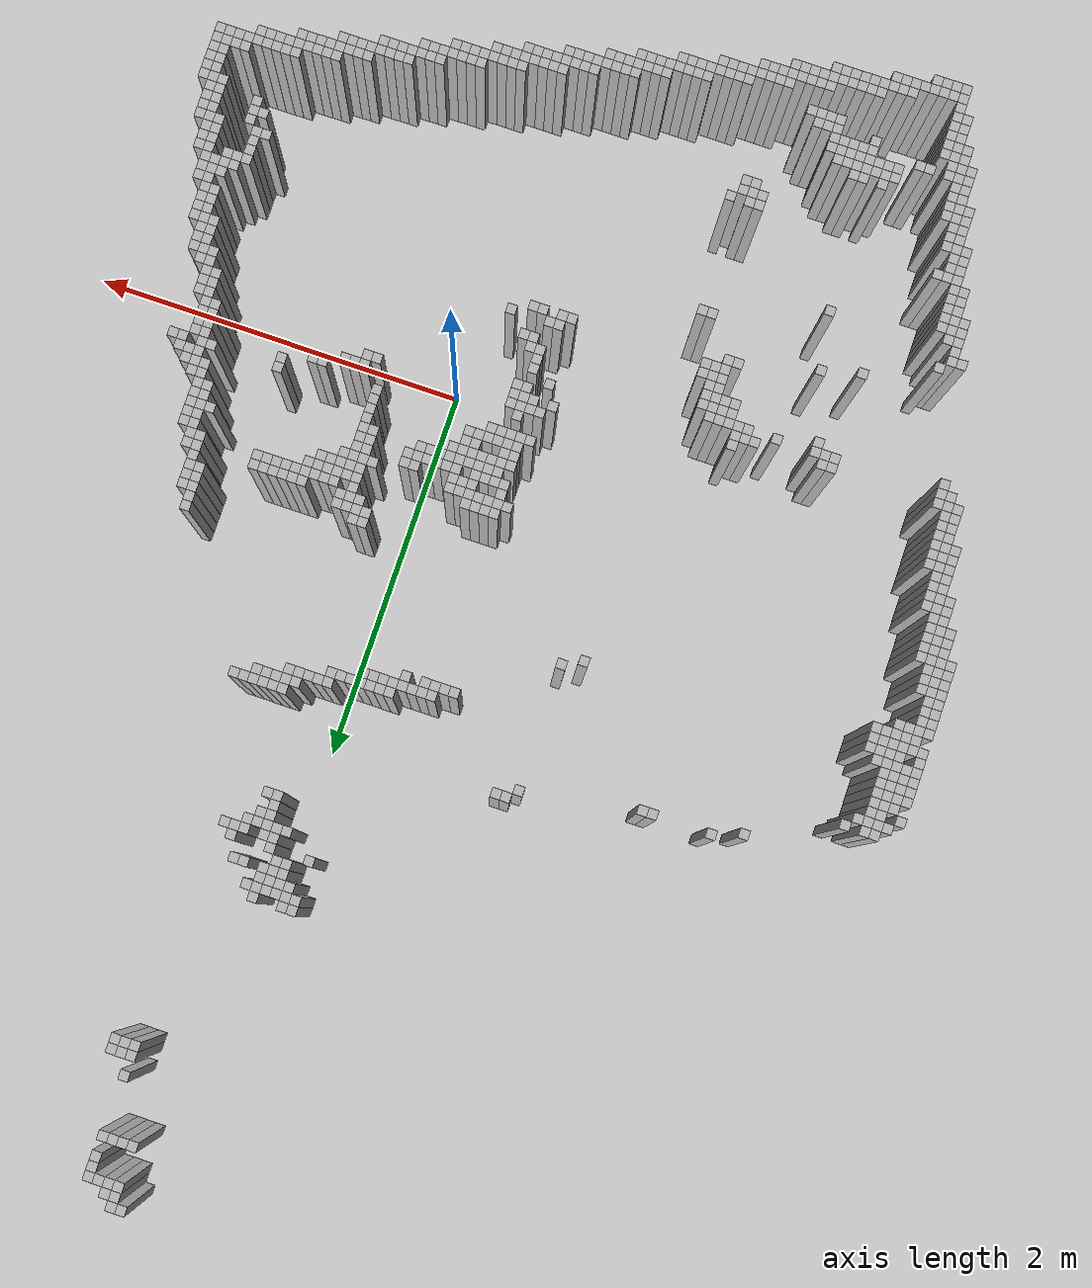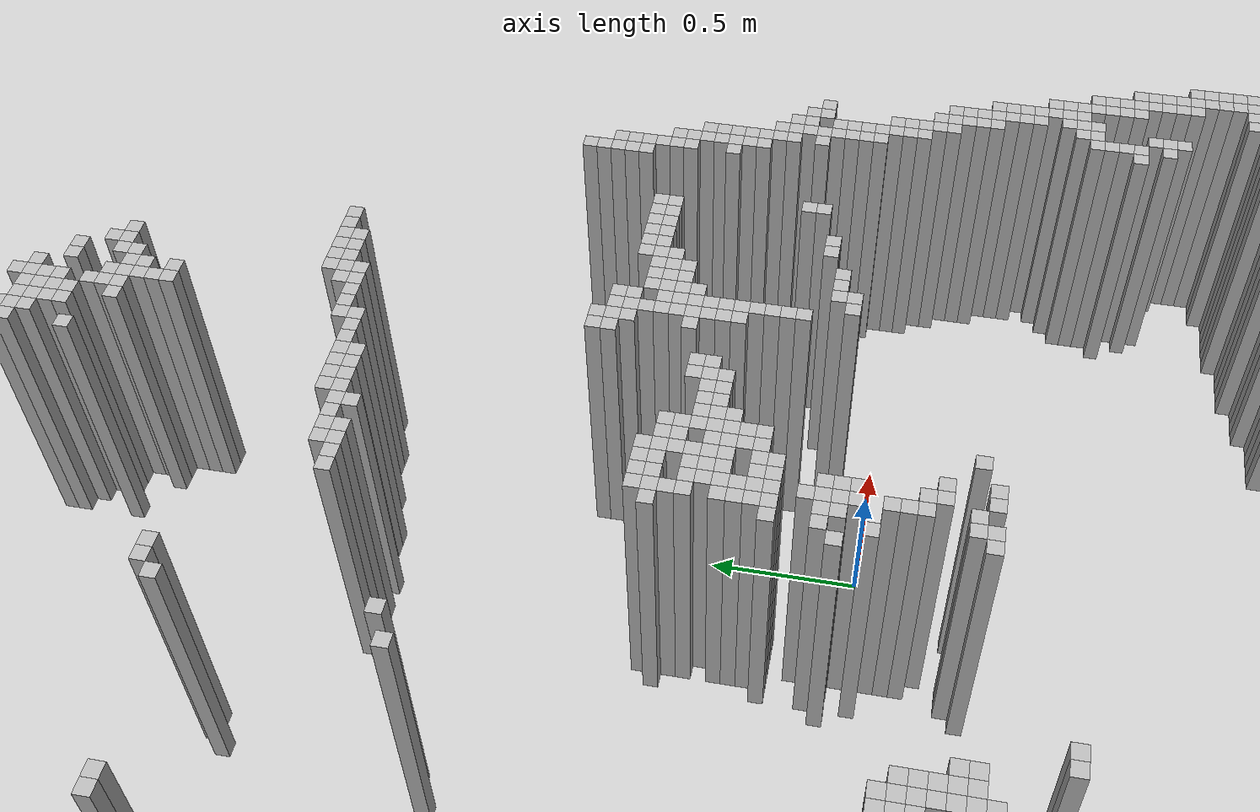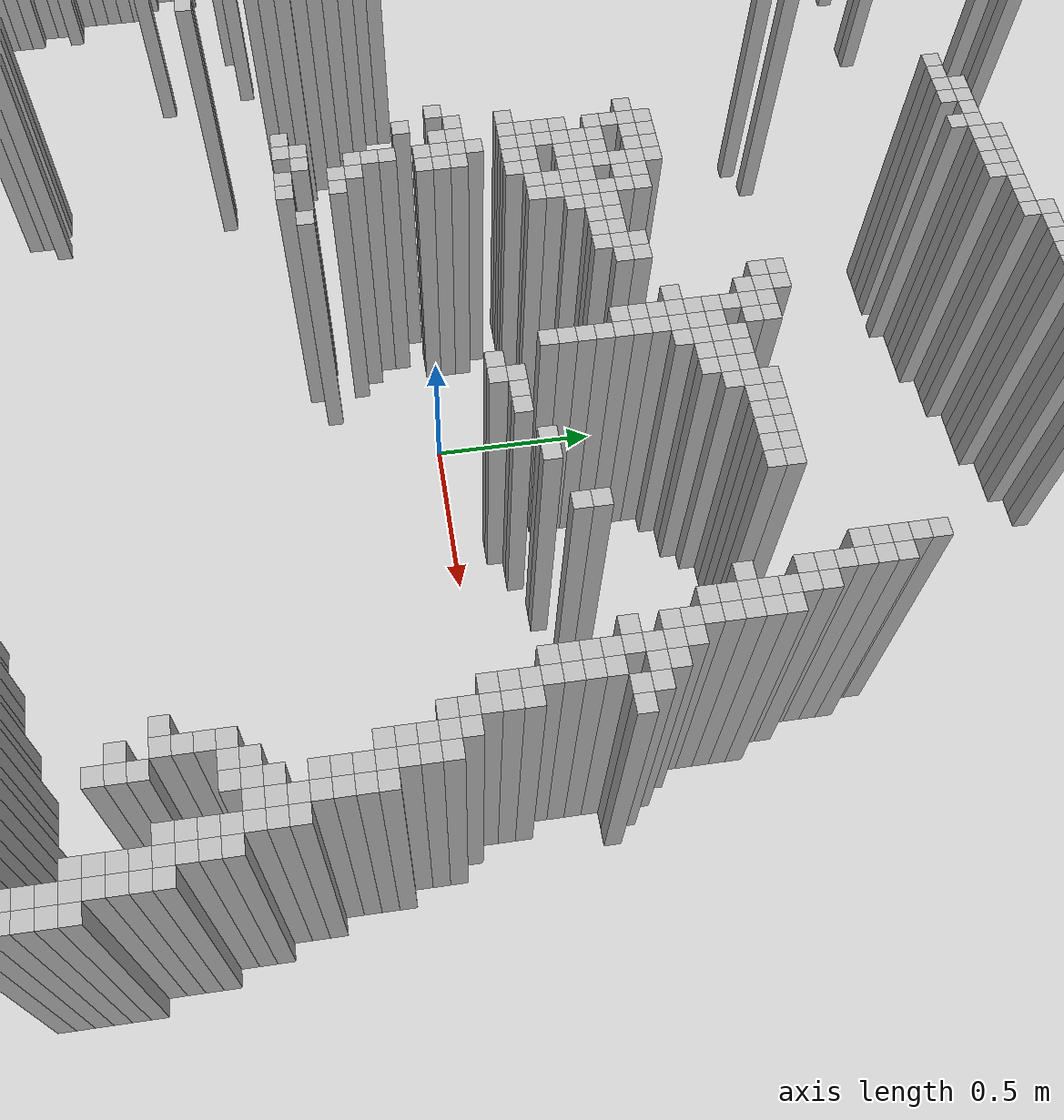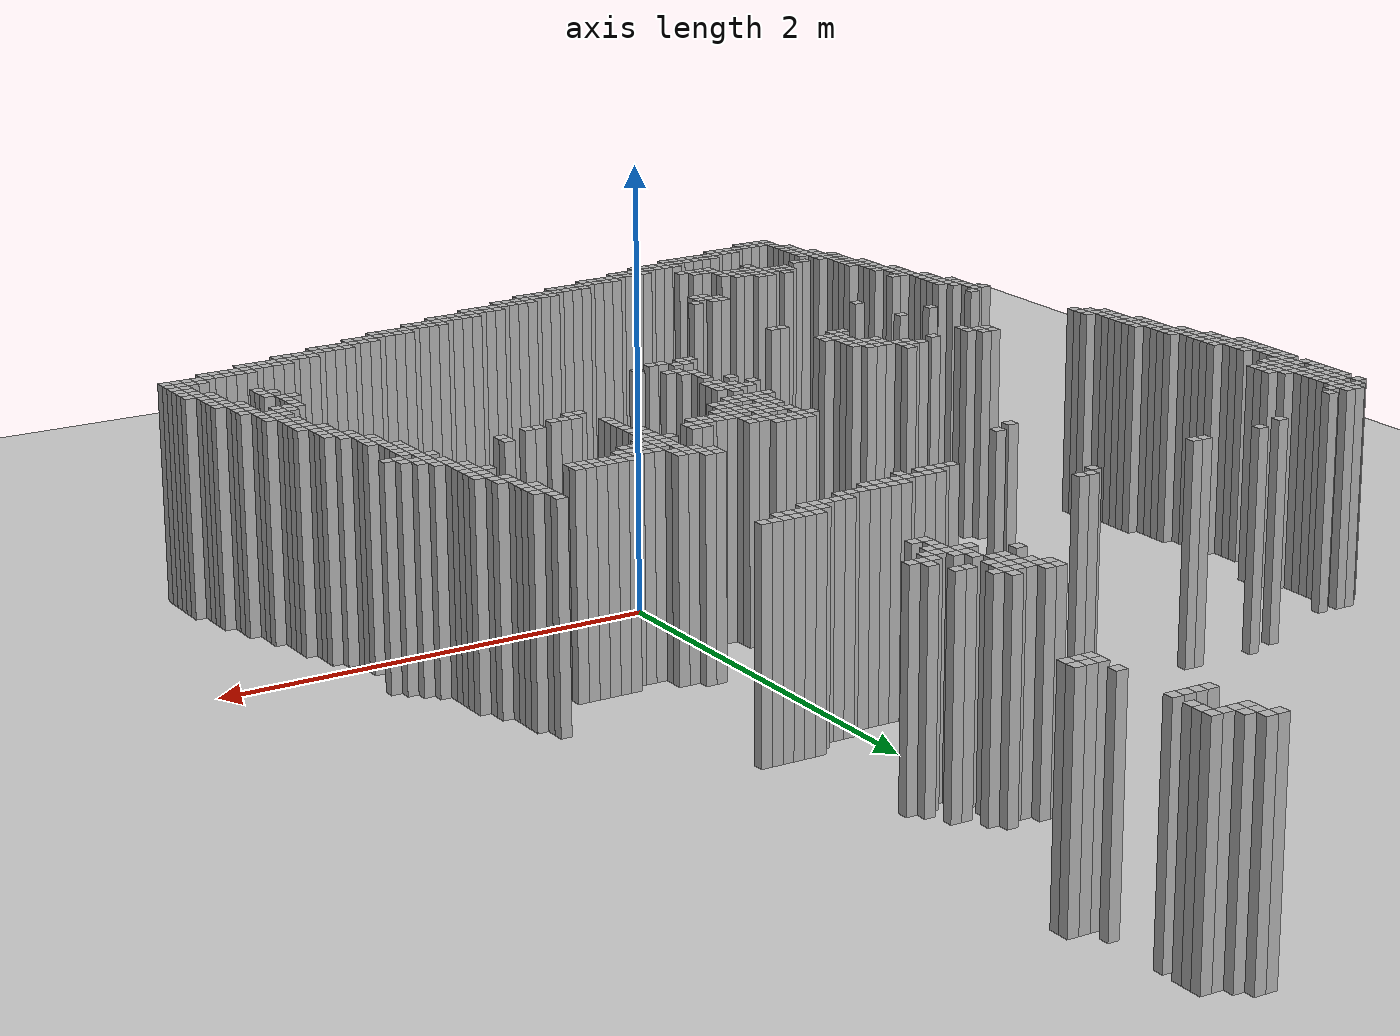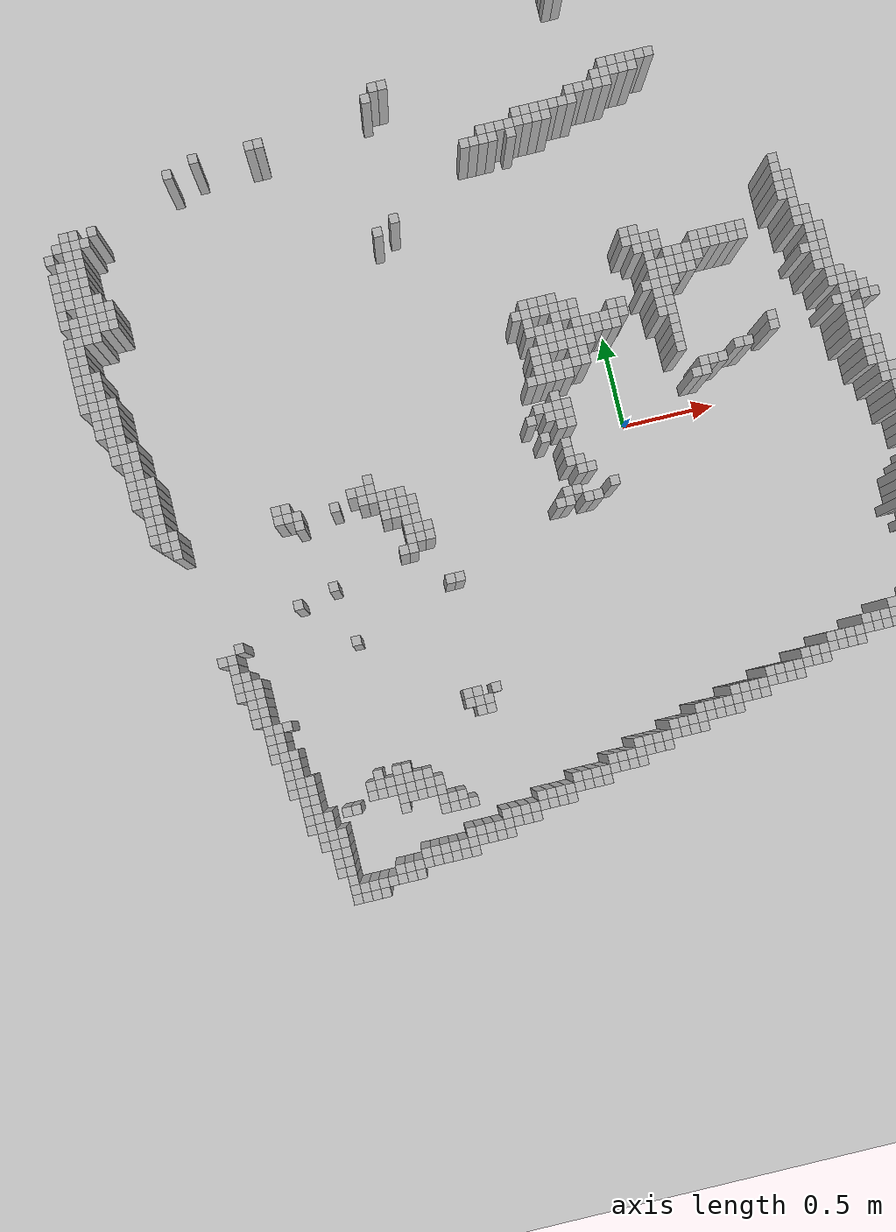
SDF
<sdf version="1.6">
  <world name="default">

    <include>
      <uri>model://ground_plane</uri>
    </include>

    <include>
      <uri>model://sun</uri>
    </include>

    <model name="wall_0">
      <static>true</static>
      <pose>0.16000000000000014 4.42 0.5 0 0 0</pose>
      <link name="link">
        <collision name="collision">
          <geometry>
            <box>
              <size>0.05 0.05 1</size>
            </box>
          </geometry>
        </collision>
        <visual name="visual">
          <geometry>
            <box>
              <size>0.05 0.05 1</size>
            </box>
          </geometry>
        </visual>
      </link>
    </model>

    <model name="wall_1">
      <static>true</static>
      <pose>0.2100000000000004 4.42 0.5 0 0 0</pose>
      <link name="link">
        <collision name="collision">
          <geometry>
            <box>
              <size>0.05 0.05 1</size>
            </box>
          </geometry>
        </collision>
        <visual name="visual">
          <geometry>
            <box>
              <size>0.05 0.05 1</size>
            </box>
          </geometry>
        </visual>
      </link>
    </model>

    <model name="wall_2">
      <static>true</static>
      <pose>0.2100000000000004 4.370000000000001 0.5 0 0 0</pose>
      <link name="link">
        <collision name="collision">
          <geometry>
            <box>
              <size>0.05 0.05 1</size>
            </box>
          </geometry>
        </collision>
        <visual name="visual">
          <geometry>
            <box>
              <size>0.05 0.05 1</size>
            </box>
          </geometry>
        </visual>
      </link>
    </model>

    <model name="wall_3">
      <static>true</static>
      <pose>0.26000000000000023 4.370000000000001 0.5 0 0 0</pose>
      <link name="link">
        <collision name="collision">
          <geometry>
            <box>
              <size>0.05 0.05 1</size>
            </box>
          </geometry>
        </collision>
        <visual name="visual">
          <geometry>
            <box>
              <size>0.05 0.05 1</size>
            </box>
          </geometry>
        </visual>
      </link>
    </model>

    <model name="wall_4">
      <static>true</static>
      <pose>0.2100000000000004 4.32 0.5 0 0 0</pose>
      <link name="link">
        <collision name="collision">
          <geometry>
            <box>
              <size>0.05 0.05 1</size>
            </box>
          </geometry>
        </collision>
        <visual name="visual">
          <geometry>
            <box>
              <size>0.05 0.05 1</size>
            </box>
          </geometry>
        </visual>
      </link>
    </model>

    <model name="wall_5">
      <static>true</static>
      <pose>0.26000000000000023 4.32 0.5 0 0 0</pose>
      <link name="link">
        <collision name="collision">
          <geometry>
            <box>
              <size>0.05 0.05 1</size>
            </box>
          </geometry>
        </collision>
        <visual name="visual">
          <geometry>
            <box>
              <size>0.05 0.05 1</size>
            </box>
          </geometry>
        </visual>
      </link>
    </model>

    <model name="wall_6">
      <static>true</static>
      <pose>0.3100000000000005 4.32 0.5 0 0 0</pose>
      <link name="link">
        <collision name="collision">
          <geometry>
            <box>
              <size>0.05 0.05 1</size>
            </box>
          </geometry>
        </collision>
        <visual name="visual">
          <geometry>
            <box>
              <size>0.05 0.05 1</size>
            </box>
          </geometry>
        </visual>
      </link>
    </model>

    <model name="wall_7">
      <static>true</static>
      <pose>0.3600000000000003 4.32 0.5 0 0 0</pose>
      <link name="link">
        <collision name="collision">
          <geometry>
            <box>
              <size>0.05 0.05 1</size>
            </box>
          </geometry>
        </collision>
        <visual name="visual">
          <geometry>
            <box>
              <size>0.05 0.05 1</size>
            </box>
          </geometry>
        </visual>
      </link>
    </model>

    <model name="wall_8">
      <static>true</static>
      <pose>0.3600000000000003 4.27 0.5 0 0 0</pose>
      <link name="link">
        <collision name="collision">
          <geometry>
            <box>
              <size>0.05 0.05 1</size>
            </box>
          </geometry>
        </collision>
        <visual name="visual">
          <geometry>
            <box>
              <size>0.05 0.05 1</size>
            </box>
          </geometry>
        </visual>
      </link>
    </model>

    <model name="wall_9">
      <static>true</static>
      <pose>0.3600000000000003 4.220000000000001 0.5 0 0 0</pose>
      <link name="link">
        <collision name="collision">
          <geometry>
            <box>
              <size>0.05 0.05 1</size>
            </box>
          </geometry>
        </collision>
        <visual name="visual">
          <geometry>
            <box>
              <size>0.05 0.05 1</size>
            </box>
          </geometry>
        </visual>
      </link>
    </model>

    <model name="wall_10">
      <static>true</static>
      <pose>0.2100000000000004 4.120000000000001 0.5 0 0 0</pose>
      <link name="link">
        <collision name="collision">
          <geometry>
            <box>
              <size>0.05 0.05 1</size>
            </box>
          </geometry>
        </collision>
        <visual name="visual">
          <geometry>
            <box>
              <size>0.05 0.05 1</size>
            </box>
          </geometry>
        </visual>
      </link>
    </model>

    <model name="wall_11">
      <static>true</static>
      <pose>0.26000000000000023 4.120000000000001 0.5 0 0 0</pose>
      <link name="link">
        <collision name="collision">
          <geometry>
            <box>
              <size>0.05 0.05 1</size>
            </box>
          </geometry>
        </collision>
        <visual name="visual">
          <geometry>
            <box>
              <size>0.05 0.05 1</size>
            </box>
          </geometry>
        </visual>
      </link>
    </model>

    <model name="wall_12">
      <static>true</static>
      <pose>0.3100000000000005 4.120000000000001 0.5 0 0 0</pose>
      <link name="link">
        <collision name="collision">
          <geometry>
            <box>
              <size>0.05 0.05 1</size>
            </box>
          </geometry>
        </collision>
        <visual name="visual">
          <geometry>
            <box>
              <size>0.05 0.05 1</size>
            </box>
          </geometry>
        </visual>
      </link>
    </model>

    <model name="wall_13">
      <static>true</static>
      <pose>0.3600000000000003 4.120000000000001 0.5 0 0 0</pose>
      <link name="link">
        <collision name="collision">
          <geometry>
            <box>
              <size>0.05 0.05 1</size>
            </box>
          </geometry>
        </collision>
        <visual name="visual">
          <geometry>
            <box>
              <size>0.05 0.05 1</size>
            </box>
          </geometry>
        </visual>
      </link>
    </model>

    <model name="wall_14">
      <static>true</static>
      <pose>0.3600000000000003 3.82 0.5 0 0 0</pose>
      <link name="link">
        <collision name="collision">
          <geometry>
            <box>
              <size>0.05 0.05 1</size>
            </box>
          </geometry>
        </collision>
        <visual name="visual">
          <geometry>
            <box>
              <size>0.05 0.05 1</size>
            </box>
          </geometry>
        </visual>
      </link>
    </model>

    <model name="wall_15">
      <static>true</static>
      <pose>0.3600000000000003 3.72 0.5 0 0 0</pose>
      <link name="link">
        <collision name="collision">
          <geometry>
            <box>
              <size>0.05 0.05 1</size>
            </box>
          </geometry>
        </collision>
        <visual name="visual">
          <geometry>
            <box>
              <size>0.05 0.05 1</size>
            </box>
          </geometry>
        </visual>
      </link>
    </model>

    <model name="wall_16">
      <static>true</static>
      <pose>0.41000000000000014 3.72 0.5 0 0 0</pose>
      <link name="link">
        <collision name="collision">
          <geometry>
            <box>
              <size>0.05 0.05 1</size>
            </box>
          </geometry>
        </collision>
        <visual name="visual">
          <geometry>
            <box>
              <size>0.05 0.05 1</size>
            </box>
          </geometry>
        </visual>
      </link>
    </model>

    <model name="wall_17">
      <static>true</static>
      <pose>0.4600000000000004 3.72 0.5 0 0 0</pose>
      <link name="link">
        <collision name="collision">
          <geometry>
            <box>
              <size>0.05 0.05 1</size>
            </box>
          </geometry>
        </collision>
        <visual name="visual">
          <geometry>
            <box>
              <size>0.05 0.05 1</size>
            </box>
          </geometry>
        </visual>
      </link>
    </model>

    <model name="wall_18">
      <static>true</static>
      <pose>0.3600000000000003 3.6700000000000004 0.5 0 0 0</pose>
      <link name="link">
        <collision name="collision">
          <geometry>
            <box>
              <size>0.05 0.05 1</size>
            </box>
          </geometry>
        </collision>
        <visual name="visual">
          <geometry>
            <box>
              <size>0.05 0.05 1</size>
            </box>
          </geometry>
        </visual>
      </link>
    </model>

    <model name="wall_19">
      <static>true</static>
      <pose>0.41000000000000014 3.6700000000000004 0.5 0 0 0</pose>
      <link name="link">
        <collision name="collision">
          <geometry>
            <box>
              <size>0.05 0.05 1</size>
            </box>
          </geometry>
        </collision>
        <visual name="visual">
          <geometry>
            <box>
              <size>0.05 0.05 1</size>
            </box>
          </geometry>
        </visual>
      </link>
    </model>

    <model name="wall_20">
      <static>true</static>
      <pose>0.4600000000000004 3.6700000000000004 0.5 0 0 0</pose>
      <link name="link">
        <collision name="collision">
          <geometry>
            <box>
              <size>0.05 0.05 1</size>
            </box>
          </geometry>
        </collision>
        <visual name="visual">
          <geometry>
            <box>
              <size>0.05 0.05 1</size>
            </box>
          </geometry>
        </visual>
      </link>
    </model>

    <model name="wall_21">
      <static>true</static>
      <pose>-0.13999999999999968 2.82 0.5 0 0 0</pose>
      <link name="link">
        <collision name="collision">
          <geometry>
            <box>
              <size>0.05 0.05 1</size>
            </box>
          </geometry>
        </collision>
        <visual name="visual">
          <geometry>
            <box>
              <size>0.05 0.05 1</size>
            </box>
          </geometry>
        </visual>
      </link>
    </model>

    <model name="wall_22">
      <static>true</static>
      <pose>-0.08999999999999986 2.82 0.5 0 0 0</pose>
      <link name="link">
        <collision name="collision">
          <geometry>
            <box>
              <size>0.05 0.05 1</size>
            </box>
          </geometry>
        </collision>
        <visual name="visual">
          <geometry>
            <box>
              <size>0.05 0.05 1</size>
            </box>
          </geometry>
        </visual>
      </link>
    </model>

    <model name="wall_23">
      <static>true</static>
      <pose>0.0600000000000005 2.82 0.5 0 0 0</pose>
      <link name="link">
        <collision name="collision">
          <geometry>
            <box>
              <size>0.05 0.05 1</size>
            </box>
          </geometry>
        </collision>
        <visual name="visual">
          <geometry>
            <box>
              <size>0.05 0.05 1</size>
            </box>
          </geometry>
        </visual>
      </link>
    </model>

    <model name="wall_24">
      <static>true</static>
      <pose>-0.13999999999999968 2.77 0.5 0 0 0</pose>
      <link name="link">
        <collision name="collision">
          <geometry>
            <box>
              <size>0.05 0.05 1</size>
            </box>
          </geometry>
        </collision>
        <visual name="visual">
          <geometry>
            <box>
              <size>0.05 0.05 1</size>
            </box>
          </geometry>
        </visual>
      </link>
    </model>

    <model name="wall_25">
      <static>true</static>
      <pose>-0.08999999999999986 2.77 0.5 0 0 0</pose>
      <link name="link">
        <collision name="collision">
          <geometry>
            <box>
              <size>0.05 0.05 1</size>
            </box>
          </geometry>
        </collision>
        <visual name="visual">
          <geometry>
            <box>
              <size>0.05 0.05 1</size>
            </box>
          </geometry>
        </visual>
      </link>
    </model>

    <model name="wall_26">
      <static>true</static>
      <pose>-0.03999999999999959 2.77 0.5 0 0 0</pose>
      <link name="link">
        <collision name="collision">
          <geometry>
            <box>
              <size>0.05 0.05 1</size>
            </box>
          </geometry>
        </collision>
        <visual name="visual">
          <geometry>
            <box>
              <size>0.05 0.05 1</size>
            </box>
          </geometry>
        </visual>
      </link>
    </model>

    <model name="wall_27">
      <static>true</static>
      <pose>0.010000000000000231 2.77 0.5 0 0 0</pose>
      <link name="link">
        <collision name="collision">
          <geometry>
            <box>
              <size>0.05 0.05 1</size>
            </box>
          </geometry>
        </collision>
        <visual name="visual">
          <geometry>
            <box>
              <size>0.05 0.05 1</size>
            </box>
          </geometry>
        </visual>
      </link>
    </model>

    <model name="wall_28">
      <static>true</static>
      <pose>0.0600000000000005 2.77 0.5 0 0 0</pose>
      <link name="link">
        <collision name="collision">
          <geometry>
            <box>
              <size>0.05 0.05 1</size>
            </box>
          </geometry>
        </collision>
        <visual name="visual">
          <geometry>
            <box>
              <size>0.05 0.05 1</size>
            </box>
          </geometry>
        </visual>
      </link>
    </model>

    <model name="wall_29">
      <static>true</static>
      <pose>0.11000000000000032 2.77 0.5 0 0 0</pose>
      <link name="link">
        <collision name="collision">
          <geometry>
            <box>
              <size>0.05 0.05 1</size>
            </box>
          </geometry>
        </collision>
        <visual name="visual">
          <geometry>
            <box>
              <size>0.05 0.05 1</size>
            </box>
          </geometry>
        </visual>
      </link>
    </model>

    <model name="wall_30">
      <static>true</static>
      <pose>-0.08999999999999986 2.72 0.5 0 0 0</pose>
      <link name="link">
        <collision name="collision">
          <geometry>
            <box>
              <size>0.05 0.05 1</size>
            </box>
          </geometry>
        </collision>
        <visual name="visual">
          <geometry>
            <box>
              <size>0.05 0.05 1</size>
            </box>
          </geometry>
        </visual>
      </link>
    </model>

    <model name="wall_31">
      <static>true</static>
      <pose>-0.03999999999999959 2.72 0.5 0 0 0</pose>
      <link name="link">
        <collision name="collision">
          <geometry>
            <box>
              <size>0.05 0.05 1</size>
            </box>
          </geometry>
        </collision>
        <visual name="visual">
          <geometry>
            <box>
              <size>0.05 0.05 1</size>
            </box>
          </geometry>
        </visual>
      </link>
    </model>

    <model name="wall_32">
      <static>true</static>
      <pose>0.010000000000000231 2.72 0.5 0 0 0</pose>
      <link name="link">
        <collision name="collision">
          <geometry>
            <box>
              <size>0.05 0.05 1</size>
            </box>
          </geometry>
        </collision>
        <visual name="visual">
          <geometry>
            <box>
              <size>0.05 0.05 1</size>
            </box>
          </geometry>
        </visual>
      </link>
    </model>

    <model name="wall_33">
      <static>true</static>
      <pose>0.0600000000000005 2.72 0.5 0 0 0</pose>
      <link name="link">
        <collision name="collision">
          <geometry>
            <box>
              <size>0.05 0.05 1</size>
            </box>
          </geometry>
        </collision>
        <visual name="visual">
          <geometry>
            <box>
              <size>0.05 0.05 1</size>
            </box>
          </geometry>
        </visual>
      </link>
    </model>

    <model name="wall_34">
      <static>true</static>
      <pose>-0.03999999999999959 2.6700000000000004 0.5 0 0 0</pose>
      <link name="link">
        <collision name="collision">
          <geometry>
            <box>
              <size>0.05 0.05 1</size>
            </box>
          </geometry>
        </collision>
        <visual name="visual">
          <geometry>
            <box>
              <size>0.05 0.05 1</size>
            </box>
          </geometry>
        </visual>
      </link>
    </model>

    <model name="wall_35">
      <static>true</static>
      <pose>0.010000000000000231 2.6700000000000004 0.5 0 0 0</pose>
      <link name="link">
        <collision name="collision">
          <geometry>
            <box>
              <size>0.05 0.05 1</size>
            </box>
          </geometry>
        </collision>
        <visual name="visual">
          <geometry>
            <box>
              <size>0.05 0.05 1</size>
            </box>
          </geometry>
        </visual>
      </link>
    </model>

    <model name="wall_36">
      <static>true</static>
      <pose>0.0600000000000005 2.6700000000000004 0.5 0 0 0</pose>
      <link name="link">
        <collision name="collision">
          <geometry>
            <box>
              <size>0.05 0.05 1</size>
            </box>
          </geometry>
        </collision>
        <visual name="visual">
          <geometry>
            <box>
              <size>0.05 0.05 1</size>
            </box>
          </geometry>
        </visual>
      </link>
    </model>

    <model name="wall_37">
      <static>true</static>
      <pose>0.16000000000000014 2.6700000000000004 0.5 0 0 0</pose>
      <link name="link">
        <collision name="collision">
          <geometry>
            <box>
              <size>0.05 0.05 1</size>
            </box>
          </geometry>
        </collision>
        <visual name="visual">
          <geometry>
            <box>
              <size>0.05 0.05 1</size>
            </box>
          </geometry>
        </visual>
      </link>
    </model>

    <model name="wall_38">
      <static>true</static>
      <pose>0.2100000000000004 2.6700000000000004 0.5 0 0 0</pose>
      <link name="link">
        <collision name="collision">
          <geometry>
            <box>
              <size>0.05 0.05 1</size>
            </box>
          </geometry>
        </collision>
        <visual name="visual">
          <geometry>
            <box>
              <size>0.05 0.05 1</size>
            </box>
          </geometry>
        </visual>
      </link>
    </model>

    <model name="wall_39">
      <static>true</static>
      <pose>-0.03999999999999959 2.6200000000000006 0.5 0 0 0</pose>
      <link name="link">
        <collision name="collision">
          <geometry>
            <box>
              <size>0.05 0.05 1</size>
            </box>
          </geometry>
        </collision>
        <visual name="visual">
          <geometry>
            <box>
              <size>0.05 0.05 1</size>
            </box>
          </geometry>
        </visual>
      </link>
    </model>

    <model name="wall_40">
      <static>true</static>
      <pose>0.010000000000000231 2.6200000000000006 0.5 0 0 0</pose>
      <link name="link">
        <collision name="collision">
          <geometry>
            <box>
              <size>0.05 0.05 1</size>
            </box>
          </geometry>
        </collision>
        <visual name="visual">
          <geometry>
            <box>
              <size>0.05 0.05 1</size>
            </box>
          </geometry>
        </visual>
      </link>
    </model>

    <model name="wall_41">
      <static>true</static>
      <pose>-0.13999999999999968 2.57 0.5 0 0 0</pose>
      <link name="link">
        <collision name="collision">
          <geometry>
            <box>
              <size>0.05 0.05 1</size>
            </box>
          </geometry>
        </collision>
        <visual name="visual">
          <geometry>
            <box>
              <size>0.05 0.05 1</size>
            </box>
          </geometry>
        </visual>
      </link>
    </model>

    <model name="wall_42">
      <static>true</static>
      <pose>0.0600000000000005 2.57 0.5 0 0 0</pose>
      <link name="link">
        <collision name="collision">
          <geometry>
            <box>
              <size>0.05 0.05 1</size>
            </box>
          </geometry>
        </collision>
        <visual name="visual">
          <geometry>
            <box>
              <size>0.05 0.05 1</size>
            </box>
          </geometry>
        </visual>
      </link>
    </model>

    <model name="wall_43">
      <static>true</static>
      <pose>0.26000000000000023 2.57 0.5 0 0 0</pose>
      <link name="link">
        <collision name="collision">
          <geometry>
            <box>
              <size>0.05 0.05 1</size>
            </box>
          </geometry>
        </collision>
        <visual name="visual">
          <geometry>
            <box>
              <size>0.05 0.05 1</size>
            </box>
          </geometry>
        </visual>
      </link>
    </model>

    <model name="wall_44">
      <static>true</static>
      <pose>0.0600000000000005 2.52 0.5 0 0 0</pose>
      <link name="link">
        <collision name="collision">
          <geometry>
            <box>
              <size>0.05 0.05 1</size>
            </box>
          </geometry>
        </collision>
        <visual name="visual">
          <geometry>
            <box>
              <size>0.05 0.05 1</size>
            </box>
          </geometry>
        </visual>
      </link>
    </model>

    <model name="wall_45">
      <static>true</static>
      <pose>0.11000000000000032 2.52 0.5 0 0 0</pose>
      <link name="link">
        <collision name="collision">
          <geometry>
            <box>
              <size>0.05 0.05 1</size>
            </box>
          </geometry>
        </collision>
        <visual name="visual">
          <geometry>
            <box>
              <size>0.05 0.05 1</size>
            </box>
          </geometry>
        </visual>
      </link>
    </model>

    <model name="wall_46">
      <static>true</static>
      <pose>0.2100000000000004 2.52 0.5 0 0 0</pose>
      <link name="link">
        <collision name="collision">
          <geometry>
            <box>
              <size>0.05 0.05 1</size>
            </box>
          </geometry>
        </collision>
        <visual name="visual">
          <geometry>
            <box>
              <size>0.05 0.05 1</size>
            </box>
          </geometry>
        </visual>
      </link>
    </model>

    <model name="wall_47">
      <static>true</static>
      <pose>0.26000000000000023 2.52 0.5 0 0 0</pose>
      <link name="link">
        <collision name="collision">
          <geometry>
            <box>
              <size>0.05 0.05 1</size>
            </box>
          </geometry>
        </collision>
        <visual name="visual">
          <geometry>
            <box>
              <size>0.05 0.05 1</size>
            </box>
          </geometry>
        </visual>
      </link>
    </model>

    <model name="wall_48">
      <static>true</static>
      <pose>0.3100000000000005 2.52 0.5 0 0 0</pose>
      <link name="link">
        <collision name="collision">
          <geometry>
            <box>
              <size>0.05 0.05 1</size>
            </box>
          </geometry>
        </collision>
        <visual name="visual">
          <geometry>
            <box>
              <size>0.05 0.05 1</size>
            </box>
          </geometry>
        </visual>
      </link>
    </model>

    <model name="wall_49">
      <static>true</static>
      <pose>0.010000000000000231 2.47 0.5 0 0 0</pose>
      <link name="link">
        <collision name="collision">
          <geometry>
            <box>
              <size>0.05 0.05 1</size>
            </box>
          </geometry>
        </collision>
        <visual name="visual">
          <geometry>
            <box>
              <size>0.05 0.05 1</size>
            </box>
          </geometry>
        </visual>
      </link>
    </model>

    <model name="wall_50">
      <static>true</static>
      <pose>0.0600000000000005 2.47 0.5 0 0 0</pose>
      <link name="link">
        <collision name="collision">
          <geometry>
            <box>
              <size>0.05 0.05 1</size>
            </box>
          </geometry>
        </collision>
        <visual name="visual">
          <geometry>
            <box>
              <size>0.05 0.05 1</size>
            </box>
          </geometry>
        </visual>
      </link>
    </model>

    <model name="wall_51">
      <static>true</static>
      <pose>0.11000000000000032 2.47 0.5 0 0 0</pose>
      <link name="link">
        <collision name="collision">
          <geometry>
            <box>
              <size>0.05 0.05 1</size>
            </box>
          </geometry>
        </collision>
        <visual name="visual">
          <geometry>
            <box>
              <size>0.05 0.05 1</size>
            </box>
          </geometry>
        </visual>
      </link>
    </model>

    <model name="wall_52">
      <static>true</static>
      <pose>0.16000000000000014 2.47 0.5 0 0 0</pose>
      <link name="link">
        <collision name="collision">
          <geometry>
            <box>
              <size>0.05 0.05 1</size>
            </box>
          </geometry>
        </collision>
        <visual name="visual">
          <geometry>
            <box>
              <size>0.05 0.05 1</size>
            </box>
          </geometry>
        </visual>
      </link>
    </model>

    <model name="wall_53">
      <static>true</static>
      <pose>0.2100000000000004 2.47 0.5 0 0 0</pose>
      <link name="link">
        <collision name="collision">
          <geometry>
            <box>
              <size>0.05 0.05 1</size>
            </box>
          </geometry>
        </collision>
        <visual name="visual">
          <geometry>
            <box>
              <size>0.05 0.05 1</size>
            </box>
          </geometry>
        </visual>
      </link>
    </model>

    <model name="wall_54">
      <static>true</static>
      <pose>0.11000000000000032 2.4200000000000004 0.5 0 0 0</pose>
      <link name="link">
        <collision name="collision">
          <geometry>
            <box>
              <size>0.05 0.05 1</size>
            </box>
          </geometry>
        </collision>
        <visual name="visual">
          <geometry>
            <box>
              <size>0.05 0.05 1</size>
            </box>
          </geometry>
        </visual>
      </link>
    </model>

    <model name="wall_55">
      <static>true</static>
      <pose>0.16000000000000014 2.4200000000000004 0.5 0 0 0</pose>
      <link name="link">
        <collision name="collision">
          <geometry>
            <box>
              <size>0.05 0.05 1</size>
            </box>
          </geometry>
        </collision>
        <visual name="visual">
          <geometry>
            <box>
              <size>0.05 0.05 1</size>
            </box>
          </geometry>
        </visual>
      </link>
    </model>

    <model name="wall_56">
      <static>true</static>
      <pose>0.11000000000000032 2.3699999999999997 0.5 0 0 0</pose>
      <link name="link">
        <collision name="collision">
          <geometry>
            <box>
              <size>0.05 0.05 1</size>
            </box>
          </geometry>
        </collision>
        <visual name="visual">
          <geometry>
            <box>
              <size>0.05 0.05 1</size>
            </box>
          </geometry>
        </visual>
      </link>
    </model>

    <model name="wall_57">
      <static>true</static>
      <pose>0.11000000000000032 2.32 0.5 0 0 0</pose>
      <link name="link">
        <collision name="collision">
          <geometry>
            <box>
              <size>0.05 0.05 1</size>
            </box>
          </geometry>
        </collision>
        <visual name="visual">
          <geometry>
            <box>
              <size>0.05 0.05 1</size>
            </box>
          </geometry>
        </visual>
      </link>
    </model>

    <model name="wall_58">
      <static>true</static>
      <pose>0.16000000000000014 2.32 0.5 0 0 0</pose>
      <link name="link">
        <collision name="collision">
          <geometry>
            <box>
              <size>0.05 0.05 1</size>
            </box>
          </geometry>
        </collision>
        <visual name="visual">
          <geometry>
            <box>
              <size>0.05 0.05 1</size>
            </box>
          </geometry>
        </visual>
      </link>
    </model>

    <model name="wall_59">
      <static>true</static>
      <pose>-0.9399999999999997 1.9700000000000002 0.5 0 0 0</pose>
      <link name="link">
        <collision name="collision">
          <geometry>
            <box>
              <size>0.05 0.05 1</size>
            </box>
          </geometry>
        </collision>
        <visual name="visual">
          <geometry>
            <box>
              <size>0.05 0.05 1</size>
            </box>
          </geometry>
        </visual>
      </link>
    </model>

    <model name="wall_60">
      <static>true</static>
      <pose>-0.8899999999999997 1.9700000000000002 0.5 0 0 0</pose>
      <link name="link">
        <collision name="collision">
          <geometry>
            <box>
              <size>0.05 0.05 1</size>
            </box>
          </geometry>
        </collision>
        <visual name="visual">
          <geometry>
            <box>
              <size>0.05 0.05 1</size>
            </box>
          </geometry>
        </visual>
      </link>
    </model>

    <model name="wall_61">
      <static>true</static>
      <pose>-0.9899999999999998 1.9200000000000004 0.5 0 0 0</pose>
      <link name="link">
        <collision name="collision">
          <geometry>
            <box>
              <size>0.05 0.05 1</size>
            </box>
          </geometry>
        </collision>
        <visual name="visual">
          <geometry>
            <box>
              <size>0.05 0.05 1</size>
            </box>
          </geometry>
        </visual>
      </link>
    </model>

    <model name="wall_62">
      <static>true</static>
      <pose>-1.94 1.8199999999999998 0.5 0 0 0</pose>
      <link name="link">
        <collision name="collision">
          <geometry>
            <box>
              <size>0.05 0.05 1</size>
            </box>
          </geometry>
        </collision>
        <visual name="visual">
          <geometry>
            <box>
              <size>0.05 0.05 1</size>
            </box>
          </geometry>
        </visual>
      </link>
    </model>

    <model name="wall_63">
      <static>true</static>
      <pose>-1.6399999999999997 1.8199999999999998 0.5 0 0 0</pose>
      <link name="link">
        <collision name="collision">
          <geometry>
            <box>
              <size>0.05 0.05 1</size>
            </box>
          </geometry>
        </collision>
        <visual name="visual">
          <geometry>
            <box>
              <size>0.05 0.05 1</size>
            </box>
          </geometry>
        </visual>
      </link>
    </model>

    <model name="wall_64">
      <static>true</static>
      <pose>-1.5899999999999999 1.8199999999999998 0.5 0 0 0</pose>
      <link name="link">
        <collision name="collision">
          <geometry>
            <box>
              <size>0.05 0.05 1</size>
            </box>
          </geometry>
        </collision>
        <visual name="visual">
          <geometry>
            <box>
              <size>0.05 0.05 1</size>
            </box>
          </geometry>
        </visual>
      </link>
    </model>

    <model name="wall_65">
      <static>true</static>
      <pose>0.26000000000000023 1.8199999999999998 0.5 0 0 0</pose>
      <link name="link">
        <collision name="collision">
          <geometry>
            <box>
              <size>0.05 0.05 1</size>
            </box>
          </geometry>
        </collision>
        <visual name="visual">
          <geometry>
            <box>
              <size>0.05 0.05 1</size>
            </box>
          </geometry>
        </visual>
      </link>
    </model>

    <model name="wall_66">
      <static>true</static>
      <pose>0.3100000000000005 1.8199999999999998 0.5 0 0 0</pose>
      <link name="link">
        <collision name="collision">
          <geometry>
            <box>
              <size>0.05 0.05 1</size>
            </box>
          </geometry>
        </collision>
        <visual name="visual">
          <geometry>
            <box>
              <size>0.05 0.05 1</size>
            </box>
          </geometry>
        </visual>
      </link>
    </model>

    <model name="wall_67">
      <static>true</static>
      <pose>0.3600000000000003 1.8199999999999998 0.5 0 0 0</pose>
      <link name="link">
        <collision name="collision">
          <geometry>
            <box>
              <size>0.05 0.05 1</size>
            </box>
          </geometry>
        </collision>
        <visual name="visual">
          <geometry>
            <box>
              <size>0.05 0.05 1</size>
            </box>
          </geometry>
        </visual>
      </link>
    </model>

    <model name="wall_68">
      <static>true</static>
      <pose>0.41000000000000014 1.8199999999999998 0.5 0 0 0</pose>
      <link name="link">
        <collision name="collision">
          <geometry>
            <box>
              <size>0.05 0.05 1</size>
            </box>
          </geometry>
        </collision>
        <visual name="visual">
          <geometry>
            <box>
              <size>0.05 0.05 1</size>
            </box>
          </geometry>
        </visual>
      </link>
    </model>

    <model name="wall_69">
      <static>true</static>
      <pose>0.4600000000000004 1.8199999999999998 0.5 0 0 0</pose>
      <link name="link">
        <collision name="collision">
          <geometry>
            <box>
              <size>0.05 0.05 1</size>
            </box>
          </geometry>
        </collision>
        <visual name="visual">
          <geometry>
            <box>
              <size>0.05 0.05 1</size>
            </box>
          </geometry>
        </visual>
      </link>
    </model>

    <model name="wall_70">
      <static>true</static>
      <pose>0.5100000000000002 1.8199999999999998 0.5 0 0 0</pose>
      <link name="link">
        <collision name="collision">
          <geometry>
            <box>
              <size>0.05 0.05 1</size>
            </box>
          </geometry>
        </collision>
        <visual name="visual">
          <geometry>
            <box>
              <size>0.05 0.05 1</size>
            </box>
          </geometry>
        </visual>
      </link>
    </model>

    <model name="wall_71">
      <static>true</static>
      <pose>-2.09 1.77 0.5 0 0 0</pose>
      <link name="link">
        <collision name="collision">
          <geometry>
            <box>
              <size>0.05 0.05 1</size>
            </box>
          </geometry>
        </collision>
        <visual name="visual">
          <geometry>
            <box>
              <size>0.05 0.05 1</size>
            </box>
          </geometry>
        </visual>
      </link>
    </model>

    <model name="wall_72">
      <static>true</static>
      <pose>0.2100000000000004 1.77 0.5 0 0 0</pose>
      <link name="link">
        <collision name="collision">
          <geometry>
            <box>
              <size>0.05 0.05 1</size>
            </box>
          </geometry>
        </collision>
        <visual name="visual">
          <geometry>
            <box>
              <size>0.05 0.05 1</size>
            </box>
          </geometry>
        </visual>
      </link>
    </model>

    <model name="wall_73">
      <static>true</static>
      <pose>0.26000000000000023 1.77 0.5 0 0 0</pose>
      <link name="link">
        <collision name="collision">
          <geometry>
            <box>
              <size>0.05 0.05 1</size>
            </box>
          </geometry>
        </collision>
        <visual name="visual">
          <geometry>
            <box>
              <size>0.05 0.05 1</size>
            </box>
          </geometry>
        </visual>
      </link>
    </model>

    <model name="wall_74">
      <static>true</static>
      <pose>0.3100000000000005 1.77 0.5 0 0 0</pose>
      <link name="link">
        <collision name="collision">
          <geometry>
            <box>
              <size>0.05 0.05 1</size>
            </box>
          </geometry>
        </collision>
        <visual name="visual">
          <geometry>
            <box>
              <size>0.05 0.05 1</size>
            </box>
          </geometry>
        </visual>
      </link>
    </model>

    <model name="wall_75">
      <static>true</static>
      <pose>0.3600000000000003 1.77 0.5 0 0 0</pose>
      <link name="link">
        <collision name="collision">
          <geometry>
            <box>
              <size>0.05 0.05 1</size>
            </box>
          </geometry>
        </collision>
        <visual name="visual">
          <geometry>
            <box>
              <size>0.05 0.05 1</size>
            </box>
          </geometry>
        </visual>
      </link>
    </model>

    <model name="wall_76">
      <static>true</static>
      <pose>0.41000000000000014 1.77 0.5 0 0 0</pose>
      <link name="link">
        <collision name="collision">
          <geometry>
            <box>
              <size>0.05 0.05 1</size>
            </box>
          </geometry>
        </collision>
        <visual name="visual">
          <geometry>
            <box>
              <size>0.05 0.05 1</size>
            </box>
          </geometry>
        </visual>
      </link>
    </model>

    <model name="wall_77">
      <static>true</static>
      <pose>0.0600000000000005 1.7200000000000002 0.5 0 0 0</pose>
      <link name="link">
        <collision name="collision">
          <geometry>
            <box>
              <size>0.05 0.05 1</size>
            </box>
          </geometry>
        </collision>
        <visual name="visual">
          <geometry>
            <box>
              <size>0.05 0.05 1</size>
            </box>
          </geometry>
        </visual>
      </link>
    </model>

    <model name="wall_78">
      <static>true</static>
      <pose>0.11000000000000032 1.7200000000000002 0.5 0 0 0</pose>
      <link name="link">
        <collision name="collision">
          <geometry>
            <box>
              <size>0.05 0.05 1</size>
            </box>
          </geometry>
        </collision>
        <visual name="visual">
          <geometry>
            <box>
              <size>0.05 0.05 1</size>
            </box>
          </geometry>
        </visual>
      </link>
    </model>

    <model name="wall_79">
      <static>true</static>
      <pose>0.16000000000000014 1.7200000000000002 0.5 0 0 0</pose>
      <link name="link">
        <collision name="collision">
          <geometry>
            <box>
              <size>0.05 0.05 1</size>
            </box>
          </geometry>
        </collision>
        <visual name="visual">
          <geometry>
            <box>
              <size>0.05 0.05 1</size>
            </box>
          </geometry>
        </visual>
      </link>
    </model>

    <model name="wall_80">
      <static>true</static>
      <pose>0.2100000000000004 1.7200000000000002 0.5 0 0 0</pose>
      <link name="link">
        <collision name="collision">
          <geometry>
            <box>
              <size>0.05 0.05 1</size>
            </box>
          </geometry>
        </collision>
        <visual name="visual">
          <geometry>
            <box>
              <size>0.05 0.05 1</size>
            </box>
          </geometry>
        </visual>
      </link>
    </model>

    <model name="wall_81">
      <static>true</static>
      <pose>0.26000000000000023 1.7200000000000002 0.5 0 0 0</pose>
      <link name="link">
        <collision name="collision">
          <geometry>
            <box>
              <size>0.05 0.05 1</size>
            </box>
          </geometry>
        </collision>
        <visual name="visual">
          <geometry>
            <box>
              <size>0.05 0.05 1</size>
            </box>
          </geometry>
        </visual>
      </link>
    </model>

    <model name="wall_82">
      <static>true</static>
      <pose>-0.23999999999999977 1.67 0.5 0 0 0</pose>
      <link name="link">
        <collision name="collision">
          <geometry>
            <box>
              <size>0.05 0.05 1</size>
            </box>
          </geometry>
        </collision>
        <visual name="visual">
          <geometry>
            <box>
              <size>0.05 0.05 1</size>
            </box>
          </geometry>
        </visual>
      </link>
    </model>

    <model name="wall_83">
      <static>true</static>
      <pose>-0.1899999999999995 1.67 0.5 0 0 0</pose>
      <link name="link">
        <collision name="collision">
          <geometry>
            <box>
              <size>0.05 0.05 1</size>
            </box>
          </geometry>
        </collision>
        <visual name="visual">
          <geometry>
            <box>
              <size>0.05 0.05 1</size>
            </box>
          </geometry>
        </visual>
      </link>
    </model>

    <model name="wall_84">
      <static>true</static>
      <pose>-0.13999999999999968 1.67 0.5 0 0 0</pose>
      <link name="link">
        <collision name="collision">
          <geometry>
            <box>
              <size>0.05 0.05 1</size>
            </box>
          </geometry>
        </collision>
        <visual name="visual">
          <geometry>
            <box>
              <size>0.05 0.05 1</size>
            </box>
          </geometry>
        </visual>
      </link>
    </model>

    <model name="wall_85">
      <static>true</static>
      <pose>-0.08999999999999986 1.67 0.5 0 0 0</pose>
      <link name="link">
        <collision name="collision">
          <geometry>
            <box>
              <size>0.05 0.05 1</size>
            </box>
          </geometry>
        </collision>
        <visual name="visual">
          <geometry>
            <box>
              <size>0.05 0.05 1</size>
            </box>
          </geometry>
        </visual>
      </link>
    </model>

    <model name="wall_86">
      <static>true</static>
      <pose>-0.03999999999999959 1.67 0.5 0 0 0</pose>
      <link name="link">
        <collision name="collision">
          <geometry>
            <box>
              <size>0.05 0.05 1</size>
            </box>
          </geometry>
        </collision>
        <visual name="visual">
          <geometry>
            <box>
              <size>0.05 0.05 1</size>
            </box>
          </geometry>
        </visual>
      </link>
    </model>

    <model name="wall_87">
      <static>true</static>
      <pose>0.010000000000000231 1.67 0.5 0 0 0</pose>
      <link name="link">
        <collision name="collision">
          <geometry>
            <box>
              <size>0.05 0.05 1</size>
            </box>
          </geometry>
        </collision>
        <visual name="visual">
          <geometry>
            <box>
              <size>0.05 0.05 1</size>
            </box>
          </geometry>
        </visual>
      </link>
    </model>

    <model name="wall_88">
      <static>true</static>
      <pose>0.0600000000000005 1.67 0.5 0 0 0</pose>
      <link name="link">
        <collision name="collision">
          <geometry>
            <box>
              <size>0.05 0.05 1</size>
            </box>
          </geometry>
        </collision>
        <visual name="visual">
          <geometry>
            <box>
              <size>0.05 0.05 1</size>
            </box>
          </geometry>
        </visual>
      </link>
    </model>

    <model name="wall_89">
      <static>true</static>
      <pose>-0.4399999999999995 1.62 0.5 0 0 0</pose>
      <link name="link">
        <collision name="collision">
          <geometry>
            <box>
              <size>0.05 0.05 1</size>
            </box>
          </geometry>
        </collision>
        <visual name="visual">
          <geometry>
            <box>
              <size>0.05 0.05 1</size>
            </box>
          </geometry>
        </visual>
      </link>
    </model>

    <model name="wall_90">
      <static>true</static>
      <pose>-0.3899999999999997 1.62 0.5 0 0 0</pose>
      <link name="link">
        <collision name="collision">
          <geometry>
            <box>
              <size>0.05 0.05 1</size>
            </box>
          </geometry>
        </collision>
        <visual name="visual">
          <geometry>
            <box>
              <size>0.05 0.05 1</size>
            </box>
          </geometry>
        </visual>
      </link>
    </model>

    <model name="wall_91">
      <static>true</static>
      <pose>-0.33999999999999986 1.62 0.5 0 0 0</pose>
      <link name="link">
        <collision name="collision">
          <geometry>
            <box>
              <size>0.05 0.05 1</size>
            </box>
          </geometry>
        </collision>
        <visual name="visual">
          <geometry>
            <box>
              <size>0.05 0.05 1</size>
            </box>
          </geometry>
        </visual>
      </link>
    </model>

    <model name="wall_92">
      <static>true</static>
      <pose>-0.2899999999999996 1.62 0.5 0 0 0</pose>
      <link name="link">
        <collision name="collision">
          <geometry>
            <box>
              <size>0.05 0.05 1</size>
            </box>
          </geometry>
        </collision>
        <visual name="visual">
          <geometry>
            <box>
              <size>0.05 0.05 1</size>
            </box>
          </geometry>
        </visual>
      </link>
    </model>

    <model name="wall_93">
      <static>true</static>
      <pose>-0.23999999999999977 1.62 0.5 0 0 0</pose>
      <link name="link">
        <collision name="collision">
          <geometry>
            <box>
              <size>0.05 0.05 1</size>
            </box>
          </geometry>
        </collision>
        <visual name="visual">
          <geometry>
            <box>
              <size>0.05 0.05 1</size>
            </box>
          </geometry>
        </visual>
      </link>
    </model>

    <model name="wall_94">
      <static>true</static>
      <pose>-0.1899999999999995 1.62 0.5 0 0 0</pose>
      <link name="link">
        <collision name="collision">
          <geometry>
            <box>
              <size>0.05 0.05 1</size>
            </box>
          </geometry>
        </collision>
        <visual name="visual">
          <geometry>
            <box>
              <size>0.05 0.05 1</size>
            </box>
          </geometry>
        </visual>
      </link>
    </model>

    <model name="wall_95">
      <static>true</static>
      <pose>-0.13999999999999968 1.62 0.5 0 0 0</pose>
      <link name="link">
        <collision name="collision">
          <geometry>
            <box>
              <size>0.05 0.05 1</size>
            </box>
          </geometry>
        </collision>
        <visual name="visual">
          <geometry>
            <box>
              <size>0.05 0.05 1</size>
            </box>
          </geometry>
        </visual>
      </link>
    </model>

    <model name="wall_96">
      <static>true</static>
      <pose>-0.08999999999999986 1.62 0.5 0 0 0</pose>
      <link name="link">
        <collision name="collision">
          <geometry>
            <box>
              <size>0.05 0.05 1</size>
            </box>
          </geometry>
        </collision>
        <visual name="visual">
          <geometry>
            <box>
              <size>0.05 0.05 1</size>
            </box>
          </geometry>
        </visual>
      </link>
    </model>

    <model name="wall_97">
      <static>true</static>
      <pose>-2.69 1.5699999999999998 0.5 0 0 0</pose>
      <link name="link">
        <collision name="collision">
          <geometry>
            <box>
              <size>0.05 0.05 1</size>
            </box>
          </geometry>
        </collision>
        <visual name="visual">
          <geometry>
            <box>
              <size>0.05 0.05 1</size>
            </box>
          </geometry>
        </visual>
      </link>
    </model>

    <model name="wall_98">
      <static>true</static>
      <pose>-2.6399999999999997 1.5699999999999998 0.5 0 0 0</pose>
      <link name="link">
        <collision name="collision">
          <geometry>
            <box>
              <size>0.05 0.05 1</size>
            </box>
          </geometry>
        </collision>
        <visual name="visual">
          <geometry>
            <box>
              <size>0.05 0.05 1</size>
            </box>
          </geometry>
        </visual>
      </link>
    </model>

    <model name="wall_99">
      <static>true</static>
      <pose>-2.54 1.5699999999999998 0.5 0 0 0</pose>
      <link name="link">
        <collision name="collision">
          <geometry>
            <box>
              <size>0.05 0.05 1</size>
            </box>
          </geometry>
        </collision>
        <visual name="visual">
          <geometry>
            <box>
              <size>0.05 0.05 1</size>
            </box>
          </geometry>
        </visual>
      </link>
    </model>

    <model name="wall_100">
      <static>true</static>
      <pose>-0.5399999999999996 1.5699999999999998 0.5 0 0 0</pose>
      <link name="link">
        <collision name="collision">
          <geometry>
            <box>
              <size>0.05 0.05 1</size>
            </box>
          </geometry>
        </collision>
        <visual name="visual">
          <geometry>
            <box>
              <size>0.05 0.05 1</size>
            </box>
          </geometry>
        </visual>
      </link>
    </model>

    <model name="wall_101">
      <static>true</static>
      <pose>-0.48999999999999977 1.5699999999999998 0.5 0 0 0</pose>
      <link name="link">
        <collision name="collision">
          <geometry>
            <box>
              <size>0.05 0.05 1</size>
            </box>
          </geometry>
        </collision>
        <visual name="visual">
          <geometry>
            <box>
              <size>0.05 0.05 1</size>
            </box>
          </geometry>
        </visual>
      </link>
    </model>

    <model name="wall_102">
      <static>true</static>
      <pose>-0.4399999999999995 1.5699999999999998 0.5 0 0 0</pose>
      <link name="link">
        <collision name="collision">
          <geometry>
            <box>
              <size>0.05 0.05 1</size>
            </box>
          </geometry>
        </collision>
        <visual name="visual">
          <geometry>
            <box>
              <size>0.05 0.05 1</size>
            </box>
          </geometry>
        </visual>
      </link>
    </model>

    <model name="wall_103">
      <static>true</static>
      <pose>-0.3899999999999997 1.5699999999999998 0.5 0 0 0</pose>
      <link name="link">
        <collision name="collision">
          <geometry>
            <box>
              <size>0.05 0.05 1</size>
            </box>
          </geometry>
        </collision>
        <visual name="visual">
          <geometry>
            <box>
              <size>0.05 0.05 1</size>
            </box>
          </geometry>
        </visual>
      </link>
    </model>

    <model name="wall_104">
      <static>true</static>
      <pose>-0.2899999999999996 1.5699999999999998 0.5 0 0 0</pose>
      <link name="link">
        <collision name="collision">
          <geometry>
            <box>
              <size>0.05 0.05 1</size>
            </box>
          </geometry>
        </collision>
        <visual name="visual">
          <geometry>
            <box>
              <size>0.05 0.05 1</size>
            </box>
          </geometry>
        </visual>
      </link>
    </model>

    <model name="wall_105">
      <static>true</static>
      <pose>-2.7399999999999998 1.52 0.5 0 0 0</pose>
      <link name="link">
        <collision name="collision">
          <geometry>
            <box>
              <size>0.05 0.05 1</size>
            </box>
          </geometry>
        </collision>
        <visual name="visual">
          <geometry>
            <box>
              <size>0.05 0.05 1</size>
            </box>
          </geometry>
        </visual>
      </link>
    </model>

    <model name="wall_106">
      <static>true</static>
      <pose>-2.69 1.52 0.5 0 0 0</pose>
      <link name="link">
        <collision name="collision">
          <geometry>
            <box>
              <size>0.05 0.05 1</size>
            </box>
          </geometry>
        </collision>
        <visual name="visual">
          <geometry>
            <box>
              <size>0.05 0.05 1</size>
            </box>
          </geometry>
        </visual>
      </link>
    </model>

    <model name="wall_107">
      <static>true</static>
      <pose>-2.6399999999999997 1.52 0.5 0 0 0</pose>
      <link name="link">
        <collision name="collision">
          <geometry>
            <box>
              <size>0.05 0.05 1</size>
            </box>
          </geometry>
        </collision>
        <visual name="visual">
          <geometry>
            <box>
              <size>0.05 0.05 1</size>
            </box>
          </geometry>
        </visual>
      </link>
    </model>

    <model name="wall_108">
      <static>true</static>
      <pose>-2.59 1.52 0.5 0 0 0</pose>
      <link name="link">
        <collision name="collision">
          <geometry>
            <box>
              <size>0.05 0.05 1</size>
            </box>
          </geometry>
        </collision>
        <visual name="visual">
          <geometry>
            <box>
              <size>0.05 0.05 1</size>
            </box>
          </geometry>
        </visual>
      </link>
    </model>

    <model name="wall_109">
      <static>true</static>
      <pose>-2.79 1.4700000000000002 0.5 0 0 0</pose>
      <link name="link">
        <collision name="collision">
          <geometry>
            <box>
              <size>0.05 0.05 1</size>
            </box>
          </geometry>
        </collision>
        <visual name="visual">
          <geometry>
            <box>
              <size>0.05 0.05 1</size>
            </box>
          </geometry>
        </visual>
      </link>
    </model>

    <model name="wall_110">
      <static>true</static>
      <pose>-2.69 1.4700000000000002 0.5 0 0 0</pose>
      <link name="link">
        <collision name="collision">
          <geometry>
            <box>
              <size>0.05 0.05 1</size>
            </box>
          </geometry>
        </collision>
        <visual name="visual">
          <geometry>
            <box>
              <size>0.05 0.05 1</size>
            </box>
          </geometry>
        </visual>
      </link>
    </model>

    <model name="wall_111">
      <static>true</static>
      <pose>-2.6399999999999997 1.4700000000000002 0.5 0 0 0</pose>
      <link name="link">
        <collision name="collision">
          <geometry>
            <box>
              <size>0.05 0.05 1</size>
            </box>
          </geometry>
        </collision>
        <visual name="visual">
          <geometry>
            <box>
              <size>0.05 0.05 1</size>
            </box>
          </geometry>
        </visual>
      </link>
    </model>

    <model name="wall_112">
      <static>true</static>
      <pose>-2.7399999999999998 1.42 0.5 0 0 0</pose>
      <link name="link">
        <collision name="collision">
          <geometry>
            <box>
              <size>0.05 0.05 1</size>
            </box>
          </geometry>
        </collision>
        <visual name="visual">
          <geometry>
            <box>
              <size>0.05 0.05 1</size>
            </box>
          </geometry>
        </visual>
      </link>
    </model>

    <model name="wall_113">
      <static>true</static>
      <pose>-2.69 1.42 0.5 0 0 0</pose>
      <link name="link">
        <collision name="collision">
          <geometry>
            <box>
              <size>0.05 0.05 1</size>
            </box>
          </geometry>
        </collision>
        <visual name="visual">
          <geometry>
            <box>
              <size>0.05 0.05 1</size>
            </box>
          </geometry>
        </visual>
      </link>
    </model>

    <model name="wall_114">
      <static>true</static>
      <pose>-2.6399999999999997 1.42 0.5 0 0 0</pose>
      <link name="link">
        <collision name="collision">
          <geometry>
            <box>
              <size>0.05 0.05 1</size>
            </box>
          </geometry>
        </collision>
        <visual name="visual">
          <geometry>
            <box>
              <size>0.05 0.05 1</size>
            </box>
          </geometry>
        </visual>
      </link>
    </model>

    <model name="wall_115">
      <static>true</static>
      <pose>-2.79 1.37 0.5 0 0 0</pose>
      <link name="link">
        <collision name="collision">
          <geometry>
            <box>
              <size>0.05 0.05 1</size>
            </box>
          </geometry>
        </collision>
        <visual name="visual">
          <geometry>
            <box>
              <size>0.05 0.05 1</size>
            </box>
          </geometry>
        </visual>
      </link>
    </model>

    <model name="wall_116">
      <static>true</static>
      <pose>-2.7399999999999998 1.37 0.5 0 0 0</pose>
      <link name="link">
        <collision name="collision">
          <geometry>
            <box>
              <size>0.05 0.05 1</size>
            </box>
          </geometry>
        </collision>
        <visual name="visual">
          <geometry>
            <box>
              <size>0.05 0.05 1</size>
            </box>
          </geometry>
        </visual>
      </link>
    </model>

    <model name="wall_117">
      <static>true</static>
      <pose>-2.69 1.37 0.5 0 0 0</pose>
      <link name="link">
        <collision name="collision">
          <geometry>
            <box>
              <size>0.05 0.05 1</size>
            </box>
          </geometry>
        </collision>
        <visual name="visual">
          <geometry>
            <box>
              <size>0.05 0.05 1</size>
            </box>
          </geometry>
        </visual>
      </link>
    </model>

    <model name="wall_118">
      <static>true</static>
      <pose>-2.6399999999999997 1.37 0.5 0 0 0</pose>
      <link name="link">
        <collision name="collision">
          <geometry>
            <box>
              <size>0.05 0.05 1</size>
            </box>
          </geometry>
        </collision>
        <visual name="visual">
          <geometry>
            <box>
              <size>0.05 0.05 1</size>
            </box>
          </geometry>
        </visual>
      </link>
    </model>

    <model name="wall_119">
      <static>true</static>
      <pose>-2.79 1.3199999999999998 0.5 0 0 0</pose>
      <link name="link">
        <collision name="collision">
          <geometry>
            <box>
              <size>0.05 0.05 1</size>
            </box>
          </geometry>
        </collision>
        <visual name="visual">
          <geometry>
            <box>
              <size>0.05 0.05 1</size>
            </box>
          </geometry>
        </visual>
      </link>
    </model>

    <model name="wall_120">
      <static>true</static>
      <pose>-2.7399999999999998 1.3199999999999998 0.5 0 0 0</pose>
      <link name="link">
        <collision name="collision">
          <geometry>
            <box>
              <size>0.05 0.05 1</size>
            </box>
          </geometry>
        </collision>
        <visual name="visual">
          <geometry>
            <box>
              <size>0.05 0.05 1</size>
            </box>
          </geometry>
        </visual>
      </link>
    </model>

    <model name="wall_121">
      <static>true</static>
      <pose>-2.69 1.3199999999999998 0.5 0 0 0</pose>
      <link name="link">
        <collision name="collision">
          <geometry>
            <box>
              <size>0.05 0.05 1</size>
            </box>
          </geometry>
        </collision>
        <visual name="visual">
          <geometry>
            <box>
              <size>0.05 0.05 1</size>
            </box>
          </geometry>
        </visual>
      </link>
    </model>

    <model name="wall_122">
      <static>true</static>
      <pose>-2.6399999999999997 1.3199999999999998 0.5 0 0 0</pose>
      <link name="link">
        <collision name="collision">
          <geometry>
            <box>
              <size>0.05 0.05 1</size>
            </box>
          </geometry>
        </collision>
        <visual name="visual">
          <geometry>
            <box>
              <size>0.05 0.05 1</size>
            </box>
          </geometry>
        </visual>
      </link>
    </model>

    <model name="wall_123">
      <static>true</static>
      <pose>-2.79 1.27 0.5 0 0 0</pose>
      <link name="link">
        <collision name="collision">
          <geometry>
            <box>
              <size>0.05 0.05 1</size>
            </box>
          </geometry>
        </collision>
        <visual name="visual">
          <geometry>
            <box>
              <size>0.05 0.05 1</size>
            </box>
          </geometry>
        </visual>
      </link>
    </model>

    <model name="wall_124">
      <static>true</static>
      <pose>-2.7399999999999998 1.27 0.5 0 0 0</pose>
      <link name="link">
        <collision name="collision">
          <geometry>
            <box>
              <size>0.05 0.05 1</size>
            </box>
          </geometry>
        </collision>
        <visual name="visual">
          <geometry>
            <box>
              <size>0.05 0.05 1</size>
            </box>
          </geometry>
        </visual>
      </link>
    </model>

    <model name="wall_125">
      <static>true</static>
      <pose>-2.69 1.27 0.5 0 0 0</pose>
      <link name="link">
        <collision name="collision">
          <geometry>
            <box>
              <size>0.05 0.05 1</size>
            </box>
          </geometry>
        </collision>
        <visual name="visual">
          <geometry>
            <box>
              <size>0.05 0.05 1</size>
            </box>
          </geometry>
        </visual>
      </link>
    </model>

    <model name="wall_126">
      <static>true</static>
      <pose>-2.6399999999999997 1.27 0.5 0 0 0</pose>
      <link name="link">
        <collision name="collision">
          <geometry>
            <box>
              <size>0.05 0.05 1</size>
            </box>
          </geometry>
        </collision>
        <visual name="visual">
          <geometry>
            <box>
              <size>0.05 0.05 1</size>
            </box>
          </geometry>
        </visual>
      </link>
    </model>

    <model name="wall_127">
      <static>true</static>
      <pose>-0.9899999999999998 1.27 0.5 0 0 0</pose>
      <link name="link">
        <collision name="collision">
          <geometry>
            <box>
              <size>0.05 0.05 1</size>
            </box>
          </geometry>
        </collision>
        <visual name="visual">
          <geometry>
            <box>
              <size>0.05 0.05 1</size>
            </box>
          </geometry>
        </visual>
      </link>
    </model>

    <model name="wall_128">
      <static>true</static>
      <pose>-2.79 1.2200000000000002 0.5 0 0 0</pose>
      <link name="link">
        <collision name="collision">
          <geometry>
            <box>
              <size>0.05 0.05 1</size>
            </box>
          </geometry>
        </collision>
        <visual name="visual">
          <geometry>
            <box>
              <size>0.05 0.05 1</size>
            </box>
          </geometry>
        </visual>
      </link>
    </model>

    <model name="wall_129">
      <static>true</static>
      <pose>-2.7399999999999998 1.2200000000000002 0.5 0 0 0</pose>
      <link name="link">
        <collision name="collision">
          <geometry>
            <box>
              <size>0.05 0.05 1</size>
            </box>
          </geometry>
        </collision>
        <visual name="visual">
          <geometry>
            <box>
              <size>0.05 0.05 1</size>
            </box>
          </geometry>
        </visual>
      </link>
    </model>

    <model name="wall_130">
      <static>true</static>
      <pose>-2.69 1.2200000000000002 0.5 0 0 0</pose>
      <link name="link">
        <collision name="collision">
          <geometry>
            <box>
              <size>0.05 0.05 1</size>
            </box>
          </geometry>
        </collision>
        <visual name="visual">
          <geometry>
            <box>
              <size>0.05 0.05 1</size>
            </box>
          </geometry>
        </visual>
      </link>
    </model>

    <model name="wall_131">
      <static>true</static>
      <pose>-2.6399999999999997 1.2200000000000002 0.5 0 0 0</pose>
      <link name="link">
        <collision name="collision">
          <geometry>
            <box>
              <size>0.05 0.05 1</size>
            </box>
          </geometry>
        </collision>
        <visual name="visual">
          <geometry>
            <box>
              <size>0.05 0.05 1</size>
            </box>
          </geometry>
        </visual>
      </link>
    </model>

    <model name="wall_132">
      <static>true</static>
      <pose>-2.59 1.2200000000000002 0.5 0 0 0</pose>
      <link name="link">
        <collision name="collision">
          <geometry>
            <box>
              <size>0.05 0.05 1</size>
            </box>
          </geometry>
        </collision>
        <visual name="visual">
          <geometry>
            <box>
              <size>0.05 0.05 1</size>
            </box>
          </geometry>
        </visual>
      </link>
    </model>

    <model name="wall_133">
      <static>true</static>
      <pose>-1.0899999999999999 1.2200000000000002 0.5 0 0 0</pose>
      <link name="link">
        <collision name="collision">
          <geometry>
            <box>
              <size>0.05 0.05 1</size>
            </box>
          </geometry>
        </collision>
        <visual name="visual">
          <geometry>
            <box>
              <size>0.05 0.05 1</size>
            </box>
          </geometry>
        </visual>
      </link>
    </model>

    <model name="wall_134">
      <static>true</static>
      <pose>-2.79 1.17 0.5 0 0 0</pose>
      <link name="link">
        <collision name="collision">
          <geometry>
            <box>
              <size>0.05 0.05 1</size>
            </box>
          </geometry>
        </collision>
        <visual name="visual">
          <geometry>
            <box>
              <size>0.05 0.05 1</size>
            </box>
          </geometry>
        </visual>
      </link>
    </model>

    <model name="wall_135">
      <static>true</static>
      <pose>-2.69 1.17 0.5 0 0 0</pose>
      <link name="link">
        <collision name="collision">
          <geometry>
            <box>
              <size>0.05 0.05 1</size>
            </box>
          </geometry>
        </collision>
        <visual name="visual">
          <geometry>
            <box>
              <size>0.05 0.05 1</size>
            </box>
          </geometry>
        </visual>
      </link>
    </model>

    <model name="wall_136">
      <static>true</static>
      <pose>-2.6399999999999997 1.17 0.5 0 0 0</pose>
      <link name="link">
        <collision name="collision">
          <geometry>
            <box>
              <size>0.05 0.05 1</size>
            </box>
          </geometry>
        </collision>
        <visual name="visual">
          <geometry>
            <box>
              <size>0.05 0.05 1</size>
            </box>
          </geometry>
        </visual>
      </link>
    </model>

    <model name="wall_137">
      <static>true</static>
      <pose>-2.59 1.17 0.5 0 0 0</pose>
      <link name="link">
        <collision name="collision">
          <geometry>
            <box>
              <size>0.05 0.05 1</size>
            </box>
          </geometry>
        </collision>
        <visual name="visual">
          <geometry>
            <box>
              <size>0.05 0.05 1</size>
            </box>
          </geometry>
        </visual>
      </link>
    </model>

    <model name="wall_138">
      <static>true</static>
      <pose>-2.54 1.17 0.5 0 0 0</pose>
      <link name="link">
        <collision name="collision">
          <geometry>
            <box>
              <size>0.05 0.05 1</size>
            </box>
          </geometry>
        </collision>
        <visual name="visual">
          <geometry>
            <box>
              <size>0.05 0.05 1</size>
            </box>
          </geometry>
        </visual>
      </link>
    </model>

    <model name="wall_139">
      <static>true</static>
      <pose>-2.79 1.12 0.5 0 0 0</pose>
      <link name="link">
        <collision name="collision">
          <geometry>
            <box>
              <size>0.05 0.05 1</size>
            </box>
          </geometry>
        </collision>
        <visual name="visual">
          <geometry>
            <box>
              <size>0.05 0.05 1</size>
            </box>
          </geometry>
        </visual>
      </link>
    </model>

    <model name="wall_140">
      <static>true</static>
      <pose>-2.7399999999999998 1.12 0.5 0 0 0</pose>
      <link name="link">
        <collision name="collision">
          <geometry>
            <box>
              <size>0.05 0.05 1</size>
            </box>
          </geometry>
        </collision>
        <visual name="visual">
          <geometry>
            <box>
              <size>0.05 0.05 1</size>
            </box>
          </geometry>
        </visual>
      </link>
    </model>

    <model name="wall_141">
      <static>true</static>
      <pose>-2.69 1.12 0.5 0 0 0</pose>
      <link name="link">
        <collision name="collision">
          <geometry>
            <box>
              <size>0.05 0.05 1</size>
            </box>
          </geometry>
        </collision>
        <visual name="visual">
          <geometry>
            <box>
              <size>0.05 0.05 1</size>
            </box>
          </geometry>
        </visual>
      </link>
    </model>

    <model name="wall_142">
      <static>true</static>
      <pose>-2.6399999999999997 1.12 0.5 0 0 0</pose>
      <link name="link">
        <collision name="collision">
          <geometry>
            <box>
              <size>0.05 0.05 1</size>
            </box>
          </geometry>
        </collision>
        <visual name="visual">
          <geometry>
            <box>
              <size>0.05 0.05 1</size>
            </box>
          </geometry>
        </visual>
      </link>
    </model>

    <model name="wall_143">
      <static>true</static>
      <pose>-2.59 1.12 0.5 0 0 0</pose>
      <link name="link">
        <collision name="collision">
          <geometry>
            <box>
              <size>0.05 0.05 1</size>
            </box>
          </geometry>
        </collision>
        <visual name="visual">
          <geometry>
            <box>
              <size>0.05 0.05 1</size>
            </box>
          </geometry>
        </visual>
      </link>
    </model>

    <model name="wall_144">
      <static>true</static>
      <pose>-2.54 1.12 0.5 0 0 0</pose>
      <link name="link">
        <collision name="collision">
          <geometry>
            <box>
              <size>0.05 0.05 1</size>
            </box>
          </geometry>
        </collision>
        <visual name="visual">
          <geometry>
            <box>
              <size>0.05 0.05 1</size>
            </box>
          </geometry>
        </visual>
      </link>
    </model>

    <model name="wall_145">
      <static>true</static>
      <pose>1.0100000000000002 1.12 0.5 0 0 0</pose>
      <link name="link">
        <collision name="collision">
          <geometry>
            <box>
              <size>0.05 0.05 1</size>
            </box>
          </geometry>
        </collision>
        <visual name="visual">
          <geometry>
            <box>
              <size>0.05 0.05 1</size>
            </box>
          </geometry>
        </visual>
      </link>
    </model>

    <model name="wall_146">
      <static>true</static>
      <pose>-2.7399999999999998 1.0699999999999998 0.5 0 0 0</pose>
      <link name="link">
        <collision name="collision">
          <geometry>
            <box>
              <size>0.05 0.05 1</size>
            </box>
          </geometry>
        </collision>
        <visual name="visual">
          <geometry>
            <box>
              <size>0.05 0.05 1</size>
            </box>
          </geometry>
        </visual>
      </link>
    </model>

    <model name="wall_147">
      <static>true</static>
      <pose>-2.69 1.0699999999999998 0.5 0 0 0</pose>
      <link name="link">
        <collision name="collision">
          <geometry>
            <box>
              <size>0.05 0.05 1</size>
            </box>
          </geometry>
        </collision>
        <visual name="visual">
          <geometry>
            <box>
              <size>0.05 0.05 1</size>
            </box>
          </geometry>
        </visual>
      </link>
    </model>

    <model name="wall_148">
      <static>true</static>
      <pose>-2.6399999999999997 1.0699999999999998 0.5 0 0 0</pose>
      <link name="link">
        <collision name="collision">
          <geometry>
            <box>
              <size>0.05 0.05 1</size>
            </box>
          </geometry>
        </collision>
        <visual name="visual">
          <geometry>
            <box>
              <size>0.05 0.05 1</size>
            </box>
          </geometry>
        </visual>
      </link>
    </model>

    <model name="wall_149">
      <static>true</static>
      <pose>-2.59 1.0699999999999998 0.5 0 0 0</pose>
      <link name="link">
        <collision name="collision">
          <geometry>
            <box>
              <size>0.05 0.05 1</size>
            </box>
          </geometry>
        </collision>
        <visual name="visual">
          <geometry>
            <box>
              <size>0.05 0.05 1</size>
            </box>
          </geometry>
        </visual>
      </link>
    </model>

    <model name="wall_150">
      <static>true</static>
      <pose>-2.54 1.0699999999999998 0.5 0 0 0</pose>
      <link name="link">
        <collision name="collision">
          <geometry>
            <box>
              <size>0.05 0.05 1</size>
            </box>
          </geometry>
        </collision>
        <visual name="visual">
          <geometry>
            <box>
              <size>0.05 0.05 1</size>
            </box>
          </geometry>
        </visual>
      </link>
    </model>

    <model name="wall_151">
      <static>true</static>
      <pose>1.0100000000000002 1.0699999999999998 0.5 0 0 0</pose>
      <link name="link">
        <collision name="collision">
          <geometry>
            <box>
              <size>0.05 0.05 1</size>
            </box>
          </geometry>
        </collision>
        <visual name="visual">
          <geometry>
            <box>
              <size>0.05 0.05 1</size>
            </box>
          </geometry>
        </visual>
      </link>
    </model>

    <model name="wall_152">
      <static>true</static>
      <pose>-2.79 1.02 0.5 0 0 0</pose>
      <link name="link">
        <collision name="collision">
          <geometry>
            <box>
              <size>0.05 0.05 1</size>
            </box>
          </geometry>
        </collision>
        <visual name="visual">
          <geometry>
            <box>
              <size>0.05 0.05 1</size>
            </box>
          </geometry>
        </visual>
      </link>
    </model>

    <model name="wall_153">
      <static>true</static>
      <pose>-2.7399999999999998 1.02 0.5 0 0 0</pose>
      <link name="link">
        <collision name="collision">
          <geometry>
            <box>
              <size>0.05 0.05 1</size>
            </box>
          </geometry>
        </collision>
        <visual name="visual">
          <geometry>
            <box>
              <size>0.05 0.05 1</size>
            </box>
          </geometry>
        </visual>
      </link>
    </model>

    <model name="wall_154">
      <static>true</static>
      <pose>-2.69 1.02 0.5 0 0 0</pose>
      <link name="link">
        <collision name="collision">
          <geometry>
            <box>
              <size>0.05 0.05 1</size>
            </box>
          </geometry>
        </collision>
        <visual name="visual">
          <geometry>
            <box>
              <size>0.05 0.05 1</size>
            </box>
          </geometry>
        </visual>
      </link>
    </model>

    <model name="wall_155">
      <static>true</static>
      <pose>-2.6399999999999997 1.02 0.5 0 0 0</pose>
      <link name="link">
        <collision name="collision">
          <geometry>
            <box>
              <size>0.05 0.05 1</size>
            </box>
          </geometry>
        </collision>
        <visual name="visual">
          <geometry>
            <box>
              <size>0.05 0.05 1</size>
            </box>
          </geometry>
        </visual>
      </link>
    </model>

    <model name="wall_156">
      <static>true</static>
      <pose>1.0100000000000002 1.02 0.5 0 0 0</pose>
      <link name="link">
        <collision name="collision">
          <geometry>
            <box>
              <size>0.05 0.05 1</size>
            </box>
          </geometry>
        </collision>
        <visual name="visual">
          <geometry>
            <box>
              <size>0.05 0.05 1</size>
            </box>
          </geometry>
        </visual>
      </link>
    </model>

    <model name="wall_157">
      <static>true</static>
      <pose>1.0600000000000005 1.02 0.5 0 0 0</pose>
      <link name="link">
        <collision name="collision">
          <geometry>
            <box>
              <size>0.05 0.05 1</size>
            </box>
          </geometry>
        </collision>
        <visual name="visual">
          <geometry>
            <box>
              <size>0.05 0.05 1</size>
            </box>
          </geometry>
        </visual>
      </link>
    </model>

    <model name="wall_158">
      <static>true</static>
      <pose>-2.79 0.9700000000000002 0.5 0 0 0</pose>
      <link name="link">
        <collision name="collision">
          <geometry>
            <box>
              <size>0.05 0.05 1</size>
            </box>
          </geometry>
        </collision>
        <visual name="visual">
          <geometry>
            <box>
              <size>0.05 0.05 1</size>
            </box>
          </geometry>
        </visual>
      </link>
    </model>

    <model name="wall_159">
      <static>true</static>
      <pose>-2.7399999999999998 0.9700000000000002 0.5 0 0 0</pose>
      <link name="link">
        <collision name="collision">
          <geometry>
            <box>
              <size>0.05 0.05 1</size>
            </box>
          </geometry>
        </collision>
        <visual name="visual">
          <geometry>
            <box>
              <size>0.05 0.05 1</size>
            </box>
          </geometry>
        </visual>
      </link>
    </model>

    <model name="wall_160">
      <static>true</static>
      <pose>1.0100000000000002 0.9700000000000002 0.5 0 0 0</pose>
      <link name="link">
        <collision name="collision">
          <geometry>
            <box>
              <size>0.05 0.05 1</size>
            </box>
          </geometry>
        </collision>
        <visual name="visual">
          <geometry>
            <box>
              <size>0.05 0.05 1</size>
            </box>
          </geometry>
        </visual>
      </link>
    </model>

    <model name="wall_161">
      <static>true</static>
      <pose>1.0600000000000005 0.9700000000000002 0.5 0 0 0</pose>
      <link name="link">
        <collision name="collision">
          <geometry>
            <box>
              <size>0.05 0.05 1</size>
            </box>
          </geometry>
        </collision>
        <visual name="visual">
          <geometry>
            <box>
              <size>0.05 0.05 1</size>
            </box>
          </geometry>
        </visual>
      </link>
    </model>

    <model name="wall_162">
      <static>true</static>
      <pose>-2.79 0.9199999999999999 0.5 0 0 0</pose>
      <link name="link">
        <collision name="collision">
          <geometry>
            <box>
              <size>0.05 0.05 1</size>
            </box>
          </geometry>
        </collision>
        <visual name="visual">
          <geometry>
            <box>
              <size>0.05 0.05 1</size>
            </box>
          </geometry>
        </visual>
      </link>
    </model>

    <model name="wall_163">
      <static>true</static>
      <pose>-2.7399999999999998 0.9199999999999999 0.5 0 0 0</pose>
      <link name="link">
        <collision name="collision">
          <geometry>
            <box>
              <size>0.05 0.05 1</size>
            </box>
          </geometry>
        </collision>
        <visual name="visual">
          <geometry>
            <box>
              <size>0.05 0.05 1</size>
            </box>
          </geometry>
        </visual>
      </link>
    </model>

    <model name="wall_164">
      <static>true</static>
      <pose>0.16000000000000014 0.9199999999999999 0.5 0 0 0</pose>
      <link name="link">
        <collision name="collision">
          <geometry>
            <box>
              <size>0.05 0.05 1</size>
            </box>
          </geometry>
        </collision>
        <visual name="visual">
          <geometry>
            <box>
              <size>0.05 0.05 1</size>
            </box>
          </geometry>
        </visual>
      </link>
    </model>

    <model name="wall_165">
      <static>true</static>
      <pose>0.2100000000000004 0.9199999999999999 0.5 0 0 0</pose>
      <link name="link">
        <collision name="collision">
          <geometry>
            <box>
              <size>0.05 0.05 1</size>
            </box>
          </geometry>
        </collision>
        <visual name="visual">
          <geometry>
            <box>
              <size>0.05 0.05 1</size>
            </box>
          </geometry>
        </visual>
      </link>
    </model>

    <model name="wall_166">
      <static>true</static>
      <pose>1.0100000000000002 0.9199999999999999 0.5 0 0 0</pose>
      <link name="link">
        <collision name="collision">
          <geometry>
            <box>
              <size>0.05 0.05 1</size>
            </box>
          </geometry>
        </collision>
        <visual name="visual">
          <geometry>
            <box>
              <size>0.05 0.05 1</size>
            </box>
          </geometry>
        </visual>
      </link>
    </model>

    <model name="wall_167">
      <static>true</static>
      <pose>1.0600000000000005 0.9199999999999999 0.5 0 0 0</pose>
      <link name="link">
        <collision name="collision">
          <geometry>
            <box>
              <size>0.05 0.05 1</size>
            </box>
          </geometry>
        </collision>
        <visual name="visual">
          <geometry>
            <box>
              <size>0.05 0.05 1</size>
            </box>
          </geometry>
        </visual>
      </link>
    </model>

    <model name="wall_168">
      <static>true</static>
      <pose>-2.79 0.8700000000000001 0.5 0 0 0</pose>
      <link name="link">
        <collision name="collision">
          <geometry>
            <box>
              <size>0.05 0.05 1</size>
            </box>
          </geometry>
        </collision>
        <visual name="visual">
          <geometry>
            <box>
              <size>0.05 0.05 1</size>
            </box>
          </geometry>
        </visual>
      </link>
    </model>

    <model name="wall_169">
      <static>true</static>
      <pose>-2.7399999999999998 0.8700000000000001 0.5 0 0 0</pose>
      <link name="link">
        <collision name="collision">
          <geometry>
            <box>
              <size>0.05 0.05 1</size>
            </box>
          </geometry>
        </collision>
        <visual name="visual">
          <geometry>
            <box>
              <size>0.05 0.05 1</size>
            </box>
          </geometry>
        </visual>
      </link>
    </model>

    <model name="wall_170">
      <static>true</static>
      <pose>0.16000000000000014 0.8700000000000001 0.5 0 0 0</pose>
      <link name="link">
        <collision name="collision">
          <geometry>
            <box>
              <size>0.05 0.05 1</size>
            </box>
          </geometry>
        </collision>
        <visual name="visual">
          <geometry>
            <box>
              <size>0.05 0.05 1</size>
            </box>
          </geometry>
        </visual>
      </link>
    </model>

    <model name="wall_171">
      <static>true</static>
      <pose>0.2100000000000004 0.8700000000000001 0.5 0 0 0</pose>
      <link name="link">
        <collision name="collision">
          <geometry>
            <box>
              <size>0.05 0.05 1</size>
            </box>
          </geometry>
        </collision>
        <visual name="visual">
          <geometry>
            <box>
              <size>0.05 0.05 1</size>
            </box>
          </geometry>
        </visual>
      </link>
    </model>

    <model name="wall_172">
      <static>true</static>
      <pose>0.26000000000000023 0.8700000000000001 0.5 0 0 0</pose>
      <link name="link">
        <collision name="collision">
          <geometry>
            <box>
              <size>0.05 0.05 1</size>
            </box>
          </geometry>
        </collision>
        <visual name="visual">
          <geometry>
            <box>
              <size>0.05 0.05 1</size>
            </box>
          </geometry>
        </visual>
      </link>
    </model>

    <model name="wall_173">
      <static>true</static>
      <pose>0.3100000000000005 0.8700000000000001 0.5 0 0 0</pose>
      <link name="link">
        <collision name="collision">
          <geometry>
            <box>
              <size>0.05 0.05 1</size>
            </box>
          </geometry>
        </collision>
        <visual name="visual">
          <geometry>
            <box>
              <size>0.05 0.05 1</size>
            </box>
          </geometry>
        </visual>
      </link>
    </model>

    <model name="wall_174">
      <static>true</static>
      <pose>1.0600000000000005 0.8700000000000001 0.5 0 0 0</pose>
      <link name="link">
        <collision name="collision">
          <geometry>
            <box>
              <size>0.05 0.05 1</size>
            </box>
          </geometry>
        </collision>
        <visual name="visual">
          <geometry>
            <box>
              <size>0.05 0.05 1</size>
            </box>
          </geometry>
        </visual>
      </link>
    </model>

    <model name="wall_175">
      <static>true</static>
      <pose>-2.79 0.8199999999999998 0.5 0 0 0</pose>
      <link name="link">
        <collision name="collision">
          <geometry>
            <box>
              <size>0.05 0.05 1</size>
            </box>
          </geometry>
        </collision>
        <visual name="visual">
          <geometry>
            <box>
              <size>0.05 0.05 1</size>
            </box>
          </geometry>
        </visual>
      </link>
    </model>

    <model name="wall_176">
      <static>true</static>
      <pose>-2.7399999999999998 0.8199999999999998 0.5 0 0 0</pose>
      <link name="link">
        <collision name="collision">
          <geometry>
            <box>
              <size>0.05 0.05 1</size>
            </box>
          </geometry>
        </collision>
        <visual name="visual">
          <geometry>
            <box>
              <size>0.05 0.05 1</size>
            </box>
          </geometry>
        </visual>
      </link>
    </model>

    <model name="wall_177">
      <static>true</static>
      <pose>-2.69 0.8199999999999998 0.5 0 0 0</pose>
      <link name="link">
        <collision name="collision">
          <geometry>
            <box>
              <size>0.05 0.05 1</size>
            </box>
          </geometry>
        </collision>
        <visual name="visual">
          <geometry>
            <box>
              <size>0.05 0.05 1</size>
            </box>
          </geometry>
        </visual>
      </link>
    </model>

    <model name="wall_178">
      <static>true</static>
      <pose>0.2100000000000004 0.8199999999999998 0.5 0 0 0</pose>
      <link name="link">
        <collision name="collision">
          <geometry>
            <box>
              <size>0.05 0.05 1</size>
            </box>
          </geometry>
        </collision>
        <visual name="visual">
          <geometry>
            <box>
              <size>0.05 0.05 1</size>
            </box>
          </geometry>
        </visual>
      </link>
    </model>

    <model name="wall_179">
      <static>true</static>
      <pose>0.26000000000000023 0.8199999999999998 0.5 0 0 0</pose>
      <link name="link">
        <collision name="collision">
          <geometry>
            <box>
              <size>0.05 0.05 1</size>
            </box>
          </geometry>
        </collision>
        <visual name="visual">
          <geometry>
            <box>
              <size>0.05 0.05 1</size>
            </box>
          </geometry>
        </visual>
      </link>
    </model>

    <model name="wall_180">
      <static>true</static>
      <pose>0.3100000000000005 0.8199999999999998 0.5 0 0 0</pose>
      <link name="link">
        <collision name="collision">
          <geometry>
            <box>
              <size>0.05 0.05 1</size>
            </box>
          </geometry>
        </collision>
        <visual name="visual">
          <geometry>
            <box>
              <size>0.05 0.05 1</size>
            </box>
          </geometry>
        </visual>
      </link>
    </model>

    <model name="wall_181">
      <static>true</static>
      <pose>0.5100000000000002 0.8199999999999998 0.5 0 0 0</pose>
      <link name="link">
        <collision name="collision">
          <geometry>
            <box>
              <size>0.05 0.05 1</size>
            </box>
          </geometry>
        </collision>
        <visual name="visual">
          <geometry>
            <box>
              <size>0.05 0.05 1</size>
            </box>
          </geometry>
        </visual>
      </link>
    </model>

    <model name="wall_182">
      <static>true</static>
      <pose>0.5600000000000005 0.8199999999999998 0.5 0 0 0</pose>
      <link name="link">
        <collision name="collision">
          <geometry>
            <box>
              <size>0.05 0.05 1</size>
            </box>
          </geometry>
        </collision>
        <visual name="visual">
          <geometry>
            <box>
              <size>0.05 0.05 1</size>
            </box>
          </geometry>
        </visual>
      </link>
    </model>

    <model name="wall_183">
      <static>true</static>
      <pose>0.6100000000000003 0.8199999999999998 0.5 0 0 0</pose>
      <link name="link">
        <collision name="collision">
          <geometry>
            <box>
              <size>0.05 0.05 1</size>
            </box>
          </geometry>
        </collision>
        <visual name="visual">
          <geometry>
            <box>
              <size>0.05 0.05 1</size>
            </box>
          </geometry>
        </visual>
      </link>
    </model>

    <model name="wall_184">
      <static>true</static>
      <pose>0.6600000000000001 0.8199999999999998 0.5 0 0 0</pose>
      <link name="link">
        <collision name="collision">
          <geometry>
            <box>
              <size>0.05 0.05 1</size>
            </box>
          </geometry>
        </collision>
        <visual name="visual">
          <geometry>
            <box>
              <size>0.05 0.05 1</size>
            </box>
          </geometry>
        </visual>
      </link>
    </model>

    <model name="wall_185">
      <static>true</static>
      <pose>0.7100000000000004 0.8199999999999998 0.5 0 0 0</pose>
      <link name="link">
        <collision name="collision">
          <geometry>
            <box>
              <size>0.05 0.05 1</size>
            </box>
          </geometry>
        </collision>
        <visual name="visual">
          <geometry>
            <box>
              <size>0.05 0.05 1</size>
            </box>
          </geometry>
        </visual>
      </link>
    </model>

    <model name="wall_186">
      <static>true</static>
      <pose>0.7600000000000002 0.8199999999999998 0.5 0 0 0</pose>
      <link name="link">
        <collision name="collision">
          <geometry>
            <box>
              <size>0.05 0.05 1</size>
            </box>
          </geometry>
        </collision>
        <visual name="visual">
          <geometry>
            <box>
              <size>0.05 0.05 1</size>
            </box>
          </geometry>
        </visual>
      </link>
    </model>

    <model name="wall_187">
      <static>true</static>
      <pose>1.0600000000000005 0.8199999999999998 0.5 0 0 0</pose>
      <link name="link">
        <collision name="collision">
          <geometry>
            <box>
              <size>0.05 0.05 1</size>
            </box>
          </geometry>
        </collision>
        <visual name="visual">
          <geometry>
            <box>
              <size>0.05 0.05 1</size>
            </box>
          </geometry>
        </visual>
      </link>
    </model>

    <model name="wall_188">
      <static>true</static>
      <pose>1.1100000000000003 0.8199999999999998 0.5 0 0 0</pose>
      <link name="link">
        <collision name="collision">
          <geometry>
            <box>
              <size>0.05 0.05 1</size>
            </box>
          </geometry>
        </collision>
        <visual name="visual">
          <geometry>
            <box>
              <size>0.05 0.05 1</size>
            </box>
          </geometry>
        </visual>
      </link>
    </model>

    <model name="wall_189">
      <static>true</static>
      <pose>-2.79 0.77 0.5 0 0 0</pose>
      <link name="link">
        <collision name="collision">
          <geometry>
            <box>
              <size>0.05 0.05 1</size>
            </box>
          </geometry>
        </collision>
        <visual name="visual">
          <geometry>
            <box>
              <size>0.05 0.05 1</size>
            </box>
          </geometry>
        </visual>
      </link>
    </model>

    <model name="wall_190">
      <static>true</static>
      <pose>-2.7399999999999998 0.77 0.5 0 0 0</pose>
      <link name="link">
        <collision name="collision">
          <geometry>
            <box>
              <size>0.05 0.05 1</size>
            </box>
          </geometry>
        </collision>
        <visual name="visual">
          <geometry>
            <box>
              <size>0.05 0.05 1</size>
            </box>
          </geometry>
        </visual>
      </link>
    </model>

    <model name="wall_191">
      <static>true</static>
      <pose>-2.69 0.77 0.5 0 0 0</pose>
      <link name="link">
        <collision name="collision">
          <geometry>
            <box>
              <size>0.05 0.05 1</size>
            </box>
          </geometry>
        </collision>
        <visual name="visual">
          <geometry>
            <box>
              <size>0.05 0.05 1</size>
            </box>
          </geometry>
        </visual>
      </link>
    </model>

    <model name="wall_192">
      <static>true</static>
      <pose>0.26000000000000023 0.77 0.5 0 0 0</pose>
      <link name="link">
        <collision name="collision">
          <geometry>
            <box>
              <size>0.05 0.05 1</size>
            </box>
          </geometry>
        </collision>
        <visual name="visual">
          <geometry>
            <box>
              <size>0.05 0.05 1</size>
            </box>
          </geometry>
        </visual>
      </link>
    </model>

    <model name="wall_193">
      <static>true</static>
      <pose>0.3600000000000003 0.77 0.5 0 0 0</pose>
      <link name="link">
        <collision name="collision">
          <geometry>
            <box>
              <size>0.05 0.05 1</size>
            </box>
          </geometry>
        </collision>
        <visual name="visual">
          <geometry>
            <box>
              <size>0.05 0.05 1</size>
            </box>
          </geometry>
        </visual>
      </link>
    </model>

    <model name="wall_194">
      <static>true</static>
      <pose>0.41000000000000014 0.77 0.5 0 0 0</pose>
      <link name="link">
        <collision name="collision">
          <geometry>
            <box>
              <size>0.05 0.05 1</size>
            </box>
          </geometry>
        </collision>
        <visual name="visual">
          <geometry>
            <box>
              <size>0.05 0.05 1</size>
            </box>
          </geometry>
        </visual>
      </link>
    </model>

    <model name="wall_195">
      <static>true</static>
      <pose>0.4600000000000004 0.77 0.5 0 0 0</pose>
      <link name="link">
        <collision name="collision">
          <geometry>
            <box>
              <size>0.05 0.05 1</size>
            </box>
          </geometry>
        </collision>
        <visual name="visual">
          <geometry>
            <box>
              <size>0.05 0.05 1</size>
            </box>
          </geometry>
        </visual>
      </link>
    </model>

    <model name="wall_196">
      <static>true</static>
      <pose>0.5100000000000002 0.77 0.5 0 0 0</pose>
      <link name="link">
        <collision name="collision">
          <geometry>
            <box>
              <size>0.05 0.05 1</size>
            </box>
          </geometry>
        </collision>
        <visual name="visual">
          <geometry>
            <box>
              <size>0.05 0.05 1</size>
            </box>
          </geometry>
        </visual>
      </link>
    </model>

    <model name="wall_197">
      <static>true</static>
      <pose>0.5600000000000005 0.77 0.5 0 0 0</pose>
      <link name="link">
        <collision name="collision">
          <geometry>
            <box>
              <size>0.05 0.05 1</size>
            </box>
          </geometry>
        </collision>
        <visual name="visual">
          <geometry>
            <box>
              <size>0.05 0.05 1</size>
            </box>
          </geometry>
        </visual>
      </link>
    </model>

    <model name="wall_198">
      <static>true</static>
      <pose>0.6100000000000003 0.77 0.5 0 0 0</pose>
      <link name="link">
        <collision name="collision">
          <geometry>
            <box>
              <size>0.05 0.05 1</size>
            </box>
          </geometry>
        </collision>
        <visual name="visual">
          <geometry>
            <box>
              <size>0.05 0.05 1</size>
            </box>
          </geometry>
        </visual>
      </link>
    </model>

    <model name="wall_199">
      <static>true</static>
      <pose>0.6600000000000001 0.77 0.5 0 0 0</pose>
      <link name="link">
        <collision name="collision">
          <geometry>
            <box>
              <size>0.05 0.05 1</size>
            </box>
          </geometry>
        </collision>
        <visual name="visual">
          <geometry>
            <box>
              <size>0.05 0.05 1</size>
            </box>
          </geometry>
        </visual>
      </link>
    </model>

    <model name="wall_200">
      <static>true</static>
      <pose>0.7100000000000004 0.77 0.5 0 0 0</pose>
      <link name="link">
        <collision name="collision">
          <geometry>
            <box>
              <size>0.05 0.05 1</size>
            </box>
          </geometry>
        </collision>
        <visual name="visual">
          <geometry>
            <box>
              <size>0.05 0.05 1</size>
            </box>
          </geometry>
        </visual>
      </link>
    </model>

    <model name="wall_201">
      <static>true</static>
      <pose>0.7600000000000002 0.77 0.5 0 0 0</pose>
      <link name="link">
        <collision name="collision">
          <geometry>
            <box>
              <size>0.05 0.05 1</size>
            </box>
          </geometry>
        </collision>
        <visual name="visual">
          <geometry>
            <box>
              <size>0.05 0.05 1</size>
            </box>
          </geometry>
        </visual>
      </link>
    </model>

    <model name="wall_202">
      <static>true</static>
      <pose>1.0600000000000005 0.77 0.5 0 0 0</pose>
      <link name="link">
        <collision name="collision">
          <geometry>
            <box>
              <size>0.05 0.05 1</size>
            </box>
          </geometry>
        </collision>
        <visual name="visual">
          <geometry>
            <box>
              <size>0.05 0.05 1</size>
            </box>
          </geometry>
        </visual>
      </link>
    </model>

    <model name="wall_203">
      <static>true</static>
      <pose>1.1100000000000003 0.77 0.5 0 0 0</pose>
      <link name="link">
        <collision name="collision">
          <geometry>
            <box>
              <size>0.05 0.05 1</size>
            </box>
          </geometry>
        </collision>
        <visual name="visual">
          <geometry>
            <box>
              <size>0.05 0.05 1</size>
            </box>
          </geometry>
        </visual>
      </link>
    </model>

    <model name="wall_204">
      <static>true</static>
      <pose>-2.79 0.7200000000000002 0.5 0 0 0</pose>
      <link name="link">
        <collision name="collision">
          <geometry>
            <box>
              <size>0.05 0.05 1</size>
            </box>
          </geometry>
        </collision>
        <visual name="visual">
          <geometry>
            <box>
              <size>0.05 0.05 1</size>
            </box>
          </geometry>
        </visual>
      </link>
    </model>

    <model name="wall_205">
      <static>true</static>
      <pose>-2.7399999999999998 0.7200000000000002 0.5 0 0 0</pose>
      <link name="link">
        <collision name="collision">
          <geometry>
            <box>
              <size>0.05 0.05 1</size>
            </box>
          </geometry>
        </collision>
        <visual name="visual">
          <geometry>
            <box>
              <size>0.05 0.05 1</size>
            </box>
          </geometry>
        </visual>
      </link>
    </model>

    <model name="wall_206">
      <static>true</static>
      <pose>-2.69 0.7200000000000002 0.5 0 0 0</pose>
      <link name="link">
        <collision name="collision">
          <geometry>
            <box>
              <size>0.05 0.05 1</size>
            </box>
          </geometry>
        </collision>
        <visual name="visual">
          <geometry>
            <box>
              <size>0.05 0.05 1</size>
            </box>
          </geometry>
        </visual>
      </link>
    </model>

    <model name="wall_207">
      <static>true</static>
      <pose>0.26000000000000023 0.7200000000000002 0.5 0 0 0</pose>
      <link name="link">
        <collision name="collision">
          <geometry>
            <box>
              <size>0.05 0.05 1</size>
            </box>
          </geometry>
        </collision>
        <visual name="visual">
          <geometry>
            <box>
              <size>0.05 0.05 1</size>
            </box>
          </geometry>
        </visual>
      </link>
    </model>

    <model name="wall_208">
      <static>true</static>
      <pose>0.3100000000000005 0.7200000000000002 0.5 0 0 0</pose>
      <link name="link">
        <collision name="collision">
          <geometry>
            <box>
              <size>0.05 0.05 1</size>
            </box>
          </geometry>
        </collision>
        <visual name="visual">
          <geometry>
            <box>
              <size>0.05 0.05 1</size>
            </box>
          </geometry>
        </visual>
      </link>
    </model>

    <model name="wall_209">
      <static>true</static>
      <pose>0.3600000000000003 0.7200000000000002 0.5 0 0 0</pose>
      <link name="link">
        <collision name="collision">
          <geometry>
            <box>
              <size>0.05 0.05 1</size>
            </box>
          </geometry>
        </collision>
        <visual name="visual">
          <geometry>
            <box>
              <size>0.05 0.05 1</size>
            </box>
          </geometry>
        </visual>
      </link>
    </model>

    <model name="wall_210">
      <static>true</static>
      <pose>0.41000000000000014 0.7200000000000002 0.5 0 0 0</pose>
      <link name="link">
        <collision name="collision">
          <geometry>
            <box>
              <size>0.05 0.05 1</size>
            </box>
          </geometry>
        </collision>
        <visual name="visual">
          <geometry>
            <box>
              <size>0.05 0.05 1</size>
            </box>
          </geometry>
        </visual>
      </link>
    </model>

    <model name="wall_211">
      <static>true</static>
      <pose>0.4600000000000004 0.7200000000000002 0.5 0 0 0</pose>
      <link name="link">
        <collision name="collision">
          <geometry>
            <box>
              <size>0.05 0.05 1</size>
            </box>
          </geometry>
        </collision>
        <visual name="visual">
          <geometry>
            <box>
              <size>0.05 0.05 1</size>
            </box>
          </geometry>
        </visual>
      </link>
    </model>

    <model name="wall_212">
      <static>true</static>
      <pose>0.5100000000000002 0.7200000000000002 0.5 0 0 0</pose>
      <link name="link">
        <collision name="collision">
          <geometry>
            <box>
              <size>0.05 0.05 1</size>
            </box>
          </geometry>
        </collision>
        <visual name="visual">
          <geometry>
            <box>
              <size>0.05 0.05 1</size>
            </box>
          </geometry>
        </visual>
      </link>
    </model>

    <model name="wall_213">
      <static>true</static>
      <pose>1.1100000000000003 0.7200000000000002 0.5 0 0 0</pose>
      <link name="link">
        <collision name="collision">
          <geometry>
            <box>
              <size>0.05 0.05 1</size>
            </box>
          </geometry>
        </collision>
        <visual name="visual">
          <geometry>
            <box>
              <size>0.05 0.05 1</size>
            </box>
          </geometry>
        </visual>
      </link>
    </model>

    <model name="wall_214">
      <static>true</static>
      <pose>1.1600000000000001 0.7200000000000002 0.5 0 0 0</pose>
      <link name="link">
        <collision name="collision">
          <geometry>
            <box>
              <size>0.05 0.05 1</size>
            </box>
          </geometry>
        </collision>
        <visual name="visual">
          <geometry>
            <box>
              <size>0.05 0.05 1</size>
            </box>
          </geometry>
        </visual>
      </link>
    </model>

    <model name="wall_215">
      <static>true</static>
      <pose>-2.79 0.6699999999999999 0.5 0 0 0</pose>
      <link name="link">
        <collision name="collision">
          <geometry>
            <box>
              <size>0.05 0.05 1</size>
            </box>
          </geometry>
        </collision>
        <visual name="visual">
          <geometry>
            <box>
              <size>0.05 0.05 1</size>
            </box>
          </geometry>
        </visual>
      </link>
    </model>

    <model name="wall_216">
      <static>true</static>
      <pose>-2.7399999999999998 0.6699999999999999 0.5 0 0 0</pose>
      <link name="link">
        <collision name="collision">
          <geometry>
            <box>
              <size>0.05 0.05 1</size>
            </box>
          </geometry>
        </collision>
        <visual name="visual">
          <geometry>
            <box>
              <size>0.05 0.05 1</size>
            </box>
          </geometry>
        </visual>
      </link>
    </model>

    <model name="wall_217">
      <static>true</static>
      <pose>-2.69 0.6699999999999999 0.5 0 0 0</pose>
      <link name="link">
        <collision name="collision">
          <geometry>
            <box>
              <size>0.05 0.05 1</size>
            </box>
          </geometry>
        </collision>
        <visual name="visual">
          <geometry>
            <box>
              <size>0.05 0.05 1</size>
            </box>
          </geometry>
        </visual>
      </link>
    </model>

    <model name="wall_218">
      <static>true</static>
      <pose>-2.6399999999999997 0.6699999999999999 0.5 0 0 0</pose>
      <link name="link">
        <collision name="collision">
          <geometry>
            <box>
              <size>0.05 0.05 1</size>
            </box>
          </geometry>
        </collision>
        <visual name="visual">
          <geometry>
            <box>
              <size>0.05 0.05 1</size>
            </box>
          </geometry>
        </visual>
      </link>
    </model>

    <model name="wall_219">
      <static>true</static>
      <pose>-0.4399999999999995 0.6699999999999999 0.5 0 0 0</pose>
      <link name="link">
        <collision name="collision">
          <geometry>
            <box>
              <size>0.05 0.05 1</size>
            </box>
          </geometry>
        </collision>
        <visual name="visual">
          <geometry>
            <box>
              <size>0.05 0.05 1</size>
            </box>
          </geometry>
        </visual>
      </link>
    </model>

    <model name="wall_220">
      <static>true</static>
      <pose>-0.3899999999999997 0.6699999999999999 0.5 0 0 0</pose>
      <link name="link">
        <collision name="collision">
          <geometry>
            <box>
              <size>0.05 0.05 1</size>
            </box>
          </geometry>
        </collision>
        <visual name="visual">
          <geometry>
            <box>
              <size>0.05 0.05 1</size>
            </box>
          </geometry>
        </visual>
      </link>
    </model>

    <model name="wall_221">
      <static>true</static>
      <pose>-0.33999999999999986 0.6699999999999999 0.5 0 0 0</pose>
      <link name="link">
        <collision name="collision">
          <geometry>
            <box>
              <size>0.05 0.05 1</size>
            </box>
          </geometry>
        </collision>
        <visual name="visual">
          <geometry>
            <box>
              <size>0.05 0.05 1</size>
            </box>
          </geometry>
        </visual>
      </link>
    </model>

    <model name="wall_222">
      <static>true</static>
      <pose>-0.2899999999999996 0.6699999999999999 0.5 0 0 0</pose>
      <link name="link">
        <collision name="collision">
          <geometry>
            <box>
              <size>0.05 0.05 1</size>
            </box>
          </geometry>
        </collision>
        <visual name="visual">
          <geometry>
            <box>
              <size>0.05 0.05 1</size>
            </box>
          </geometry>
        </visual>
      </link>
    </model>

    <model name="wall_223">
      <static>true</static>
      <pose>0.26000000000000023 0.6699999999999999 0.5 0 0 0</pose>
      <link name="link">
        <collision name="collision">
          <geometry>
            <box>
              <size>0.05 0.05 1</size>
            </box>
          </geometry>
        </collision>
        <visual name="visual">
          <geometry>
            <box>
              <size>0.05 0.05 1</size>
            </box>
          </geometry>
        </visual>
      </link>
    </model>

    <model name="wall_224">
      <static>true</static>
      <pose>0.3100000000000005 0.6699999999999999 0.5 0 0 0</pose>
      <link name="link">
        <collision name="collision">
          <geometry>
            <box>
              <size>0.05 0.05 1</size>
            </box>
          </geometry>
        </collision>
        <visual name="visual">
          <geometry>
            <box>
              <size>0.05 0.05 1</size>
            </box>
          </geometry>
        </visual>
      </link>
    </model>

    <model name="wall_225">
      <static>true</static>
      <pose>0.3600000000000003 0.6699999999999999 0.5 0 0 0</pose>
      <link name="link">
        <collision name="collision">
          <geometry>
            <box>
              <size>0.05 0.05 1</size>
            </box>
          </geometry>
        </collision>
        <visual name="visual">
          <geometry>
            <box>
              <size>0.05 0.05 1</size>
            </box>
          </geometry>
        </visual>
      </link>
    </model>

    <model name="wall_226">
      <static>true</static>
      <pose>0.41000000000000014 0.6699999999999999 0.5 0 0 0</pose>
      <link name="link">
        <collision name="collision">
          <geometry>
            <box>
              <size>0.05 0.05 1</size>
            </box>
          </geometry>
        </collision>
        <visual name="visual">
          <geometry>
            <box>
              <size>0.05 0.05 1</size>
            </box>
          </geometry>
        </visual>
      </link>
    </model>

    <model name="wall_227">
      <static>true</static>
      <pose>0.4600000000000004 0.6699999999999999 0.5 0 0 0</pose>
      <link name="link">
        <collision name="collision">
          <geometry>
            <box>
              <size>0.05 0.05 1</size>
            </box>
          </geometry>
        </collision>
        <visual name="visual">
          <geometry>
            <box>
              <size>0.05 0.05 1</size>
            </box>
          </geometry>
        </visual>
      </link>
    </model>

    <model name="wall_228">
      <static>true</static>
      <pose>1.1100000000000003 0.6699999999999999 0.5 0 0 0</pose>
      <link name="link">
        <collision name="collision">
          <geometry>
            <box>
              <size>0.05 0.05 1</size>
            </box>
          </geometry>
        </collision>
        <visual name="visual">
          <geometry>
            <box>
              <size>0.05 0.05 1</size>
            </box>
          </geometry>
        </visual>
      </link>
    </model>

    <model name="wall_229">
      <static>true</static>
      <pose>1.1600000000000001 0.6699999999999999 0.5 0 0 0</pose>
      <link name="link">
        <collision name="collision">
          <geometry>
            <box>
              <size>0.05 0.05 1</size>
            </box>
          </geometry>
        </collision>
        <visual name="visual">
          <geometry>
            <box>
              <size>0.05 0.05 1</size>
            </box>
          </geometry>
        </visual>
      </link>
    </model>

    <model name="wall_230">
      <static>true</static>
      <pose>-2.7399999999999998 0.6200000000000001 0.5 0 0 0</pose>
      <link name="link">
        <collision name="collision">
          <geometry>
            <box>
              <size>0.05 0.05 1</size>
            </box>
          </geometry>
        </collision>
        <visual name="visual">
          <geometry>
            <box>
              <size>0.05 0.05 1</size>
            </box>
          </geometry>
        </visual>
      </link>
    </model>

    <model name="wall_231">
      <static>true</static>
      <pose>-2.69 0.6200000000000001 0.5 0 0 0</pose>
      <link name="link">
        <collision name="collision">
          <geometry>
            <box>
              <size>0.05 0.05 1</size>
            </box>
          </geometry>
        </collision>
        <visual name="visual">
          <geometry>
            <box>
              <size>0.05 0.05 1</size>
            </box>
          </geometry>
        </visual>
      </link>
    </model>

    <model name="wall_232">
      <static>true</static>
      <pose>-2.6399999999999997 0.6200000000000001 0.5 0 0 0</pose>
      <link name="link">
        <collision name="collision">
          <geometry>
            <box>
              <size>0.05 0.05 1</size>
            </box>
          </geometry>
        </collision>
        <visual name="visual">
          <geometry>
            <box>
              <size>0.05 0.05 1</size>
            </box>
          </geometry>
        </visual>
      </link>
    </model>

    <model name="wall_233">
      <static>true</static>
      <pose>-0.48999999999999977 0.6200000000000001 0.5 0 0 0</pose>
      <link name="link">
        <collision name="collision">
          <geometry>
            <box>
              <size>0.05 0.05 1</size>
            </box>
          </geometry>
        </collision>
        <visual name="visual">
          <geometry>
            <box>
              <size>0.05 0.05 1</size>
            </box>
          </geometry>
        </visual>
      </link>
    </model>

    <model name="wall_234">
      <static>true</static>
      <pose>-0.4399999999999995 0.6200000000000001 0.5 0 0 0</pose>
      <link name="link">
        <collision name="collision">
          <geometry>
            <box>
              <size>0.05 0.05 1</size>
            </box>
          </geometry>
        </collision>
        <visual name="visual">
          <geometry>
            <box>
              <size>0.05 0.05 1</size>
            </box>
          </geometry>
        </visual>
      </link>
    </model>

    <model name="wall_235">
      <static>true</static>
      <pose>-0.3899999999999997 0.6200000000000001 0.5 0 0 0</pose>
      <link name="link">
        <collision name="collision">
          <geometry>
            <box>
              <size>0.05 0.05 1</size>
            </box>
          </geometry>
        </collision>
        <visual name="visual">
          <geometry>
            <box>
              <size>0.05 0.05 1</size>
            </box>
          </geometry>
        </visual>
      </link>
    </model>

    <model name="wall_236">
      <static>true</static>
      <pose>-0.33999999999999986 0.6200000000000001 0.5 0 0 0</pose>
      <link name="link">
        <collision name="collision">
          <geometry>
            <box>
              <size>0.05 0.05 1</size>
            </box>
          </geometry>
        </collision>
        <visual name="visual">
          <geometry>
            <box>
              <size>0.05 0.05 1</size>
            </box>
          </geometry>
        </visual>
      </link>
    </model>

    <model name="wall_237">
      <static>true</static>
      <pose>-0.2899999999999996 0.6200000000000001 0.5 0 0 0</pose>
      <link name="link">
        <collision name="collision">
          <geometry>
            <box>
              <size>0.05 0.05 1</size>
            </box>
          </geometry>
        </collision>
        <visual name="visual">
          <geometry>
            <box>
              <size>0.05 0.05 1</size>
            </box>
          </geometry>
        </visual>
      </link>
    </model>

    <model name="wall_238">
      <static>true</static>
      <pose>-0.23999999999999977 0.6200000000000001 0.5 0 0 0</pose>
      <link name="link">
        <collision name="collision">
          <geometry>
            <box>
              <size>0.05 0.05 1</size>
            </box>
          </geometry>
        </collision>
        <visual name="visual">
          <geometry>
            <box>
              <size>0.05 0.05 1</size>
            </box>
          </geometry>
        </visual>
      </link>
    </model>

    <model name="wall_239">
      <static>true</static>
      <pose>-0.1899999999999995 0.6200000000000001 0.5 0 0 0</pose>
      <link name="link">
        <collision name="collision">
          <geometry>
            <box>
              <size>0.05 0.05 1</size>
            </box>
          </geometry>
        </collision>
        <visual name="visual">
          <geometry>
            <box>
              <size>0.05 0.05 1</size>
            </box>
          </geometry>
        </visual>
      </link>
    </model>

    <model name="wall_240">
      <static>true</static>
      <pose>0.2100000000000004 0.6200000000000001 0.5 0 0 0</pose>
      <link name="link">
        <collision name="collision">
          <geometry>
            <box>
              <size>0.05 0.05 1</size>
            </box>
          </geometry>
        </collision>
        <visual name="visual">
          <geometry>
            <box>
              <size>0.05 0.05 1</size>
            </box>
          </geometry>
        </visual>
      </link>
    </model>

    <model name="wall_241">
      <static>true</static>
      <pose>0.26000000000000023 0.6200000000000001 0.5 0 0 0</pose>
      <link name="link">
        <collision name="collision">
          <geometry>
            <box>
              <size>0.05 0.05 1</size>
            </box>
          </geometry>
        </collision>
        <visual name="visual">
          <geometry>
            <box>
              <size>0.05 0.05 1</size>
            </box>
          </geometry>
        </visual>
      </link>
    </model>

    <model name="wall_242">
      <static>true</static>
      <pose>0.3100000000000005 0.6200000000000001 0.5 0 0 0</pose>
      <link name="link">
        <collision name="collision">
          <geometry>
            <box>
              <size>0.05 0.05 1</size>
            </box>
          </geometry>
        </collision>
        <visual name="visual">
          <geometry>
            <box>
              <size>0.05 0.05 1</size>
            </box>
          </geometry>
        </visual>
      </link>
    </model>

    <model name="wall_243">
      <static>true</static>
      <pose>0.3600000000000003 0.6200000000000001 0.5 0 0 0</pose>
      <link name="link">
        <collision name="collision">
          <geometry>
            <box>
              <size>0.05 0.05 1</size>
            </box>
          </geometry>
        </collision>
        <visual name="visual">
          <geometry>
            <box>
              <size>0.05 0.05 1</size>
            </box>
          </geometry>
        </visual>
      </link>
    </model>

    <model name="wall_244">
      <static>true</static>
      <pose>1.0600000000000005 0.6200000000000001 0.5 0 0 0</pose>
      <link name="link">
        <collision name="collision">
          <geometry>
            <box>
              <size>0.05 0.05 1</size>
            </box>
          </geometry>
        </collision>
        <visual name="visual">
          <geometry>
            <box>
              <size>0.05 0.05 1</size>
            </box>
          </geometry>
        </visual>
      </link>
    </model>

    <model name="wall_245">
      <static>true</static>
      <pose>1.1100000000000003 0.6200000000000001 0.5 0 0 0</pose>
      <link name="link">
        <collision name="collision">
          <geometry>
            <box>
              <size>0.05 0.05 1</size>
            </box>
          </geometry>
        </collision>
        <visual name="visual">
          <geometry>
            <box>
              <size>0.05 0.05 1</size>
            </box>
          </geometry>
        </visual>
      </link>
    </model>

    <model name="wall_246">
      <static>true</static>
      <pose>1.1600000000000001 0.6200000000000001 0.5 0 0 0</pose>
      <link name="link">
        <collision name="collision">
          <geometry>
            <box>
              <size>0.05 0.05 1</size>
            </box>
          </geometry>
        </collision>
        <visual name="visual">
          <geometry>
            <box>
              <size>0.05 0.05 1</size>
            </box>
          </geometry>
        </visual>
      </link>
    </model>

    <model name="wall_247">
      <static>true</static>
      <pose>-2.7399999999999998 0.5699999999999998 0.5 0 0 0</pose>
      <link name="link">
        <collision name="collision">
          <geometry>
            <box>
              <size>0.05 0.05 1</size>
            </box>
          </geometry>
        </collision>
        <visual name="visual">
          <geometry>
            <box>
              <size>0.05 0.05 1</size>
            </box>
          </geometry>
        </visual>
      </link>
    </model>

    <model name="wall_248">
      <static>true</static>
      <pose>-2.69 0.5699999999999998 0.5 0 0 0</pose>
      <link name="link">
        <collision name="collision">
          <geometry>
            <box>
              <size>0.05 0.05 1</size>
            </box>
          </geometry>
        </collision>
        <visual name="visual">
          <geometry>
            <box>
              <size>0.05 0.05 1</size>
            </box>
          </geometry>
        </visual>
      </link>
    </model>

    <model name="wall_249">
      <static>true</static>
      <pose>-2.6399999999999997 0.5699999999999998 0.5 0 0 0</pose>
      <link name="link">
        <collision name="collision">
          <geometry>
            <box>
              <size>0.05 0.05 1</size>
            </box>
          </geometry>
        </collision>
        <visual name="visual">
          <geometry>
            <box>
              <size>0.05 0.05 1</size>
            </box>
          </geometry>
        </visual>
      </link>
    </model>

    <model name="wall_250">
      <static>true</static>
      <pose>-0.4399999999999995 0.5699999999999998 0.5 0 0 0</pose>
      <link name="link">
        <collision name="collision">
          <geometry>
            <box>
              <size>0.05 0.05 1</size>
            </box>
          </geometry>
        </collision>
        <visual name="visual">
          <geometry>
            <box>
              <size>0.05 0.05 1</size>
            </box>
          </geometry>
        </visual>
      </link>
    </model>

    <model name="wall_251">
      <static>true</static>
      <pose>-0.2899999999999996 0.5699999999999998 0.5 0 0 0</pose>
      <link name="link">
        <collision name="collision">
          <geometry>
            <box>
              <size>0.05 0.05 1</size>
            </box>
          </geometry>
        </collision>
        <visual name="visual">
          <geometry>
            <box>
              <size>0.05 0.05 1</size>
            </box>
          </geometry>
        </visual>
      </link>
    </model>

    <model name="wall_252">
      <static>true</static>
      <pose>-0.23999999999999977 0.5699999999999998 0.5 0 0 0</pose>
      <link name="link">
        <collision name="collision">
          <geometry>
            <box>
              <size>0.05 0.05 1</size>
            </box>
          </geometry>
        </collision>
        <visual name="visual">
          <geometry>
            <box>
              <size>0.05 0.05 1</size>
            </box>
          </geometry>
        </visual>
      </link>
    </model>

    <model name="wall_253">
      <static>true</static>
      <pose>-0.1899999999999995 0.5699999999999998 0.5 0 0 0</pose>
      <link name="link">
        <collision name="collision">
          <geometry>
            <box>
              <size>0.05 0.05 1</size>
            </box>
          </geometry>
        </collision>
        <visual name="visual">
          <geometry>
            <box>
              <size>0.05 0.05 1</size>
            </box>
          </geometry>
        </visual>
      </link>
    </model>

    <model name="wall_254">
      <static>true</static>
      <pose>0.010000000000000231 0.5699999999999998 0.5 0 0 0</pose>
      <link name="link">
        <collision name="collision">
          <geometry>
            <box>
              <size>0.05 0.05 1</size>
            </box>
          </geometry>
        </collision>
        <visual name="visual">
          <geometry>
            <box>
              <size>0.05 0.05 1</size>
            </box>
          </geometry>
        </visual>
      </link>
    </model>

    <model name="wall_255">
      <static>true</static>
      <pose>0.0600000000000005 0.5699999999999998 0.5 0 0 0</pose>
      <link name="link">
        <collision name="collision">
          <geometry>
            <box>
              <size>0.05 0.05 1</size>
            </box>
          </geometry>
        </collision>
        <visual name="visual">
          <geometry>
            <box>
              <size>0.05 0.05 1</size>
            </box>
          </geometry>
        </visual>
      </link>
    </model>

    <model name="wall_256">
      <static>true</static>
      <pose>0.26000000000000023 0.5699999999999998 0.5 0 0 0</pose>
      <link name="link">
        <collision name="collision">
          <geometry>
            <box>
              <size>0.05 0.05 1</size>
            </box>
          </geometry>
        </collision>
        <visual name="visual">
          <geometry>
            <box>
              <size>0.05 0.05 1</size>
            </box>
          </geometry>
        </visual>
      </link>
    </model>

    <model name="wall_257">
      <static>true</static>
      <pose>0.3100000000000005 0.5699999999999998 0.5 0 0 0</pose>
      <link name="link">
        <collision name="collision">
          <geometry>
            <box>
              <size>0.05 0.05 1</size>
            </box>
          </geometry>
        </collision>
        <visual name="visual">
          <geometry>
            <box>
              <size>0.05 0.05 1</size>
            </box>
          </geometry>
        </visual>
      </link>
    </model>

    <model name="wall_258">
      <static>true</static>
      <pose>1.1100000000000003 0.5699999999999998 0.5 0 0 0</pose>
      <link name="link">
        <collision name="collision">
          <geometry>
            <box>
              <size>0.05 0.05 1</size>
            </box>
          </geometry>
        </collision>
        <visual name="visual">
          <geometry>
            <box>
              <size>0.05 0.05 1</size>
            </box>
          </geometry>
        </visual>
      </link>
    </model>

    <model name="wall_259">
      <static>true</static>
      <pose>1.1600000000000001 0.5699999999999998 0.5 0 0 0</pose>
      <link name="link">
        <collision name="collision">
          <geometry>
            <box>
              <size>0.05 0.05 1</size>
            </box>
          </geometry>
        </collision>
        <visual name="visual">
          <geometry>
            <box>
              <size>0.05 0.05 1</size>
            </box>
          </geometry>
        </visual>
      </link>
    </model>

    <model name="wall_260">
      <static>true</static>
      <pose>-2.7399999999999998 0.52 0.5 0 0 0</pose>
      <link name="link">
        <collision name="collision">
          <geometry>
            <box>
              <size>0.05 0.05 1</size>
            </box>
          </geometry>
        </collision>
        <visual name="visual">
          <geometry>
            <box>
              <size>0.05 0.05 1</size>
            </box>
          </geometry>
        </visual>
      </link>
    </model>

    <model name="wall_261">
      <static>true</static>
      <pose>-2.69 0.52 0.5 0 0 0</pose>
      <link name="link">
        <collision name="collision">
          <geometry>
            <box>
              <size>0.05 0.05 1</size>
            </box>
          </geometry>
        </collision>
        <visual name="visual">
          <geometry>
            <box>
              <size>0.05 0.05 1</size>
            </box>
          </geometry>
        </visual>
      </link>
    </model>

    <model name="wall_262">
      <static>true</static>
      <pose>-2.6399999999999997 0.52 0.5 0 0 0</pose>
      <link name="link">
        <collision name="collision">
          <geometry>
            <box>
              <size>0.05 0.05 1</size>
            </box>
          </geometry>
        </collision>
        <visual name="visual">
          <geometry>
            <box>
              <size>0.05 0.05 1</size>
            </box>
          </geometry>
        </visual>
      </link>
    </model>

    <model name="wall_263">
      <static>true</static>
      <pose>-0.4399999999999995 0.52 0.5 0 0 0</pose>
      <link name="link">
        <collision name="collision">
          <geometry>
            <box>
              <size>0.05 0.05 1</size>
            </box>
          </geometry>
        </collision>
        <visual name="visual">
          <geometry>
            <box>
              <size>0.05 0.05 1</size>
            </box>
          </geometry>
        </visual>
      </link>
    </model>

    <model name="wall_264">
      <static>true</static>
      <pose>-0.3899999999999997 0.52 0.5 0 0 0</pose>
      <link name="link">
        <collision name="collision">
          <geometry>
            <box>
              <size>0.05 0.05 1</size>
            </box>
          </geometry>
        </collision>
        <visual name="visual">
          <geometry>
            <box>
              <size>0.05 0.05 1</size>
            </box>
          </geometry>
        </visual>
      </link>
    </model>

    <model name="wall_265">
      <static>true</static>
      <pose>-0.33999999999999986 0.52 0.5 0 0 0</pose>
      <link name="link">
        <collision name="collision">
          <geometry>
            <box>
              <size>0.05 0.05 1</size>
            </box>
          </geometry>
        </collision>
        <visual name="visual">
          <geometry>
            <box>
              <size>0.05 0.05 1</size>
            </box>
          </geometry>
        </visual>
      </link>
    </model>

    <model name="wall_266">
      <static>true</static>
      <pose>-0.2899999999999996 0.52 0.5 0 0 0</pose>
      <link name="link">
        <collision name="collision">
          <geometry>
            <box>
              <size>0.05 0.05 1</size>
            </box>
          </geometry>
        </collision>
        <visual name="visual">
          <geometry>
            <box>
              <size>0.05 0.05 1</size>
            </box>
          </geometry>
        </visual>
      </link>
    </model>

    <model name="wall_267">
      <static>true</static>
      <pose>-0.1899999999999995 0.52 0.5 0 0 0</pose>
      <link name="link">
        <collision name="collision">
          <geometry>
            <box>
              <size>0.05 0.05 1</size>
            </box>
          </geometry>
        </collision>
        <visual name="visual">
          <geometry>
            <box>
              <size>0.05 0.05 1</size>
            </box>
          </geometry>
        </visual>
      </link>
    </model>

    <model name="wall_268">
      <static>true</static>
      <pose>-0.13999999999999968 0.52 0.5 0 0 0</pose>
      <link name="link">
        <collision name="collision">
          <geometry>
            <box>
              <size>0.05 0.05 1</size>
            </box>
          </geometry>
        </collision>
        <visual name="visual">
          <geometry>
            <box>
              <size>0.05 0.05 1</size>
            </box>
          </geometry>
        </visual>
      </link>
    </model>

    <model name="wall_269">
      <static>true</static>
      <pose>-0.08999999999999986 0.52 0.5 0 0 0</pose>
      <link name="link">
        <collision name="collision">
          <geometry>
            <box>
              <size>0.05 0.05 1</size>
            </box>
          </geometry>
        </collision>
        <visual name="visual">
          <geometry>
            <box>
              <size>0.05 0.05 1</size>
            </box>
          </geometry>
        </visual>
      </link>
    </model>

    <model name="wall_270">
      <static>true</static>
      <pose>-0.03999999999999959 0.52 0.5 0 0 0</pose>
      <link name="link">
        <collision name="collision">
          <geometry>
            <box>
              <size>0.05 0.05 1</size>
            </box>
          </geometry>
        </collision>
        <visual name="visual">
          <geometry>
            <box>
              <size>0.05 0.05 1</size>
            </box>
          </geometry>
        </visual>
      </link>
    </model>

    <model name="wall_271">
      <static>true</static>
      <pose>0.010000000000000231 0.52 0.5 0 0 0</pose>
      <link name="link">
        <collision name="collision">
          <geometry>
            <box>
              <size>0.05 0.05 1</size>
            </box>
          </geometry>
        </collision>
        <visual name="visual">
          <geometry>
            <box>
              <size>0.05 0.05 1</size>
            </box>
          </geometry>
        </visual>
      </link>
    </model>

    <model name="wall_272">
      <static>true</static>
      <pose>0.0600000000000005 0.52 0.5 0 0 0</pose>
      <link name="link">
        <collision name="collision">
          <geometry>
            <box>
              <size>0.05 0.05 1</size>
            </box>
          </geometry>
        </collision>
        <visual name="visual">
          <geometry>
            <box>
              <size>0.05 0.05 1</size>
            </box>
          </geometry>
        </visual>
      </link>
    </model>

    <model name="wall_273">
      <static>true</static>
      <pose>0.26000000000000023 0.52 0.5 0 0 0</pose>
      <link name="link">
        <collision name="collision">
          <geometry>
            <box>
              <size>0.05 0.05 1</size>
            </box>
          </geometry>
        </collision>
        <visual name="visual">
          <geometry>
            <box>
              <size>0.05 0.05 1</size>
            </box>
          </geometry>
        </visual>
      </link>
    </model>

    <model name="wall_274">
      <static>true</static>
      <pose>0.3100000000000005 0.52 0.5 0 0 0</pose>
      <link name="link">
        <collision name="collision">
          <geometry>
            <box>
              <size>0.05 0.05 1</size>
            </box>
          </geometry>
        </collision>
        <visual name="visual">
          <geometry>
            <box>
              <size>0.05 0.05 1</size>
            </box>
          </geometry>
        </visual>
      </link>
    </model>

    <model name="wall_275">
      <static>true</static>
      <pose>1.1100000000000003 0.52 0.5 0 0 0</pose>
      <link name="link">
        <collision name="collision">
          <geometry>
            <box>
              <size>0.05 0.05 1</size>
            </box>
          </geometry>
        </collision>
        <visual name="visual">
          <geometry>
            <box>
              <size>0.05 0.05 1</size>
            </box>
          </geometry>
        </visual>
      </link>
    </model>

    <model name="wall_276">
      <static>true</static>
      <pose>1.1600000000000001 0.52 0.5 0 0 0</pose>
      <link name="link">
        <collision name="collision">
          <geometry>
            <box>
              <size>0.05 0.05 1</size>
            </box>
          </geometry>
        </collision>
        <visual name="visual">
          <geometry>
            <box>
              <size>0.05 0.05 1</size>
            </box>
          </geometry>
        </visual>
      </link>
    </model>

    <model name="wall_277">
      <static>true</static>
      <pose>-2.69 0.4700000000000002 0.5 0 0 0</pose>
      <link name="link">
        <collision name="collision">
          <geometry>
            <box>
              <size>0.05 0.05 1</size>
            </box>
          </geometry>
        </collision>
        <visual name="visual">
          <geometry>
            <box>
              <size>0.05 0.05 1</size>
            </box>
          </geometry>
        </visual>
      </link>
    </model>

    <model name="wall_278">
      <static>true</static>
      <pose>-2.6399999999999997 0.4700000000000002 0.5 0 0 0</pose>
      <link name="link">
        <collision name="collision">
          <geometry>
            <box>
              <size>0.05 0.05 1</size>
            </box>
          </geometry>
        </collision>
        <visual name="visual">
          <geometry>
            <box>
              <size>0.05 0.05 1</size>
            </box>
          </geometry>
        </visual>
      </link>
    </model>

    <model name="wall_279">
      <static>true</static>
      <pose>-0.3899999999999997 0.4700000000000002 0.5 0 0 0</pose>
      <link name="link">
        <collision name="collision">
          <geometry>
            <box>
              <size>0.05 0.05 1</size>
            </box>
          </geometry>
        </collision>
        <visual name="visual">
          <geometry>
            <box>
              <size>0.05 0.05 1</size>
            </box>
          </geometry>
        </visual>
      </link>
    </model>

    <model name="wall_280">
      <static>true</static>
      <pose>-0.33999999999999986 0.4700000000000002 0.5 0 0 0</pose>
      <link name="link">
        <collision name="collision">
          <geometry>
            <box>
              <size>0.05 0.05 1</size>
            </box>
          </geometry>
        </collision>
        <visual name="visual">
          <geometry>
            <box>
              <size>0.05 0.05 1</size>
            </box>
          </geometry>
        </visual>
      </link>
    </model>

    <model name="wall_281">
      <static>true</static>
      <pose>-0.2899999999999996 0.4700000000000002 0.5 0 0 0</pose>
      <link name="link">
        <collision name="collision">
          <geometry>
            <box>
              <size>0.05 0.05 1</size>
            </box>
          </geometry>
        </collision>
        <visual name="visual">
          <geometry>
            <box>
              <size>0.05 0.05 1</size>
            </box>
          </geometry>
        </visual>
      </link>
    </model>

    <model name="wall_282">
      <static>true</static>
      <pose>-0.23999999999999977 0.4700000000000002 0.5 0 0 0</pose>
      <link name="link">
        <collision name="collision">
          <geometry>
            <box>
              <size>0.05 0.05 1</size>
            </box>
          </geometry>
        </collision>
        <visual name="visual">
          <geometry>
            <box>
              <size>0.05 0.05 1</size>
            </box>
          </geometry>
        </visual>
      </link>
    </model>

    <model name="wall_283">
      <static>true</static>
      <pose>-0.1899999999999995 0.4700000000000002 0.5 0 0 0</pose>
      <link name="link">
        <collision name="collision">
          <geometry>
            <box>
              <size>0.05 0.05 1</size>
            </box>
          </geometry>
        </collision>
        <visual name="visual">
          <geometry>
            <box>
              <size>0.05 0.05 1</size>
            </box>
          </geometry>
        </visual>
      </link>
    </model>

    <model name="wall_284">
      <static>true</static>
      <pose>-0.13999999999999968 0.4700000000000002 0.5 0 0 0</pose>
      <link name="link">
        <collision name="collision">
          <geometry>
            <box>
              <size>0.05 0.05 1</size>
            </box>
          </geometry>
        </collision>
        <visual name="visual">
          <geometry>
            <box>
              <size>0.05 0.05 1</size>
            </box>
          </geometry>
        </visual>
      </link>
    </model>

    <model name="wall_285">
      <static>true</static>
      <pose>-0.08999999999999986 0.4700000000000002 0.5 0 0 0</pose>
      <link name="link">
        <collision name="collision">
          <geometry>
            <box>
              <size>0.05 0.05 1</size>
            </box>
          </geometry>
        </collision>
        <visual name="visual">
          <geometry>
            <box>
              <size>0.05 0.05 1</size>
            </box>
          </geometry>
        </visual>
      </link>
    </model>

    <model name="wall_286">
      <static>true</static>
      <pose>-0.03999999999999959 0.4700000000000002 0.5 0 0 0</pose>
      <link name="link">
        <collision name="collision">
          <geometry>
            <box>
              <size>0.05 0.05 1</size>
            </box>
          </geometry>
        </collision>
        <visual name="visual">
          <geometry>
            <box>
              <size>0.05 0.05 1</size>
            </box>
          </geometry>
        </visual>
      </link>
    </model>

    <model name="wall_287">
      <static>true</static>
      <pose>0.010000000000000231 0.4700000000000002 0.5 0 0 0</pose>
      <link name="link">
        <collision name="collision">
          <geometry>
            <box>
              <size>0.05 0.05 1</size>
            </box>
          </geometry>
        </collision>
        <visual name="visual">
          <geometry>
            <box>
              <size>0.05 0.05 1</size>
            </box>
          </geometry>
        </visual>
      </link>
    </model>

    <model name="wall_288">
      <static>true</static>
      <pose>0.26000000000000023 0.4700000000000002 0.5 0 0 0</pose>
      <link name="link">
        <collision name="collision">
          <geometry>
            <box>
              <size>0.05 0.05 1</size>
            </box>
          </geometry>
        </collision>
        <visual name="visual">
          <geometry>
            <box>
              <size>0.05 0.05 1</size>
            </box>
          </geometry>
        </visual>
      </link>
    </model>

    <model name="wall_289">
      <static>true</static>
      <pose>0.3100000000000005 0.4700000000000002 0.5 0 0 0</pose>
      <link name="link">
        <collision name="collision">
          <geometry>
            <box>
              <size>0.05 0.05 1</size>
            </box>
          </geometry>
        </collision>
        <visual name="visual">
          <geometry>
            <box>
              <size>0.05 0.05 1</size>
            </box>
          </geometry>
        </visual>
      </link>
    </model>

    <model name="wall_290">
      <static>true</static>
      <pose>1.1600000000000001 0.4700000000000002 0.5 0 0 0</pose>
      <link name="link">
        <collision name="collision">
          <geometry>
            <box>
              <size>0.05 0.05 1</size>
            </box>
          </geometry>
        </collision>
        <visual name="visual">
          <geometry>
            <box>
              <size>0.05 0.05 1</size>
            </box>
          </geometry>
        </visual>
      </link>
    </model>

    <model name="wall_291">
      <static>true</static>
      <pose>1.21 0.4700000000000002 0.5 0 0 0</pose>
      <link name="link">
        <collision name="collision">
          <geometry>
            <box>
              <size>0.05 0.05 1</size>
            </box>
          </geometry>
        </collision>
        <visual name="visual">
          <geometry>
            <box>
              <size>0.05 0.05 1</size>
            </box>
          </geometry>
        </visual>
      </link>
    </model>

    <model name="wall_292">
      <static>true</static>
      <pose>-2.69 0.41999999999999993 0.5 0 0 0</pose>
      <link name="link">
        <collision name="collision">
          <geometry>
            <box>
              <size>0.05 0.05 1</size>
            </box>
          </geometry>
        </collision>
        <visual name="visual">
          <geometry>
            <box>
              <size>0.05 0.05 1</size>
            </box>
          </geometry>
        </visual>
      </link>
    </model>

    <model name="wall_293">
      <static>true</static>
      <pose>-2.6399999999999997 0.41999999999999993 0.5 0 0 0</pose>
      <link name="link">
        <collision name="collision">
          <geometry>
            <box>
              <size>0.05 0.05 1</size>
            </box>
          </geometry>
        </collision>
        <visual name="visual">
          <geometry>
            <box>
              <size>0.05 0.05 1</size>
            </box>
          </geometry>
        </visual>
      </link>
    </model>

    <model name="wall_294">
      <static>true</static>
      <pose>-2.59 0.41999999999999993 0.5 0 0 0</pose>
      <link name="link">
        <collision name="collision">
          <geometry>
            <box>
              <size>0.05 0.05 1</size>
            </box>
          </geometry>
        </collision>
        <visual name="visual">
          <geometry>
            <box>
              <size>0.05 0.05 1</size>
            </box>
          </geometry>
        </visual>
      </link>
    </model>

    <model name="wall_295">
      <static>true</static>
      <pose>-0.4399999999999995 0.41999999999999993 0.5 0 0 0</pose>
      <link name="link">
        <collision name="collision">
          <geometry>
            <box>
              <size>0.05 0.05 1</size>
            </box>
          </geometry>
        </collision>
        <visual name="visual">
          <geometry>
            <box>
              <size>0.05 0.05 1</size>
            </box>
          </geometry>
        </visual>
      </link>
    </model>

    <model name="wall_296">
      <static>true</static>
      <pose>-0.3899999999999997 0.41999999999999993 0.5 0 0 0</pose>
      <link name="link">
        <collision name="collision">
          <geometry>
            <box>
              <size>0.05 0.05 1</size>
            </box>
          </geometry>
        </collision>
        <visual name="visual">
          <geometry>
            <box>
              <size>0.05 0.05 1</size>
            </box>
          </geometry>
        </visual>
      </link>
    </model>

    <model name="wall_297">
      <static>true</static>
      <pose>-0.33999999999999986 0.41999999999999993 0.5 0 0 0</pose>
      <link name="link">
        <collision name="collision">
          <geometry>
            <box>
              <size>0.05 0.05 1</size>
            </box>
          </geometry>
        </collision>
        <visual name="visual">
          <geometry>
            <box>
              <size>0.05 0.05 1</size>
            </box>
          </geometry>
        </visual>
      </link>
    </model>

    <model name="wall_298">
      <static>true</static>
      <pose>-0.2899999999999996 0.41999999999999993 0.5 0 0 0</pose>
      <link name="link">
        <collision name="collision">
          <geometry>
            <box>
              <size>0.05 0.05 1</size>
            </box>
          </geometry>
        </collision>
        <visual name="visual">
          <geometry>
            <box>
              <size>0.05 0.05 1</size>
            </box>
          </geometry>
        </visual>
      </link>
    </model>

    <model name="wall_299">
      <static>true</static>
      <pose>-0.23999999999999977 0.41999999999999993 0.5 0 0 0</pose>
      <link name="link">
        <collision name="collision">
          <geometry>
            <box>
              <size>0.05 0.05 1</size>
            </box>
          </geometry>
        </collision>
        <visual name="visual">
          <geometry>
            <box>
              <size>0.05 0.05 1</size>
            </box>
          </geometry>
        </visual>
      </link>
    </model>

    <model name="wall_300">
      <static>true</static>
      <pose>-0.1899999999999995 0.41999999999999993 0.5 0 0 0</pose>
      <link name="link">
        <collision name="collision">
          <geometry>
            <box>
              <size>0.05 0.05 1</size>
            </box>
          </geometry>
        </collision>
        <visual name="visual">
          <geometry>
            <box>
              <size>0.05 0.05 1</size>
            </box>
          </geometry>
        </visual>
      </link>
    </model>

    <model name="wall_301">
      <static>true</static>
      <pose>-0.13999999999999968 0.41999999999999993 0.5 0 0 0</pose>
      <link name="link">
        <collision name="collision">
          <geometry>
            <box>
              <size>0.05 0.05 1</size>
            </box>
          </geometry>
        </collision>
        <visual name="visual">
          <geometry>
            <box>
              <size>0.05 0.05 1</size>
            </box>
          </geometry>
        </visual>
      </link>
    </model>

    <model name="wall_302">
      <static>true</static>
      <pose>0.3100000000000005 0.41999999999999993 0.5 0 0 0</pose>
      <link name="link">
        <collision name="collision">
          <geometry>
            <box>
              <size>0.05 0.05 1</size>
            </box>
          </geometry>
        </collision>
        <visual name="visual">
          <geometry>
            <box>
              <size>0.05 0.05 1</size>
            </box>
          </geometry>
        </visual>
      </link>
    </model>

    <model name="wall_303">
      <static>true</static>
      <pose>1.1600000000000001 0.41999999999999993 0.5 0 0 0</pose>
      <link name="link">
        <collision name="collision">
          <geometry>
            <box>
              <size>0.05 0.05 1</size>
            </box>
          </geometry>
        </collision>
        <visual name="visual">
          <geometry>
            <box>
              <size>0.05 0.05 1</size>
            </box>
          </geometry>
        </visual>
      </link>
    </model>

    <model name="wall_304">
      <static>true</static>
      <pose>1.21 0.41999999999999993 0.5 0 0 0</pose>
      <link name="link">
        <collision name="collision">
          <geometry>
            <box>
              <size>0.05 0.05 1</size>
            </box>
          </geometry>
        </collision>
        <visual name="visual">
          <geometry>
            <box>
              <size>0.05 0.05 1</size>
            </box>
          </geometry>
        </visual>
      </link>
    </model>

    <model name="wall_305">
      <static>true</static>
      <pose>1.2600000000000007 0.41999999999999993 0.5 0 0 0</pose>
      <link name="link">
        <collision name="collision">
          <geometry>
            <box>
              <size>0.05 0.05 1</size>
            </box>
          </geometry>
        </collision>
        <visual name="visual">
          <geometry>
            <box>
              <size>0.05 0.05 1</size>
            </box>
          </geometry>
        </visual>
      </link>
    </model>

    <model name="wall_306">
      <static>true</static>
      <pose>-2.69 0.3700000000000001 0.5 0 0 0</pose>
      <link name="link">
        <collision name="collision">
          <geometry>
            <box>
              <size>0.05 0.05 1</size>
            </box>
          </geometry>
        </collision>
        <visual name="visual">
          <geometry>
            <box>
              <size>0.05 0.05 1</size>
            </box>
          </geometry>
        </visual>
      </link>
    </model>

    <model name="wall_307">
      <static>true</static>
      <pose>-2.6399999999999997 0.3700000000000001 0.5 0 0 0</pose>
      <link name="link">
        <collision name="collision">
          <geometry>
            <box>
              <size>0.05 0.05 1</size>
            </box>
          </geometry>
        </collision>
        <visual name="visual">
          <geometry>
            <box>
              <size>0.05 0.05 1</size>
            </box>
          </geometry>
        </visual>
      </link>
    </model>

    <model name="wall_308">
      <static>true</static>
      <pose>-2.59 0.3700000000000001 0.5 0 0 0</pose>
      <link name="link">
        <collision name="collision">
          <geometry>
            <box>
              <size>0.05 0.05 1</size>
            </box>
          </geometry>
        </collision>
        <visual name="visual">
          <geometry>
            <box>
              <size>0.05 0.05 1</size>
            </box>
          </geometry>
        </visual>
      </link>
    </model>

    <model name="wall_309">
      <static>true</static>
      <pose>-0.4399999999999995 0.3700000000000001 0.5 0 0 0</pose>
      <link name="link">
        <collision name="collision">
          <geometry>
            <box>
              <size>0.05 0.05 1</size>
            </box>
          </geometry>
        </collision>
        <visual name="visual">
          <geometry>
            <box>
              <size>0.05 0.05 1</size>
            </box>
          </geometry>
        </visual>
      </link>
    </model>

    <model name="wall_310">
      <static>true</static>
      <pose>-0.3899999999999997 0.3700000000000001 0.5 0 0 0</pose>
      <link name="link">
        <collision name="collision">
          <geometry>
            <box>
              <size>0.05 0.05 1</size>
            </box>
          </geometry>
        </collision>
        <visual name="visual">
          <geometry>
            <box>
              <size>0.05 0.05 1</size>
            </box>
          </geometry>
        </visual>
      </link>
    </model>

    <model name="wall_311">
      <static>true</static>
      <pose>-0.23999999999999977 0.3700000000000001 0.5 0 0 0</pose>
      <link name="link">
        <collision name="collision">
          <geometry>
            <box>
              <size>0.05 0.05 1</size>
            </box>
          </geometry>
        </collision>
        <visual name="visual">
          <geometry>
            <box>
              <size>0.05 0.05 1</size>
            </box>
          </geometry>
        </visual>
      </link>
    </model>

    <model name="wall_312">
      <static>true</static>
      <pose>-0.1899999999999995 0.3700000000000001 0.5 0 0 0</pose>
      <link name="link">
        <collision name="collision">
          <geometry>
            <box>
              <size>0.05 0.05 1</size>
            </box>
          </geometry>
        </collision>
        <visual name="visual">
          <geometry>
            <box>
              <size>0.05 0.05 1</size>
            </box>
          </geometry>
        </visual>
      </link>
    </model>

    <model name="wall_313">
      <static>true</static>
      <pose>0.3100000000000005 0.3700000000000001 0.5 0 0 0</pose>
      <link name="link">
        <collision name="collision">
          <geometry>
            <box>
              <size>0.05 0.05 1</size>
            </box>
          </geometry>
        </collision>
        <visual name="visual">
          <geometry>
            <box>
              <size>0.05 0.05 1</size>
            </box>
          </geometry>
        </visual>
      </link>
    </model>

    <model name="wall_314">
      <static>true</static>
      <pose>1.21 0.3700000000000001 0.5 0 0 0</pose>
      <link name="link">
        <collision name="collision">
          <geometry>
            <box>
              <size>0.05 0.05 1</size>
            </box>
          </geometry>
        </collision>
        <visual name="visual">
          <geometry>
            <box>
              <size>0.05 0.05 1</size>
            </box>
          </geometry>
        </visual>
      </link>
    </model>

    <model name="wall_315">
      <static>true</static>
      <pose>1.2600000000000007 0.3700000000000001 0.5 0 0 0</pose>
      <link name="link">
        <collision name="collision">
          <geometry>
            <box>
              <size>0.05 0.05 1</size>
            </box>
          </geometry>
        </collision>
        <visual name="visual">
          <geometry>
            <box>
              <size>0.05 0.05 1</size>
            </box>
          </geometry>
        </visual>
      </link>
    </model>

    <model name="wall_316">
      <static>true</static>
      <pose>1.3100000000000005 0.3700000000000001 0.5 0 0 0</pose>
      <link name="link">
        <collision name="collision">
          <geometry>
            <box>
              <size>0.05 0.05 1</size>
            </box>
          </geometry>
        </collision>
        <visual name="visual">
          <geometry>
            <box>
              <size>0.05 0.05 1</size>
            </box>
          </geometry>
        </visual>
      </link>
    </model>

    <model name="wall_317">
      <static>true</static>
      <pose>-2.6399999999999997 0.31999999999999984 0.5 0 0 0</pose>
      <link name="link">
        <collision name="collision">
          <geometry>
            <box>
              <size>0.05 0.05 1</size>
            </box>
          </geometry>
        </collision>
        <visual name="visual">
          <geometry>
            <box>
              <size>0.05 0.05 1</size>
            </box>
          </geometry>
        </visual>
      </link>
    </model>

    <model name="wall_318">
      <static>true</static>
      <pose>-2.59 0.31999999999999984 0.5 0 0 0</pose>
      <link name="link">
        <collision name="collision">
          <geometry>
            <box>
              <size>0.05 0.05 1</size>
            </box>
          </geometry>
        </collision>
        <visual name="visual">
          <geometry>
            <box>
              <size>0.05 0.05 1</size>
            </box>
          </geometry>
        </visual>
      </link>
    </model>

    <model name="wall_319">
      <static>true</static>
      <pose>-0.4399999999999995 0.31999999999999984 0.5 0 0 0</pose>
      <link name="link">
        <collision name="collision">
          <geometry>
            <box>
              <size>0.05 0.05 1</size>
            </box>
          </geometry>
        </collision>
        <visual name="visual">
          <geometry>
            <box>
              <size>0.05 0.05 1</size>
            </box>
          </geometry>
        </visual>
      </link>
    </model>

    <model name="wall_320">
      <static>true</static>
      <pose>-0.3899999999999997 0.31999999999999984 0.5 0 0 0</pose>
      <link name="link">
        <collision name="collision">
          <geometry>
            <box>
              <size>0.05 0.05 1</size>
            </box>
          </geometry>
        </collision>
        <visual name="visual">
          <geometry>
            <box>
              <size>0.05 0.05 1</size>
            </box>
          </geometry>
        </visual>
      </link>
    </model>

    <model name="wall_321">
      <static>true</static>
      <pose>-0.33999999999999986 0.31999999999999984 0.5 0 0 0</pose>
      <link name="link">
        <collision name="collision">
          <geometry>
            <box>
              <size>0.05 0.05 1</size>
            </box>
          </geometry>
        </collision>
        <visual name="visual">
          <geometry>
            <box>
              <size>0.05 0.05 1</size>
            </box>
          </geometry>
        </visual>
      </link>
    </model>

    <model name="wall_322">
      <static>true</static>
      <pose>-0.2899999999999996 0.31999999999999984 0.5 0 0 0</pose>
      <link name="link">
        <collision name="collision">
          <geometry>
            <box>
              <size>0.05 0.05 1</size>
            </box>
          </geometry>
        </collision>
        <visual name="visual">
          <geometry>
            <box>
              <size>0.05 0.05 1</size>
            </box>
          </geometry>
        </visual>
      </link>
    </model>

    <model name="wall_323">
      <static>true</static>
      <pose>-0.23999999999999977 0.31999999999999984 0.5 0 0 0</pose>
      <link name="link">
        <collision name="collision">
          <geometry>
            <box>
              <size>0.05 0.05 1</size>
            </box>
          </geometry>
        </collision>
        <visual name="visual">
          <geometry>
            <box>
              <size>0.05 0.05 1</size>
            </box>
          </geometry>
        </visual>
      </link>
    </model>

    <model name="wall_324">
      <static>true</static>
      <pose>-0.1899999999999995 0.31999999999999984 0.5 0 0 0</pose>
      <link name="link">
        <collision name="collision">
          <geometry>
            <box>
              <size>0.05 0.05 1</size>
            </box>
          </geometry>
        </collision>
        <visual name="visual">
          <geometry>
            <box>
              <size>0.05 0.05 1</size>
            </box>
          </geometry>
        </visual>
      </link>
    </model>

    <model name="wall_325">
      <static>true</static>
      <pose>0.3100000000000005 0.31999999999999984 0.5 0 0 0</pose>
      <link name="link">
        <collision name="collision">
          <geometry>
            <box>
              <size>0.05 0.05 1</size>
            </box>
          </geometry>
        </collision>
        <visual name="visual">
          <geometry>
            <box>
              <size>0.05 0.05 1</size>
            </box>
          </geometry>
        </visual>
      </link>
    </model>

    <model name="wall_326">
      <static>true</static>
      <pose>0.8100000000000005 0.31999999999999984 0.5 0 0 0</pose>
      <link name="link">
        <collision name="collision">
          <geometry>
            <box>
              <size>0.05 0.05 1</size>
            </box>
          </geometry>
        </collision>
        <visual name="visual">
          <geometry>
            <box>
              <size>0.05 0.05 1</size>
            </box>
          </geometry>
        </visual>
      </link>
    </model>

    <model name="wall_327">
      <static>true</static>
      <pose>1.1600000000000001 0.31999999999999984 0.5 0 0 0</pose>
      <link name="link">
        <collision name="collision">
          <geometry>
            <box>
              <size>0.05 0.05 1</size>
            </box>
          </geometry>
        </collision>
        <visual name="visual">
          <geometry>
            <box>
              <size>0.05 0.05 1</size>
            </box>
          </geometry>
        </visual>
      </link>
    </model>

    <model name="wall_328">
      <static>true</static>
      <pose>1.21 0.31999999999999984 0.5 0 0 0</pose>
      <link name="link">
        <collision name="collision">
          <geometry>
            <box>
              <size>0.05 0.05 1</size>
            </box>
          </geometry>
        </collision>
        <visual name="visual">
          <geometry>
            <box>
              <size>0.05 0.05 1</size>
            </box>
          </geometry>
        </visual>
      </link>
    </model>

    <model name="wall_329">
      <static>true</static>
      <pose>1.3100000000000005 0.31999999999999984 0.5 0 0 0</pose>
      <link name="link">
        <collision name="collision">
          <geometry>
            <box>
              <size>0.05 0.05 1</size>
            </box>
          </geometry>
        </collision>
        <visual name="visual">
          <geometry>
            <box>
              <size>0.05 0.05 1</size>
            </box>
          </geometry>
        </visual>
      </link>
    </model>

    <model name="wall_330">
      <static>true</static>
      <pose>1.3600000000000003 0.31999999999999984 0.5 0 0 0</pose>
      <link name="link">
        <collision name="collision">
          <geometry>
            <box>
              <size>0.05 0.05 1</size>
            </box>
          </geometry>
        </collision>
        <visual name="visual">
          <geometry>
            <box>
              <size>0.05 0.05 1</size>
            </box>
          </geometry>
        </visual>
      </link>
    </model>

    <model name="wall_331">
      <static>true</static>
      <pose>-2.6399999999999997 0.27 0.5 0 0 0</pose>
      <link name="link">
        <collision name="collision">
          <geometry>
            <box>
              <size>0.05 0.05 1</size>
            </box>
          </geometry>
        </collision>
        <visual name="visual">
          <geometry>
            <box>
              <size>0.05 0.05 1</size>
            </box>
          </geometry>
        </visual>
      </link>
    </model>

    <model name="wall_332">
      <static>true</static>
      <pose>-2.59 0.27 0.5 0 0 0</pose>
      <link name="link">
        <collision name="collision">
          <geometry>
            <box>
              <size>0.05 0.05 1</size>
            </box>
          </geometry>
        </collision>
        <visual name="visual">
          <geometry>
            <box>
              <size>0.05 0.05 1</size>
            </box>
          </geometry>
        </visual>
      </link>
    </model>

    <model name="wall_333">
      <static>true</static>
      <pose>-0.48999999999999977 0.27 0.5 0 0 0</pose>
      <link name="link">
        <collision name="collision">
          <geometry>
            <box>
              <size>0.05 0.05 1</size>
            </box>
          </geometry>
        </collision>
        <visual name="visual">
          <geometry>
            <box>
              <size>0.05 0.05 1</size>
            </box>
          </geometry>
        </visual>
      </link>
    </model>

    <model name="wall_334">
      <static>true</static>
      <pose>-0.4399999999999995 0.27 0.5 0 0 0</pose>
      <link name="link">
        <collision name="collision">
          <geometry>
            <box>
              <size>0.05 0.05 1</size>
            </box>
          </geometry>
        </collision>
        <visual name="visual">
          <geometry>
            <box>
              <size>0.05 0.05 1</size>
            </box>
          </geometry>
        </visual>
      </link>
    </model>

    <model name="wall_335">
      <static>true</static>
      <pose>-0.3899999999999997 0.27 0.5 0 0 0</pose>
      <link name="link">
        <collision name="collision">
          <geometry>
            <box>
              <size>0.05 0.05 1</size>
            </box>
          </geometry>
        </collision>
        <visual name="visual">
          <geometry>
            <box>
              <size>0.05 0.05 1</size>
            </box>
          </geometry>
        </visual>
      </link>
    </model>

    <model name="wall_336">
      <static>true</static>
      <pose>-0.33999999999999986 0.27 0.5 0 0 0</pose>
      <link name="link">
        <collision name="collision">
          <geometry>
            <box>
              <size>0.05 0.05 1</size>
            </box>
          </geometry>
        </collision>
        <visual name="visual">
          <geometry>
            <box>
              <size>0.05 0.05 1</size>
            </box>
          </geometry>
        </visual>
      </link>
    </model>

    <model name="wall_337">
      <static>true</static>
      <pose>-0.2899999999999996 0.27 0.5 0 0 0</pose>
      <link name="link">
        <collision name="collision">
          <geometry>
            <box>
              <size>0.05 0.05 1</size>
            </box>
          </geometry>
        </collision>
        <visual name="visual">
          <geometry>
            <box>
              <size>0.05 0.05 1</size>
            </box>
          </geometry>
        </visual>
      </link>
    </model>

    <model name="wall_338">
      <static>true</static>
      <pose>0.3100000000000005 0.27 0.5 0 0 0</pose>
      <link name="link">
        <collision name="collision">
          <geometry>
            <box>
              <size>0.05 0.05 1</size>
            </box>
          </geometry>
        </collision>
        <visual name="visual">
          <geometry>
            <box>
              <size>0.05 0.05 1</size>
            </box>
          </geometry>
        </visual>
      </link>
    </model>

    <model name="wall_339">
      <static>true</static>
      <pose>0.8100000000000005 0.27 0.5 0 0 0</pose>
      <link name="link">
        <collision name="collision">
          <geometry>
            <box>
              <size>0.05 0.05 1</size>
            </box>
          </geometry>
        </collision>
        <visual name="visual">
          <geometry>
            <box>
              <size>0.05 0.05 1</size>
            </box>
          </geometry>
        </visual>
      </link>
    </model>

    <model name="wall_340">
      <static>true</static>
      <pose>1.21 0.27 0.5 0 0 0</pose>
      <link name="link">
        <collision name="collision">
          <geometry>
            <box>
              <size>0.05 0.05 1</size>
            </box>
          </geometry>
        </collision>
        <visual name="visual">
          <geometry>
            <box>
              <size>0.05 0.05 1</size>
            </box>
          </geometry>
        </visual>
      </link>
    </model>

    <model name="wall_341">
      <static>true</static>
      <pose>1.2600000000000007 0.27 0.5 0 0 0</pose>
      <link name="link">
        <collision name="collision">
          <geometry>
            <box>
              <size>0.05 0.05 1</size>
            </box>
          </geometry>
        </collision>
        <visual name="visual">
          <geometry>
            <box>
              <size>0.05 0.05 1</size>
            </box>
          </geometry>
        </visual>
      </link>
    </model>

    <model name="wall_342">
      <static>true</static>
      <pose>-2.6399999999999997 0.2200000000000002 0.5 0 0 0</pose>
      <link name="link">
        <collision name="collision">
          <geometry>
            <box>
              <size>0.05 0.05 1</size>
            </box>
          </geometry>
        </collision>
        <visual name="visual">
          <geometry>
            <box>
              <size>0.05 0.05 1</size>
            </box>
          </geometry>
        </visual>
      </link>
    </model>

    <model name="wall_343">
      <static>true</static>
      <pose>-2.59 0.2200000000000002 0.5 0 0 0</pose>
      <link name="link">
        <collision name="collision">
          <geometry>
            <box>
              <size>0.05 0.05 1</size>
            </box>
          </geometry>
        </collision>
        <visual name="visual">
          <geometry>
            <box>
              <size>0.05 0.05 1</size>
            </box>
          </geometry>
        </visual>
      </link>
    </model>

    <model name="wall_344">
      <static>true</static>
      <pose>-2.54 0.2200000000000002 0.5 0 0 0</pose>
      <link name="link">
        <collision name="collision">
          <geometry>
            <box>
              <size>0.05 0.05 1</size>
            </box>
          </geometry>
        </collision>
        <visual name="visual">
          <geometry>
            <box>
              <size>0.05 0.05 1</size>
            </box>
          </geometry>
        </visual>
      </link>
    </model>

    <model name="wall_345">
      <static>true</static>
      <pose>0.6100000000000003 0.2200000000000002 0.5 0 0 0</pose>
      <link name="link">
        <collision name="collision">
          <geometry>
            <box>
              <size>0.05 0.05 1</size>
            </box>
          </geometry>
        </collision>
        <visual name="visual">
          <geometry>
            <box>
              <size>0.05 0.05 1</size>
            </box>
          </geometry>
        </visual>
      </link>
    </model>

    <model name="wall_346">
      <static>true</static>
      <pose>0.6600000000000001 0.2200000000000002 0.5 0 0 0</pose>
      <link name="link">
        <collision name="collision">
          <geometry>
            <box>
              <size>0.05 0.05 1</size>
            </box>
          </geometry>
        </collision>
        <visual name="visual">
          <geometry>
            <box>
              <size>0.05 0.05 1</size>
            </box>
          </geometry>
        </visual>
      </link>
    </model>

    <model name="wall_347">
      <static>true</static>
      <pose>1.21 0.2200000000000002 0.5 0 0 0</pose>
      <link name="link">
        <collision name="collision">
          <geometry>
            <box>
              <size>0.05 0.05 1</size>
            </box>
          </geometry>
        </collision>
        <visual name="visual">
          <geometry>
            <box>
              <size>0.05 0.05 1</size>
            </box>
          </geometry>
        </visual>
      </link>
    </model>

    <model name="wall_348">
      <static>true</static>
      <pose>1.2600000000000007 0.2200000000000002 0.5 0 0 0</pose>
      <link name="link">
        <collision name="collision">
          <geometry>
            <box>
              <size>0.05 0.05 1</size>
            </box>
          </geometry>
        </collision>
        <visual name="visual">
          <geometry>
            <box>
              <size>0.05 0.05 1</size>
            </box>
          </geometry>
        </visual>
      </link>
    </model>

    <model name="wall_349">
      <static>true</static>
      <pose>-2.6399999999999997 0.16999999999999993 0.5 0 0 0</pose>
      <link name="link">
        <collision name="collision">
          <geometry>
            <box>
              <size>0.05 0.05 1</size>
            </box>
          </geometry>
        </collision>
        <visual name="visual">
          <geometry>
            <box>
              <size>0.05 0.05 1</size>
            </box>
          </geometry>
        </visual>
      </link>
    </model>

    <model name="wall_350">
      <static>true</static>
      <pose>-2.59 0.16999999999999993 0.5 0 0 0</pose>
      <link name="link">
        <collision name="collision">
          <geometry>
            <box>
              <size>0.05 0.05 1</size>
            </box>
          </geometry>
        </collision>
        <visual name="visual">
          <geometry>
            <box>
              <size>0.05 0.05 1</size>
            </box>
          </geometry>
        </visual>
      </link>
    </model>

    <model name="wall_351">
      <static>true</static>
      <pose>-2.54 0.16999999999999993 0.5 0 0 0</pose>
      <link name="link">
        <collision name="collision">
          <geometry>
            <box>
              <size>0.05 0.05 1</size>
            </box>
          </geometry>
        </collision>
        <visual name="visual">
          <geometry>
            <box>
              <size>0.05 0.05 1</size>
            </box>
          </geometry>
        </visual>
      </link>
    </model>

    <model name="wall_352">
      <static>true</static>
      <pose>-0.3899999999999997 0.16999999999999993 0.5 0 0 0</pose>
      <link name="link">
        <collision name="collision">
          <geometry>
            <box>
              <size>0.05 0.05 1</size>
            </box>
          </geometry>
        </collision>
        <visual name="visual">
          <geometry>
            <box>
              <size>0.05 0.05 1</size>
            </box>
          </geometry>
        </visual>
      </link>
    </model>

    <model name="wall_353">
      <static>true</static>
      <pose>0.41000000000000014 0.16999999999999993 0.5 0 0 0</pose>
      <link name="link">
        <collision name="collision">
          <geometry>
            <box>
              <size>0.05 0.05 1</size>
            </box>
          </geometry>
        </collision>
        <visual name="visual">
          <geometry>
            <box>
              <size>0.05 0.05 1</size>
            </box>
          </geometry>
        </visual>
      </link>
    </model>

    <model name="wall_354">
      <static>true</static>
      <pose>0.4600000000000004 0.16999999999999993 0.5 0 0 0</pose>
      <link name="link">
        <collision name="collision">
          <geometry>
            <box>
              <size>0.05 0.05 1</size>
            </box>
          </geometry>
        </collision>
        <visual name="visual">
          <geometry>
            <box>
              <size>0.05 0.05 1</size>
            </box>
          </geometry>
        </visual>
      </link>
    </model>

    <model name="wall_355">
      <static>true</static>
      <pose>0.5100000000000002 0.16999999999999993 0.5 0 0 0</pose>
      <link name="link">
        <collision name="collision">
          <geometry>
            <box>
              <size>0.05 0.05 1</size>
            </box>
          </geometry>
        </collision>
        <visual name="visual">
          <geometry>
            <box>
              <size>0.05 0.05 1</size>
            </box>
          </geometry>
        </visual>
      </link>
    </model>

    <model name="wall_356">
      <static>true</static>
      <pose>1.21 0.16999999999999993 0.5 0 0 0</pose>
      <link name="link">
        <collision name="collision">
          <geometry>
            <box>
              <size>0.05 0.05 1</size>
            </box>
          </geometry>
        </collision>
        <visual name="visual">
          <geometry>
            <box>
              <size>0.05 0.05 1</size>
            </box>
          </geometry>
        </visual>
      </link>
    </model>

    <model name="wall_357">
      <static>true</static>
      <pose>1.2600000000000007 0.16999999999999993 0.5 0 0 0</pose>
      <link name="link">
        <collision name="collision">
          <geometry>
            <box>
              <size>0.05 0.05 1</size>
            </box>
          </geometry>
        </collision>
        <visual name="visual">
          <geometry>
            <box>
              <size>0.05 0.05 1</size>
            </box>
          </geometry>
        </visual>
      </link>
    </model>

    <model name="wall_358">
      <static>true</static>
      <pose>-2.6399999999999997 0.1200000000000001 0.5 0 0 0</pose>
      <link name="link">
        <collision name="collision">
          <geometry>
            <box>
              <size>0.05 0.05 1</size>
            </box>
          </geometry>
        </collision>
        <visual name="visual">
          <geometry>
            <box>
              <size>0.05 0.05 1</size>
            </box>
          </geometry>
        </visual>
      </link>
    </model>

    <model name="wall_359">
      <static>true</static>
      <pose>-2.59 0.1200000000000001 0.5 0 0 0</pose>
      <link name="link">
        <collision name="collision">
          <geometry>
            <box>
              <size>0.05 0.05 1</size>
            </box>
          </geometry>
        </collision>
        <visual name="visual">
          <geometry>
            <box>
              <size>0.05 0.05 1</size>
            </box>
          </geometry>
        </visual>
      </link>
    </model>

    <model name="wall_360">
      <static>true</static>
      <pose>-2.54 0.1200000000000001 0.5 0 0 0</pose>
      <link name="link">
        <collision name="collision">
          <geometry>
            <box>
              <size>0.05 0.05 1</size>
            </box>
          </geometry>
        </collision>
        <visual name="visual">
          <geometry>
            <box>
              <size>0.05 0.05 1</size>
            </box>
          </geometry>
        </visual>
      </link>
    </model>

    <model name="wall_361">
      <static>true</static>
      <pose>-0.48999999999999977 0.1200000000000001 0.5 0 0 0</pose>
      <link name="link">
        <collision name="collision">
          <geometry>
            <box>
              <size>0.05 0.05 1</size>
            </box>
          </geometry>
        </collision>
        <visual name="visual">
          <geometry>
            <box>
              <size>0.05 0.05 1</size>
            </box>
          </geometry>
        </visual>
      </link>
    </model>

    <model name="wall_362">
      <static>true</static>
      <pose>-0.4399999999999995 0.1200000000000001 0.5 0 0 0</pose>
      <link name="link">
        <collision name="collision">
          <geometry>
            <box>
              <size>0.05 0.05 1</size>
            </box>
          </geometry>
        </collision>
        <visual name="visual">
          <geometry>
            <box>
              <size>0.05 0.05 1</size>
            </box>
          </geometry>
        </visual>
      </link>
    </model>

    <model name="wall_363">
      <static>true</static>
      <pose>-0.3899999999999997 0.1200000000000001 0.5 0 0 0</pose>
      <link name="link">
        <collision name="collision">
          <geometry>
            <box>
              <size>0.05 0.05 1</size>
            </box>
          </geometry>
        </collision>
        <visual name="visual">
          <geometry>
            <box>
              <size>0.05 0.05 1</size>
            </box>
          </geometry>
        </visual>
      </link>
    </model>

    <model name="wall_364">
      <static>true</static>
      <pose>-0.33999999999999986 0.1200000000000001 0.5 0 0 0</pose>
      <link name="link">
        <collision name="collision">
          <geometry>
            <box>
              <size>0.05 0.05 1</size>
            </box>
          </geometry>
        </collision>
        <visual name="visual">
          <geometry>
            <box>
              <size>0.05 0.05 1</size>
            </box>
          </geometry>
        </visual>
      </link>
    </model>

    <model name="wall_365">
      <static>true</static>
      <pose>0.3600000000000003 0.1200000000000001 0.5 0 0 0</pose>
      <link name="link">
        <collision name="collision">
          <geometry>
            <box>
              <size>0.05 0.05 1</size>
            </box>
          </geometry>
        </collision>
        <visual name="visual">
          <geometry>
            <box>
              <size>0.05 0.05 1</size>
            </box>
          </geometry>
        </visual>
      </link>
    </model>

    <model name="wall_366">
      <static>true</static>
      <pose>0.41000000000000014 0.1200000000000001 0.5 0 0 0</pose>
      <link name="link">
        <collision name="collision">
          <geometry>
            <box>
              <size>0.05 0.05 1</size>
            </box>
          </geometry>
        </collision>
        <visual name="visual">
          <geometry>
            <box>
              <size>0.05 0.05 1</size>
            </box>
          </geometry>
        </visual>
      </link>
    </model>

    <model name="wall_367">
      <static>true</static>
      <pose>1.21 0.1200000000000001 0.5 0 0 0</pose>
      <link name="link">
        <collision name="collision">
          <geometry>
            <box>
              <size>0.05 0.05 1</size>
            </box>
          </geometry>
        </collision>
        <visual name="visual">
          <geometry>
            <box>
              <size>0.05 0.05 1</size>
            </box>
          </geometry>
        </visual>
      </link>
    </model>

    <model name="wall_368">
      <static>true</static>
      <pose>1.2600000000000007 0.1200000000000001 0.5 0 0 0</pose>
      <link name="link">
        <collision name="collision">
          <geometry>
            <box>
              <size>0.05 0.05 1</size>
            </box>
          </geometry>
        </collision>
        <visual name="visual">
          <geometry>
            <box>
              <size>0.05 0.05 1</size>
            </box>
          </geometry>
        </visual>
      </link>
    </model>

    <model name="wall_369">
      <static>true</static>
      <pose>-2.59 0.06999999999999984 0.5 0 0 0</pose>
      <link name="link">
        <collision name="collision">
          <geometry>
            <box>
              <size>0.05 0.05 1</size>
            </box>
          </geometry>
        </collision>
        <visual name="visual">
          <geometry>
            <box>
              <size>0.05 0.05 1</size>
            </box>
          </geometry>
        </visual>
      </link>
    </model>

    <model name="wall_370">
      <static>true</static>
      <pose>-2.54 0.06999999999999984 0.5 0 0 0</pose>
      <link name="link">
        <collision name="collision">
          <geometry>
            <box>
              <size>0.05 0.05 1</size>
            </box>
          </geometry>
        </collision>
        <visual name="visual">
          <geometry>
            <box>
              <size>0.05 0.05 1</size>
            </box>
          </geometry>
        </visual>
      </link>
    </model>

    <model name="wall_371">
      <static>true</static>
      <pose>-0.5399999999999996 0.06999999999999984 0.5 0 0 0</pose>
      <link name="link">
        <collision name="collision">
          <geometry>
            <box>
              <size>0.05 0.05 1</size>
            </box>
          </geometry>
        </collision>
        <visual name="visual">
          <geometry>
            <box>
              <size>0.05 0.05 1</size>
            </box>
          </geometry>
        </visual>
      </link>
    </model>

    <model name="wall_372">
      <static>true</static>
      <pose>-0.4399999999999995 0.06999999999999984 0.5 0 0 0</pose>
      <link name="link">
        <collision name="collision">
          <geometry>
            <box>
              <size>0.05 0.05 1</size>
            </box>
          </geometry>
        </collision>
        <visual name="visual">
          <geometry>
            <box>
              <size>0.05 0.05 1</size>
            </box>
          </geometry>
        </visual>
      </link>
    </model>

    <model name="wall_373">
      <static>true</static>
      <pose>-0.3899999999999997 0.06999999999999984 0.5 0 0 0</pose>
      <link name="link">
        <collision name="collision">
          <geometry>
            <box>
              <size>0.05 0.05 1</size>
            </box>
          </geometry>
        </collision>
        <visual name="visual">
          <geometry>
            <box>
              <size>0.05 0.05 1</size>
            </box>
          </geometry>
        </visual>
      </link>
    </model>

    <model name="wall_374">
      <static>true</static>
      <pose>-0.33999999999999986 0.06999999999999984 0.5 0 0 0</pose>
      <link name="link">
        <collision name="collision">
          <geometry>
            <box>
              <size>0.05 0.05 1</size>
            </box>
          </geometry>
        </collision>
        <visual name="visual">
          <geometry>
            <box>
              <size>0.05 0.05 1</size>
            </box>
          </geometry>
        </visual>
      </link>
    </model>

    <model name="wall_375">
      <static>true</static>
      <pose>1.2600000000000007 0.06999999999999984 0.5 0 0 0</pose>
      <link name="link">
        <collision name="collision">
          <geometry>
            <box>
              <size>0.05 0.05 1</size>
            </box>
          </geometry>
        </collision>
        <visual name="visual">
          <geometry>
            <box>
              <size>0.05 0.05 1</size>
            </box>
          </geometry>
        </visual>
      </link>
    </model>

    <model name="wall_376">
      <static>true</static>
      <pose>1.3100000000000005 0.06999999999999984 0.5 0 0 0</pose>
      <link name="link">
        <collision name="collision">
          <geometry>
            <box>
              <size>0.05 0.05 1</size>
            </box>
          </geometry>
        </collision>
        <visual name="visual">
          <geometry>
            <box>
              <size>0.05 0.05 1</size>
            </box>
          </geometry>
        </visual>
      </link>
    </model>

    <model name="wall_377">
      <static>true</static>
      <pose>-2.59 0.020000000000000018 0.5 0 0 0</pose>
      <link name="link">
        <collision name="collision">
          <geometry>
            <box>
              <size>0.05 0.05 1</size>
            </box>
          </geometry>
        </collision>
        <visual name="visual">
          <geometry>
            <box>
              <size>0.05 0.05 1</size>
            </box>
          </geometry>
        </visual>
      </link>
    </model>

    <model name="wall_378">
      <static>true</static>
      <pose>-2.54 0.020000000000000018 0.5 0 0 0</pose>
      <link name="link">
        <collision name="collision">
          <geometry>
            <box>
              <size>0.05 0.05 1</size>
            </box>
          </geometry>
        </collision>
        <visual name="visual">
          <geometry>
            <box>
              <size>0.05 0.05 1</size>
            </box>
          </geometry>
        </visual>
      </link>
    </model>

    <model name="wall_379">
      <static>true</static>
      <pose>-0.3899999999999997 0.020000000000000018 0.5 0 0 0</pose>
      <link name="link">
        <collision name="collision">
          <geometry>
            <box>
              <size>0.05 0.05 1</size>
            </box>
          </geometry>
        </collision>
        <visual name="visual">
          <geometry>
            <box>
              <size>0.05 0.05 1</size>
            </box>
          </geometry>
        </visual>
      </link>
    </model>

    <model name="wall_380">
      <static>true</static>
      <pose>-0.33999999999999986 0.020000000000000018 0.5 0 0 0</pose>
      <link name="link">
        <collision name="collision">
          <geometry>
            <box>
              <size>0.05 0.05 1</size>
            </box>
          </geometry>
        </collision>
        <visual name="visual">
          <geometry>
            <box>
              <size>0.05 0.05 1</size>
            </box>
          </geometry>
        </visual>
      </link>
    </model>

    <model name="wall_381">
      <static>true</static>
      <pose>1.2600000000000007 0.020000000000000018 0.5 0 0 0</pose>
      <link name="link">
        <collision name="collision">
          <geometry>
            <box>
              <size>0.05 0.05 1</size>
            </box>
          </geometry>
        </collision>
        <visual name="visual">
          <geometry>
            <box>
              <size>0.05 0.05 1</size>
            </box>
          </geometry>
        </visual>
      </link>
    </model>

    <model name="wall_382">
      <static>true</static>
      <pose>1.3100000000000005 0.020000000000000018 0.5 0 0 0</pose>
      <link name="link">
        <collision name="collision">
          <geometry>
            <box>
              <size>0.05 0.05 1</size>
            </box>
          </geometry>
        </collision>
        <visual name="visual">
          <geometry>
            <box>
              <size>0.05 0.05 1</size>
            </box>
          </geometry>
        </visual>
      </link>
    </model>

    <model name="wall_383">
      <static>true</static>
      <pose>-2.59 -0.03000000000000025 0.5 0 0 0</pose>
      <link name="link">
        <collision name="collision">
          <geometry>
            <box>
              <size>0.05 0.05 1</size>
            </box>
          </geometry>
        </collision>
        <visual name="visual">
          <geometry>
            <box>
              <size>0.05 0.05 1</size>
            </box>
          </geometry>
        </visual>
      </link>
    </model>

    <model name="wall_384">
      <static>true</static>
      <pose>-2.54 -0.03000000000000025 0.5 0 0 0</pose>
      <link name="link">
        <collision name="collision">
          <geometry>
            <box>
              <size>0.05 0.05 1</size>
            </box>
          </geometry>
        </collision>
        <visual name="visual">
          <geometry>
            <box>
              <size>0.05 0.05 1</size>
            </box>
          </geometry>
        </visual>
      </link>
    </model>

    <model name="wall_385">
      <static>true</static>
      <pose>-1.4399999999999997 -0.03000000000000025 0.5 0 0 0</pose>
      <link name="link">
        <collision name="collision">
          <geometry>
            <box>
              <size>0.05 0.05 1</size>
            </box>
          </geometry>
        </collision>
        <visual name="visual">
          <geometry>
            <box>
              <size>0.05 0.05 1</size>
            </box>
          </geometry>
        </visual>
      </link>
    </model>

    <model name="wall_386">
      <static>true</static>
      <pose>-0.48999999999999977 -0.03000000000000025 0.5 0 0 0</pose>
      <link name="link">
        <collision name="collision">
          <geometry>
            <box>
              <size>0.05 0.05 1</size>
            </box>
          </geometry>
        </collision>
        <visual name="visual">
          <geometry>
            <box>
              <size>0.05 0.05 1</size>
            </box>
          </geometry>
        </visual>
      </link>
    </model>

    <model name="wall_387">
      <static>true</static>
      <pose>1.2600000000000007 -0.03000000000000025 0.5 0 0 0</pose>
      <link name="link">
        <collision name="collision">
          <geometry>
            <box>
              <size>0.05 0.05 1</size>
            </box>
          </geometry>
        </collision>
        <visual name="visual">
          <geometry>
            <box>
              <size>0.05 0.05 1</size>
            </box>
          </geometry>
        </visual>
      </link>
    </model>

    <model name="wall_388">
      <static>true</static>
      <pose>1.3100000000000005 -0.03000000000000025 0.5 0 0 0</pose>
      <link name="link">
        <collision name="collision">
          <geometry>
            <box>
              <size>0.05 0.05 1</size>
            </box>
          </geometry>
        </collision>
        <visual name="visual">
          <geometry>
            <box>
              <size>0.05 0.05 1</size>
            </box>
          </geometry>
        </visual>
      </link>
    </model>

    <model name="wall_389">
      <static>true</static>
      <pose>-2.59 -0.08000000000000007 0.5 0 0 0</pose>
      <link name="link">
        <collision name="collision">
          <geometry>
            <box>
              <size>0.05 0.05 1</size>
            </box>
          </geometry>
        </collision>
        <visual name="visual">
          <geometry>
            <box>
              <size>0.05 0.05 1</size>
            </box>
          </geometry>
        </visual>
      </link>
    </model>

    <model name="wall_390">
      <static>true</static>
      <pose>-2.54 -0.08000000000000007 0.5 0 0 0</pose>
      <link name="link">
        <collision name="collision">
          <geometry>
            <box>
              <size>0.05 0.05 1</size>
            </box>
          </geometry>
        </collision>
        <visual name="visual">
          <geometry>
            <box>
              <size>0.05 0.05 1</size>
            </box>
          </geometry>
        </visual>
      </link>
    </model>

    <model name="wall_391">
      <static>true</static>
      <pose>-2.4899999999999998 -0.08000000000000007 0.5 0 0 0</pose>
      <link name="link">
        <collision name="collision">
          <geometry>
            <box>
              <size>0.05 0.05 1</size>
            </box>
          </geometry>
        </collision>
        <visual name="visual">
          <geometry>
            <box>
              <size>0.05 0.05 1</size>
            </box>
          </geometry>
        </visual>
      </link>
    </model>

    <model name="wall_392">
      <static>true</static>
      <pose>-1.94 -0.08000000000000007 0.5 0 0 0</pose>
      <link name="link">
        <collision name="collision">
          <geometry>
            <box>
              <size>0.05 0.05 1</size>
            </box>
          </geometry>
        </collision>
        <visual name="visual">
          <geometry>
            <box>
              <size>0.05 0.05 1</size>
            </box>
          </geometry>
        </visual>
      </link>
    </model>

    <model name="wall_393">
      <static>true</static>
      <pose>-1.8899999999999997 -0.08000000000000007 0.5 0 0 0</pose>
      <link name="link">
        <collision name="collision">
          <geometry>
            <box>
              <size>0.05 0.05 1</size>
            </box>
          </geometry>
        </collision>
        <visual name="visual">
          <geometry>
            <box>
              <size>0.05 0.05 1</size>
            </box>
          </geometry>
        </visual>
      </link>
    </model>

    <model name="wall_394">
      <static>true</static>
      <pose>-1.5399999999999998 -0.08000000000000007 0.5 0 0 0</pose>
      <link name="link">
        <collision name="collision">
          <geometry>
            <box>
              <size>0.05 0.05 1</size>
            </box>
          </geometry>
        </collision>
        <visual name="visual">
          <geometry>
            <box>
              <size>0.05 0.05 1</size>
            </box>
          </geometry>
        </visual>
      </link>
    </model>

    <model name="wall_395">
      <static>true</static>
      <pose>-1.4899999999999998 -0.08000000000000007 0.5 0 0 0</pose>
      <link name="link">
        <collision name="collision">
          <geometry>
            <box>
              <size>0.05 0.05 1</size>
            </box>
          </geometry>
        </collision>
        <visual name="visual">
          <geometry>
            <box>
              <size>0.05 0.05 1</size>
            </box>
          </geometry>
        </visual>
      </link>
    </model>

    <model name="wall_396">
      <static>true</static>
      <pose>-1.4399999999999997 -0.08000000000000007 0.5 0 0 0</pose>
      <link name="link">
        <collision name="collision">
          <geometry>
            <box>
              <size>0.05 0.05 1</size>
            </box>
          </geometry>
        </collision>
        <visual name="visual">
          <geometry>
            <box>
              <size>0.05 0.05 1</size>
            </box>
          </geometry>
        </visual>
      </link>
    </model>

    <model name="wall_397">
      <static>true</static>
      <pose>-0.3899999999999997 -0.08000000000000007 0.5 0 0 0</pose>
      <link name="link">
        <collision name="collision">
          <geometry>
            <box>
              <size>0.05 0.05 1</size>
            </box>
          </geometry>
        </collision>
        <visual name="visual">
          <geometry>
            <box>
              <size>0.05 0.05 1</size>
            </box>
          </geometry>
        </visual>
      </link>
    </model>

    <model name="wall_398">
      <static>true</static>
      <pose>1.3100000000000005 -0.08000000000000007 0.5 0 0 0</pose>
      <link name="link">
        <collision name="collision">
          <geometry>
            <box>
              <size>0.05 0.05 1</size>
            </box>
          </geometry>
        </collision>
        <visual name="visual">
          <geometry>
            <box>
              <size>0.05 0.05 1</size>
            </box>
          </geometry>
        </visual>
      </link>
    </model>

    <model name="wall_399">
      <static>true</static>
      <pose>1.3600000000000003 -0.08000000000000007 0.5 0 0 0</pose>
      <link name="link">
        <collision name="collision">
          <geometry>
            <box>
              <size>0.05 0.05 1</size>
            </box>
          </geometry>
        </collision>
        <visual name="visual">
          <geometry>
            <box>
              <size>0.05 0.05 1</size>
            </box>
          </geometry>
        </visual>
      </link>
    </model>

    <model name="wall_400">
      <static>true</static>
      <pose>-2.54 -0.1299999999999999 0.5 0 0 0</pose>
      <link name="link">
        <collision name="collision">
          <geometry>
            <box>
              <size>0.05 0.05 1</size>
            </box>
          </geometry>
        </collision>
        <visual name="visual">
          <geometry>
            <box>
              <size>0.05 0.05 1</size>
            </box>
          </geometry>
        </visual>
      </link>
    </model>

    <model name="wall_401">
      <static>true</static>
      <pose>-2.4899999999999998 -0.1299999999999999 0.5 0 0 0</pose>
      <link name="link">
        <collision name="collision">
          <geometry>
            <box>
              <size>0.05 0.05 1</size>
            </box>
          </geometry>
        </collision>
        <visual name="visual">
          <geometry>
            <box>
              <size>0.05 0.05 1</size>
            </box>
          </geometry>
        </visual>
      </link>
    </model>

    <model name="wall_402">
      <static>true</static>
      <pose>-1.94 -0.1299999999999999 0.5 0 0 0</pose>
      <link name="link">
        <collision name="collision">
          <geometry>
            <box>
              <size>0.05 0.05 1</size>
            </box>
          </geometry>
        </collision>
        <visual name="visual">
          <geometry>
            <box>
              <size>0.05 0.05 1</size>
            </box>
          </geometry>
        </visual>
      </link>
    </model>

    <model name="wall_403">
      <static>true</static>
      <pose>-1.8899999999999997 -0.1299999999999999 0.5 0 0 0</pose>
      <link name="link">
        <collision name="collision">
          <geometry>
            <box>
              <size>0.05 0.05 1</size>
            </box>
          </geometry>
        </collision>
        <visual name="visual">
          <geometry>
            <box>
              <size>0.05 0.05 1</size>
            </box>
          </geometry>
        </visual>
      </link>
    </model>

    <model name="wall_404">
      <static>true</static>
      <pose>-1.8399999999999999 -0.1299999999999999 0.5 0 0 0</pose>
      <link name="link">
        <collision name="collision">
          <geometry>
            <box>
              <size>0.05 0.05 1</size>
            </box>
          </geometry>
        </collision>
        <visual name="visual">
          <geometry>
            <box>
              <size>0.05 0.05 1</size>
            </box>
          </geometry>
        </visual>
      </link>
    </model>

    <model name="wall_405">
      <static>true</static>
      <pose>-1.6399999999999997 -0.1299999999999999 0.5 0 0 0</pose>
      <link name="link">
        <collision name="collision">
          <geometry>
            <box>
              <size>0.05 0.05 1</size>
            </box>
          </geometry>
        </collision>
        <visual name="visual">
          <geometry>
            <box>
              <size>0.05 0.05 1</size>
            </box>
          </geometry>
        </visual>
      </link>
    </model>

    <model name="wall_406">
      <static>true</static>
      <pose>-1.4899999999999998 -0.1299999999999999 0.5 0 0 0</pose>
      <link name="link">
        <collision name="collision">
          <geometry>
            <box>
              <size>0.05 0.05 1</size>
            </box>
          </geometry>
        </collision>
        <visual name="visual">
          <geometry>
            <box>
              <size>0.05 0.05 1</size>
            </box>
          </geometry>
        </visual>
      </link>
    </model>

    <model name="wall_407">
      <static>true</static>
      <pose>-1.4399999999999997 -0.1299999999999999 0.5 0 0 0</pose>
      <link name="link">
        <collision name="collision">
          <geometry>
            <box>
              <size>0.05 0.05 1</size>
            </box>
          </geometry>
        </collision>
        <visual name="visual">
          <geometry>
            <box>
              <size>0.05 0.05 1</size>
            </box>
          </geometry>
        </visual>
      </link>
    </model>

    <model name="wall_408">
      <static>true</static>
      <pose>-1.3899999999999997 -0.1299999999999999 0.5 0 0 0</pose>
      <link name="link">
        <collision name="collision">
          <geometry>
            <box>
              <size>0.05 0.05 1</size>
            </box>
          </geometry>
        </collision>
        <visual name="visual">
          <geometry>
            <box>
              <size>0.05 0.05 1</size>
            </box>
          </geometry>
        </visual>
      </link>
    </model>

    <model name="wall_409">
      <static>true</static>
      <pose>-1.3399999999999999 -0.1299999999999999 0.5 0 0 0</pose>
      <link name="link">
        <collision name="collision">
          <geometry>
            <box>
              <size>0.05 0.05 1</size>
            </box>
          </geometry>
        </collision>
        <visual name="visual">
          <geometry>
            <box>
              <size>0.05 0.05 1</size>
            </box>
          </geometry>
        </visual>
      </link>
    </model>

    <model name="wall_410">
      <static>true</static>
      <pose>-1.2899999999999998 -0.1299999999999999 0.5 0 0 0</pose>
      <link name="link">
        <collision name="collision">
          <geometry>
            <box>
              <size>0.05 0.05 1</size>
            </box>
          </geometry>
        </collision>
        <visual name="visual">
          <geometry>
            <box>
              <size>0.05 0.05 1</size>
            </box>
          </geometry>
        </visual>
      </link>
    </model>

    <model name="wall_411">
      <static>true</static>
      <pose>-0.3899999999999997 -0.1299999999999999 0.5 0 0 0</pose>
      <link name="link">
        <collision name="collision">
          <geometry>
            <box>
              <size>0.05 0.05 1</size>
            </box>
          </geometry>
        </collision>
        <visual name="visual">
          <geometry>
            <box>
              <size>0.05 0.05 1</size>
            </box>
          </geometry>
        </visual>
      </link>
    </model>

    <model name="wall_412">
      <static>true</static>
      <pose>1.3100000000000005 -0.1299999999999999 0.5 0 0 0</pose>
      <link name="link">
        <collision name="collision">
          <geometry>
            <box>
              <size>0.05 0.05 1</size>
            </box>
          </geometry>
        </collision>
        <visual name="visual">
          <geometry>
            <box>
              <size>0.05 0.05 1</size>
            </box>
          </geometry>
        </visual>
      </link>
    </model>

    <model name="wall_413">
      <static>true</static>
      <pose>1.3600000000000003 -0.1299999999999999 0.5 0 0 0</pose>
      <link name="link">
        <collision name="collision">
          <geometry>
            <box>
              <size>0.05 0.05 1</size>
            </box>
          </geometry>
        </collision>
        <visual name="visual">
          <geometry>
            <box>
              <size>0.05 0.05 1</size>
            </box>
          </geometry>
        </visual>
      </link>
    </model>

    <model name="wall_414">
      <static>true</static>
      <pose>1.4100000000000001 -0.1299999999999999 0.5 0 0 0</pose>
      <link name="link">
        <collision name="collision">
          <geometry>
            <box>
              <size>0.05 0.05 1</size>
            </box>
          </geometry>
        </collision>
        <visual name="visual">
          <geometry>
            <box>
              <size>0.05 0.05 1</size>
            </box>
          </geometry>
        </visual>
      </link>
    </model>

    <model name="wall_415">
      <static>true</static>
      <pose>-2.4899999999999998 -0.18000000000000016 0.5 0 0 0</pose>
      <link name="link">
        <collision name="collision">
          <geometry>
            <box>
              <size>0.05 0.05 1</size>
            </box>
          </geometry>
        </collision>
        <visual name="visual">
          <geometry>
            <box>
              <size>0.05 0.05 1</size>
            </box>
          </geometry>
        </visual>
      </link>
    </model>

    <model name="wall_416">
      <static>true</static>
      <pose>-1.8399999999999999 -0.18000000000000016 0.5 0 0 0</pose>
      <link name="link">
        <collision name="collision">
          <geometry>
            <box>
              <size>0.05 0.05 1</size>
            </box>
          </geometry>
        </collision>
        <visual name="visual">
          <geometry>
            <box>
              <size>0.05 0.05 1</size>
            </box>
          </geometry>
        </visual>
      </link>
    </model>

    <model name="wall_417">
      <static>true</static>
      <pose>-1.3899999999999997 -0.18000000000000016 0.5 0 0 0</pose>
      <link name="link">
        <collision name="collision">
          <geometry>
            <box>
              <size>0.05 0.05 1</size>
            </box>
          </geometry>
        </collision>
        <visual name="visual">
          <geometry>
            <box>
              <size>0.05 0.05 1</size>
            </box>
          </geometry>
        </visual>
      </link>
    </model>

    <model name="wall_418">
      <static>true</static>
      <pose>-1.3399999999999999 -0.18000000000000016 0.5 0 0 0</pose>
      <link name="link">
        <collision name="collision">
          <geometry>
            <box>
              <size>0.05 0.05 1</size>
            </box>
          </geometry>
        </collision>
        <visual name="visual">
          <geometry>
            <box>
              <size>0.05 0.05 1</size>
            </box>
          </geometry>
        </visual>
      </link>
    </model>

    <model name="wall_419">
      <static>true</static>
      <pose>-1.2899999999999998 -0.18000000000000016 0.5 0 0 0</pose>
      <link name="link">
        <collision name="collision">
          <geometry>
            <box>
              <size>0.05 0.05 1</size>
            </box>
          </geometry>
        </collision>
        <visual name="visual">
          <geometry>
            <box>
              <size>0.05 0.05 1</size>
            </box>
          </geometry>
        </visual>
      </link>
    </model>

    <model name="wall_420">
      <static>true</static>
      <pose>-1.2399999999999998 -0.18000000000000016 0.5 0 0 0</pose>
      <link name="link">
        <collision name="collision">
          <geometry>
            <box>
              <size>0.05 0.05 1</size>
            </box>
          </geometry>
        </collision>
        <visual name="visual">
          <geometry>
            <box>
              <size>0.05 0.05 1</size>
            </box>
          </geometry>
        </visual>
      </link>
    </model>

    <model name="wall_421">
      <static>true</static>
      <pose>-0.3899999999999997 -0.18000000000000016 0.5 0 0 0</pose>
      <link name="link">
        <collision name="collision">
          <geometry>
            <box>
              <size>0.05 0.05 1</size>
            </box>
          </geometry>
        </collision>
        <visual name="visual">
          <geometry>
            <box>
              <size>0.05 0.05 1</size>
            </box>
          </geometry>
        </visual>
      </link>
    </model>

    <model name="wall_422">
      <static>true</static>
      <pose>-0.33999999999999986 -0.18000000000000016 0.5 0 0 0</pose>
      <link name="link">
        <collision name="collision">
          <geometry>
            <box>
              <size>0.05 0.05 1</size>
            </box>
          </geometry>
        </collision>
        <visual name="visual">
          <geometry>
            <box>
              <size>0.05 0.05 1</size>
            </box>
          </geometry>
        </visual>
      </link>
    </model>

    <model name="wall_423">
      <static>true</static>
      <pose>1.3600000000000003 -0.18000000000000016 0.5 0 0 0</pose>
      <link name="link">
        <collision name="collision">
          <geometry>
            <box>
              <size>0.05 0.05 1</size>
            </box>
          </geometry>
        </collision>
        <visual name="visual">
          <geometry>
            <box>
              <size>0.05 0.05 1</size>
            </box>
          </geometry>
        </visual>
      </link>
    </model>

    <model name="wall_424">
      <static>true</static>
      <pose>1.4100000000000001 -0.18000000000000016 0.5 0 0 0</pose>
      <link name="link">
        <collision name="collision">
          <geometry>
            <box>
              <size>0.05 0.05 1</size>
            </box>
          </geometry>
        </collision>
        <visual name="visual">
          <geometry>
            <box>
              <size>0.05 0.05 1</size>
            </box>
          </geometry>
        </visual>
      </link>
    </model>

    <model name="wall_425">
      <static>true</static>
      <pose>-1.3899999999999997 -0.22999999999999998 0.5 0 0 0</pose>
      <link name="link">
        <collision name="collision">
          <geometry>
            <box>
              <size>0.05 0.05 1</size>
            </box>
          </geometry>
        </collision>
        <visual name="visual">
          <geometry>
            <box>
              <size>0.05 0.05 1</size>
            </box>
          </geometry>
        </visual>
      </link>
    </model>

    <model name="wall_426">
      <static>true</static>
      <pose>-1.3399999999999999 -0.22999999999999998 0.5 0 0 0</pose>
      <link name="link">
        <collision name="collision">
          <geometry>
            <box>
              <size>0.05 0.05 1</size>
            </box>
          </geometry>
        </collision>
        <visual name="visual">
          <geometry>
            <box>
              <size>0.05 0.05 1</size>
            </box>
          </geometry>
        </visual>
      </link>
    </model>

    <model name="wall_427">
      <static>true</static>
      <pose>-1.2899999999999998 -0.22999999999999998 0.5 0 0 0</pose>
      <link name="link">
        <collision name="collision">
          <geometry>
            <box>
              <size>0.05 0.05 1</size>
            </box>
          </geometry>
        </collision>
        <visual name="visual">
          <geometry>
            <box>
              <size>0.05 0.05 1</size>
            </box>
          </geometry>
        </visual>
      </link>
    </model>

    <model name="wall_428">
      <static>true</static>
      <pose>-1.2399999999999998 -0.22999999999999998 0.5 0 0 0</pose>
      <link name="link">
        <collision name="collision">
          <geometry>
            <box>
              <size>0.05 0.05 1</size>
            </box>
          </geometry>
        </collision>
        <visual name="visual">
          <geometry>
            <box>
              <size>0.05 0.05 1</size>
            </box>
          </geometry>
        </visual>
      </link>
    </model>

    <model name="wall_429">
      <static>true</static>
      <pose>-0.33999999999999986 -0.22999999999999998 0.5 0 0 0</pose>
      <link name="link">
        <collision name="collision">
          <geometry>
            <box>
              <size>0.05 0.05 1</size>
            </box>
          </geometry>
        </collision>
        <visual name="visual">
          <geometry>
            <box>
              <size>0.05 0.05 1</size>
            </box>
          </geometry>
        </visual>
      </link>
    </model>

    <model name="wall_430">
      <static>true</static>
      <pose>-0.2899999999999996 -0.22999999999999998 0.5 0 0 0</pose>
      <link name="link">
        <collision name="collision">
          <geometry>
            <box>
              <size>0.05 0.05 1</size>
            </box>
          </geometry>
        </collision>
        <visual name="visual">
          <geometry>
            <box>
              <size>0.05 0.05 1</size>
            </box>
          </geometry>
        </visual>
      </link>
    </model>

    <model name="wall_431">
      <static>true</static>
      <pose>1.3600000000000003 -0.22999999999999998 0.5 0 0 0</pose>
      <link name="link">
        <collision name="collision">
          <geometry>
            <box>
              <size>0.05 0.05 1</size>
            </box>
          </geometry>
        </collision>
        <visual name="visual">
          <geometry>
            <box>
              <size>0.05 0.05 1</size>
            </box>
          </geometry>
        </visual>
      </link>
    </model>

    <model name="wall_432">
      <static>true</static>
      <pose>1.4100000000000001 -0.22999999999999998 0.5 0 0 0</pose>
      <link name="link">
        <collision name="collision">
          <geometry>
            <box>
              <size>0.05 0.05 1</size>
            </box>
          </geometry>
        </collision>
        <visual name="visual">
          <geometry>
            <box>
              <size>0.05 0.05 1</size>
            </box>
          </geometry>
        </visual>
      </link>
    </model>

    <model name="wall_433">
      <static>true</static>
      <pose>-1.2899999999999998 -0.28 0.5 0 0 0</pose>
      <link name="link">
        <collision name="collision">
          <geometry>
            <box>
              <size>0.05 0.05 1</size>
            </box>
          </geometry>
        </collision>
        <visual name="visual">
          <geometry>
            <box>
              <size>0.05 0.05 1</size>
            </box>
          </geometry>
        </visual>
      </link>
    </model>

    <model name="wall_434">
      <static>true</static>
      <pose>-1.2399999999999998 -0.28 0.5 0 0 0</pose>
      <link name="link">
        <collision name="collision">
          <geometry>
            <box>
              <size>0.05 0.05 1</size>
            </box>
          </geometry>
        </collision>
        <visual name="visual">
          <geometry>
            <box>
              <size>0.05 0.05 1</size>
            </box>
          </geometry>
        </visual>
      </link>
    </model>

    <model name="wall_435">
      <static>true</static>
      <pose>1.3600000000000003 -0.28 0.5 0 0 0</pose>
      <link name="link">
        <collision name="collision">
          <geometry>
            <box>
              <size>0.05 0.05 1</size>
            </box>
          </geometry>
        </collision>
        <visual name="visual">
          <geometry>
            <box>
              <size>0.05 0.05 1</size>
            </box>
          </geometry>
        </visual>
      </link>
    </model>

    <model name="wall_436">
      <static>true</static>
      <pose>1.4100000000000001 -0.28 0.5 0 0 0</pose>
      <link name="link">
        <collision name="collision">
          <geometry>
            <box>
              <size>0.05 0.05 1</size>
            </box>
          </geometry>
        </collision>
        <visual name="visual">
          <geometry>
            <box>
              <size>0.05 0.05 1</size>
            </box>
          </geometry>
        </visual>
      </link>
    </model>

    <model name="wall_437">
      <static>true</static>
      <pose>1.46 -0.28 0.5 0 0 0</pose>
      <link name="link">
        <collision name="collision">
          <geometry>
            <box>
              <size>0.05 0.05 1</size>
            </box>
          </geometry>
        </collision>
        <visual name="visual">
          <geometry>
            <box>
              <size>0.05 0.05 1</size>
            </box>
          </geometry>
        </visual>
      </link>
    </model>

    <model name="wall_438">
      <static>true</static>
      <pose>-1.2899999999999998 -0.33000000000000007 0.5 0 0 0</pose>
      <link name="link">
        <collision name="collision">
          <geometry>
            <box>
              <size>0.05 0.05 1</size>
            </box>
          </geometry>
        </collision>
        <visual name="visual">
          <geometry>
            <box>
              <size>0.05 0.05 1</size>
            </box>
          </geometry>
        </visual>
      </link>
    </model>

    <model name="wall_439">
      <static>true</static>
      <pose>-1.2399999999999998 -0.33000000000000007 0.5 0 0 0</pose>
      <link name="link">
        <collision name="collision">
          <geometry>
            <box>
              <size>0.05 0.05 1</size>
            </box>
          </geometry>
        </collision>
        <visual name="visual">
          <geometry>
            <box>
              <size>0.05 0.05 1</size>
            </box>
          </geometry>
        </visual>
      </link>
    </model>

    <model name="wall_440">
      <static>true</static>
      <pose>-1.1899999999999997 -0.33000000000000007 0.5 0 0 0</pose>
      <link name="link">
        <collision name="collision">
          <geometry>
            <box>
              <size>0.05 0.05 1</size>
            </box>
          </geometry>
        </collision>
        <visual name="visual">
          <geometry>
            <box>
              <size>0.05 0.05 1</size>
            </box>
          </geometry>
        </visual>
      </link>
    </model>

    <model name="wall_441">
      <static>true</static>
      <pose>-0.4399999999999995 -0.33000000000000007 0.5 0 0 0</pose>
      <link name="link">
        <collision name="collision">
          <geometry>
            <box>
              <size>0.05 0.05 1</size>
            </box>
          </geometry>
        </collision>
        <visual name="visual">
          <geometry>
            <box>
              <size>0.05 0.05 1</size>
            </box>
          </geometry>
        </visual>
      </link>
    </model>

    <model name="wall_442">
      <static>true</static>
      <pose>-0.3899999999999997 -0.33000000000000007 0.5 0 0 0</pose>
      <link name="link">
        <collision name="collision">
          <geometry>
            <box>
              <size>0.05 0.05 1</size>
            </box>
          </geometry>
        </collision>
        <visual name="visual">
          <geometry>
            <box>
              <size>0.05 0.05 1</size>
            </box>
          </geometry>
        </visual>
      </link>
    </model>

    <model name="wall_443">
      <static>true</static>
      <pose>-0.1899999999999995 -0.33000000000000007 0.5 0 0 0</pose>
      <link name="link">
        <collision name="collision">
          <geometry>
            <box>
              <size>0.05 0.05 1</size>
            </box>
          </geometry>
        </collision>
        <visual name="visual">
          <geometry>
            <box>
              <size>0.05 0.05 1</size>
            </box>
          </geometry>
        </visual>
      </link>
    </model>

    <model name="wall_444">
      <static>true</static>
      <pose>1.4100000000000001 -0.33000000000000007 0.5 0 0 0</pose>
      <link name="link">
        <collision name="collision">
          <geometry>
            <box>
              <size>0.05 0.05 1</size>
            </box>
          </geometry>
        </collision>
        <visual name="visual">
          <geometry>
            <box>
              <size>0.05 0.05 1</size>
            </box>
          </geometry>
        </visual>
      </link>
    </model>

    <model name="wall_445">
      <static>true</static>
      <pose>1.46 -0.33000000000000007 0.5 0 0 0</pose>
      <link name="link">
        <collision name="collision">
          <geometry>
            <box>
              <size>0.05 0.05 1</size>
            </box>
          </geometry>
        </collision>
        <visual name="visual">
          <geometry>
            <box>
              <size>0.05 0.05 1</size>
            </box>
          </geometry>
        </visual>
      </link>
    </model>

    <model name="wall_446">
      <static>true</static>
      <pose>-1.2899999999999998 -0.3800000000000001 0.5 0 0 0</pose>
      <link name="link">
        <collision name="collision">
          <geometry>
            <box>
              <size>0.05 0.05 1</size>
            </box>
          </geometry>
        </collision>
        <visual name="visual">
          <geometry>
            <box>
              <size>0.05 0.05 1</size>
            </box>
          </geometry>
        </visual>
      </link>
    </model>

    <model name="wall_447">
      <static>true</static>
      <pose>-1.2399999999999998 -0.3800000000000001 0.5 0 0 0</pose>
      <link name="link">
        <collision name="collision">
          <geometry>
            <box>
              <size>0.05 0.05 1</size>
            </box>
          </geometry>
        </collision>
        <visual name="visual">
          <geometry>
            <box>
              <size>0.05 0.05 1</size>
            </box>
          </geometry>
        </visual>
      </link>
    </model>

    <model name="wall_448">
      <static>true</static>
      <pose>-1.1899999999999997 -0.3800000000000001 0.5 0 0 0</pose>
      <link name="link">
        <collision name="collision">
          <geometry>
            <box>
              <size>0.05 0.05 1</size>
            </box>
          </geometry>
        </collision>
        <visual name="visual">
          <geometry>
            <box>
              <size>0.05 0.05 1</size>
            </box>
          </geometry>
        </visual>
      </link>
    </model>

    <model name="wall_449">
      <static>true</static>
      <pose>-0.48999999999999977 -0.3800000000000001 0.5 0 0 0</pose>
      <link name="link">
        <collision name="collision">
          <geometry>
            <box>
              <size>0.05 0.05 1</size>
            </box>
          </geometry>
        </collision>
        <visual name="visual">
          <geometry>
            <box>
              <size>0.05 0.05 1</size>
            </box>
          </geometry>
        </visual>
      </link>
    </model>

    <model name="wall_450">
      <static>true</static>
      <pose>-0.4399999999999995 -0.3800000000000001 0.5 0 0 0</pose>
      <link name="link">
        <collision name="collision">
          <geometry>
            <box>
              <size>0.05 0.05 1</size>
            </box>
          </geometry>
        </collision>
        <visual name="visual">
          <geometry>
            <box>
              <size>0.05 0.05 1</size>
            </box>
          </geometry>
        </visual>
      </link>
    </model>

    <model name="wall_451">
      <static>true</static>
      <pose>-0.33999999999999986 -0.3800000000000001 0.5 0 0 0</pose>
      <link name="link">
        <collision name="collision">
          <geometry>
            <box>
              <size>0.05 0.05 1</size>
            </box>
          </geometry>
        </collision>
        <visual name="visual">
          <geometry>
            <box>
              <size>0.05 0.05 1</size>
            </box>
          </geometry>
        </visual>
      </link>
    </model>

    <model name="wall_452">
      <static>true</static>
      <pose>-0.2899999999999996 -0.3800000000000001 0.5 0 0 0</pose>
      <link name="link">
        <collision name="collision">
          <geometry>
            <box>
              <size>0.05 0.05 1</size>
            </box>
          </geometry>
        </collision>
        <visual name="visual">
          <geometry>
            <box>
              <size>0.05 0.05 1</size>
            </box>
          </geometry>
        </visual>
      </link>
    </model>

    <model name="wall_453">
      <static>true</static>
      <pose>1.4100000000000001 -0.3800000000000001 0.5 0 0 0</pose>
      <link name="link">
        <collision name="collision">
          <geometry>
            <box>
              <size>0.05 0.05 1</size>
            </box>
          </geometry>
        </collision>
        <visual name="visual">
          <geometry>
            <box>
              <size>0.05 0.05 1</size>
            </box>
          </geometry>
        </visual>
      </link>
    </model>

    <model name="wall_454">
      <static>true</static>
      <pose>1.46 -0.3800000000000001 0.5 0 0 0</pose>
      <link name="link">
        <collision name="collision">
          <geometry>
            <box>
              <size>0.05 0.05 1</size>
            </box>
          </geometry>
        </collision>
        <visual name="visual">
          <geometry>
            <box>
              <size>0.05 0.05 1</size>
            </box>
          </geometry>
        </visual>
      </link>
    </model>

    <model name="wall_455">
      <static>true</static>
      <pose>-1.3399999999999999 -0.43000000000000016 0.5 0 0 0</pose>
      <link name="link">
        <collision name="collision">
          <geometry>
            <box>
              <size>0.05 0.05 1</size>
            </box>
          </geometry>
        </collision>
        <visual name="visual">
          <geometry>
            <box>
              <size>0.05 0.05 1</size>
            </box>
          </geometry>
        </visual>
      </link>
    </model>

    <model name="wall_456">
      <static>true</static>
      <pose>-1.2899999999999998 -0.43000000000000016 0.5 0 0 0</pose>
      <link name="link">
        <collision name="collision">
          <geometry>
            <box>
              <size>0.05 0.05 1</size>
            </box>
          </geometry>
        </collision>
        <visual name="visual">
          <geometry>
            <box>
              <size>0.05 0.05 1</size>
            </box>
          </geometry>
        </visual>
      </link>
    </model>

    <model name="wall_457">
      <static>true</static>
      <pose>1.4100000000000001 -0.43000000000000016 0.5 0 0 0</pose>
      <link name="link">
        <collision name="collision">
          <geometry>
            <box>
              <size>0.05 0.05 1</size>
            </box>
          </geometry>
        </collision>
        <visual name="visual">
          <geometry>
            <box>
              <size>0.05 0.05 1</size>
            </box>
          </geometry>
        </visual>
      </link>
    </model>

    <model name="wall_458">
      <static>true</static>
      <pose>1.46 -0.43000000000000016 0.5 0 0 0</pose>
      <link name="link">
        <collision name="collision">
          <geometry>
            <box>
              <size>0.05 0.05 1</size>
            </box>
          </geometry>
        </collision>
        <visual name="visual">
          <geometry>
            <box>
              <size>0.05 0.05 1</size>
            </box>
          </geometry>
        </visual>
      </link>
    </model>

    <model name="wall_459">
      <static>true</static>
      <pose>1.46 -0.48 0.5 0 0 0</pose>
      <link name="link">
        <collision name="collision">
          <geometry>
            <box>
              <size>0.05 0.05 1</size>
            </box>
          </geometry>
        </collision>
        <visual name="visual">
          <geometry>
            <box>
              <size>0.05 0.05 1</size>
            </box>
          </geometry>
        </visual>
      </link>
    </model>

    <model name="wall_460">
      <static>true</static>
      <pose>1.5100000000000007 -0.48 0.5 0 0 0</pose>
      <link name="link">
        <collision name="collision">
          <geometry>
            <box>
              <size>0.05 0.05 1</size>
            </box>
          </geometry>
        </collision>
        <visual name="visual">
          <geometry>
            <box>
              <size>0.05 0.05 1</size>
            </box>
          </geometry>
        </visual>
      </link>
    </model>

    <model name="wall_461">
      <static>true</static>
      <pose>-1.7399999999999998 -0.53 0.5 0 0 0</pose>
      <link name="link">
        <collision name="collision">
          <geometry>
            <box>
              <size>0.05 0.05 1</size>
            </box>
          </geometry>
        </collision>
        <visual name="visual">
          <geometry>
            <box>
              <size>0.05 0.05 1</size>
            </box>
          </geometry>
        </visual>
      </link>
    </model>

    <model name="wall_462">
      <static>true</static>
      <pose>1.4100000000000001 -0.53 0.5 0 0 0</pose>
      <link name="link">
        <collision name="collision">
          <geometry>
            <box>
              <size>0.05 0.05 1</size>
            </box>
          </geometry>
        </collision>
        <visual name="visual">
          <geometry>
            <box>
              <size>0.05 0.05 1</size>
            </box>
          </geometry>
        </visual>
      </link>
    </model>

    <model name="wall_463">
      <static>true</static>
      <pose>1.46 -0.53 0.5 0 0 0</pose>
      <link name="link">
        <collision name="collision">
          <geometry>
            <box>
              <size>0.05 0.05 1</size>
            </box>
          </geometry>
        </collision>
        <visual name="visual">
          <geometry>
            <box>
              <size>0.05 0.05 1</size>
            </box>
          </geometry>
        </visual>
      </link>
    </model>

    <model name="wall_464">
      <static>true</static>
      <pose>1.5100000000000007 -0.53 0.5 0 0 0</pose>
      <link name="link">
        <collision name="collision">
          <geometry>
            <box>
              <size>0.05 0.05 1</size>
            </box>
          </geometry>
        </collision>
        <visual name="visual">
          <geometry>
            <box>
              <size>0.05 0.05 1</size>
            </box>
          </geometry>
        </visual>
      </link>
    </model>

    <model name="wall_465">
      <static>true</static>
      <pose>-1.94 -0.5800000000000001 0.5 0 0 0</pose>
      <link name="link">
        <collision name="collision">
          <geometry>
            <box>
              <size>0.05 0.05 1</size>
            </box>
          </geometry>
        </collision>
        <visual name="visual">
          <geometry>
            <box>
              <size>0.05 0.05 1</size>
            </box>
          </geometry>
        </visual>
      </link>
    </model>

    <model name="wall_466">
      <static>true</static>
      <pose>1.3600000000000003 -0.5800000000000001 0.5 0 0 0</pose>
      <link name="link">
        <collision name="collision">
          <geometry>
            <box>
              <size>0.05 0.05 1</size>
            </box>
          </geometry>
        </collision>
        <visual name="visual">
          <geometry>
            <box>
              <size>0.05 0.05 1</size>
            </box>
          </geometry>
        </visual>
      </link>
    </model>

    <model name="wall_467">
      <static>true</static>
      <pose>1.4100000000000001 -0.5800000000000001 0.5 0 0 0</pose>
      <link name="link">
        <collision name="collision">
          <geometry>
            <box>
              <size>0.05 0.05 1</size>
            </box>
          </geometry>
        </collision>
        <visual name="visual">
          <geometry>
            <box>
              <size>0.05 0.05 1</size>
            </box>
          </geometry>
        </visual>
      </link>
    </model>

    <model name="wall_468">
      <static>true</static>
      <pose>1.46 -0.5800000000000001 0.5 0 0 0</pose>
      <link name="link">
        <collision name="collision">
          <geometry>
            <box>
              <size>0.05 0.05 1</size>
            </box>
          </geometry>
        </collision>
        <visual name="visual">
          <geometry>
            <box>
              <size>0.05 0.05 1</size>
            </box>
          </geometry>
        </visual>
      </link>
    </model>

    <model name="wall_469">
      <static>true</static>
      <pose>1.5100000000000007 -0.5800000000000001 0.5 0 0 0</pose>
      <link name="link">
        <collision name="collision">
          <geometry>
            <box>
              <size>0.05 0.05 1</size>
            </box>
          </geometry>
        </collision>
        <visual name="visual">
          <geometry>
            <box>
              <size>0.05 0.05 1</size>
            </box>
          </geometry>
        </visual>
      </link>
    </model>

    <model name="wall_470">
      <static>true</static>
      <pose>-1.1399999999999997 -0.6300000000000001 0.5 0 0 0</pose>
      <link name="link">
        <collision name="collision">
          <geometry>
            <box>
              <size>0.05 0.05 1</size>
            </box>
          </geometry>
        </collision>
        <visual name="visual">
          <geometry>
            <box>
              <size>0.05 0.05 1</size>
            </box>
          </geometry>
        </visual>
      </link>
    </model>

    <model name="wall_471">
      <static>true</static>
      <pose>-1.0899999999999999 -0.6300000000000001 0.5 0 0 0</pose>
      <link name="link">
        <collision name="collision">
          <geometry>
            <box>
              <size>0.05 0.05 1</size>
            </box>
          </geometry>
        </collision>
        <visual name="visual">
          <geometry>
            <box>
              <size>0.05 0.05 1</size>
            </box>
          </geometry>
        </visual>
      </link>
    </model>

    <model name="wall_472">
      <static>true</static>
      <pose>1.3100000000000005 -0.6300000000000001 0.5 0 0 0</pose>
      <link name="link">
        <collision name="collision">
          <geometry>
            <box>
              <size>0.05 0.05 1</size>
            </box>
          </geometry>
        </collision>
        <visual name="visual">
          <geometry>
            <box>
              <size>0.05 0.05 1</size>
            </box>
          </geometry>
        </visual>
      </link>
    </model>

    <model name="wall_473">
      <static>true</static>
      <pose>1.3600000000000003 -0.6300000000000001 0.5 0 0 0</pose>
      <link name="link">
        <collision name="collision">
          <geometry>
            <box>
              <size>0.05 0.05 1</size>
            </box>
          </geometry>
        </collision>
        <visual name="visual">
          <geometry>
            <box>
              <size>0.05 0.05 1</size>
            </box>
          </geometry>
        </visual>
      </link>
    </model>

    <model name="wall_474">
      <static>true</static>
      <pose>1.4100000000000001 -0.6300000000000001 0.5 0 0 0</pose>
      <link name="link">
        <collision name="collision">
          <geometry>
            <box>
              <size>0.05 0.05 1</size>
            </box>
          </geometry>
        </collision>
        <visual name="visual">
          <geometry>
            <box>
              <size>0.05 0.05 1</size>
            </box>
          </geometry>
        </visual>
      </link>
    </model>

    <model name="wall_475">
      <static>true</static>
      <pose>1.5100000000000007 -0.6300000000000001 0.5 0 0 0</pose>
      <link name="link">
        <collision name="collision">
          <geometry>
            <box>
              <size>0.05 0.05 1</size>
            </box>
          </geometry>
        </collision>
        <visual name="visual">
          <geometry>
            <box>
              <size>0.05 0.05 1</size>
            </box>
          </geometry>
        </visual>
      </link>
    </model>

    <model name="wall_476">
      <static>true</static>
      <pose>1.5600000000000005 -0.6300000000000001 0.5 0 0 0</pose>
      <link name="link">
        <collision name="collision">
          <geometry>
            <box>
              <size>0.05 0.05 1</size>
            </box>
          </geometry>
        </collision>
        <visual name="visual">
          <geometry>
            <box>
              <size>0.05 0.05 1</size>
            </box>
          </geometry>
        </visual>
      </link>
    </model>

    <model name="wall_477">
      <static>true</static>
      <pose>1.3100000000000005 -0.6800000000000002 0.5 0 0 0</pose>
      <link name="link">
        <collision name="collision">
          <geometry>
            <box>
              <size>0.05 0.05 1</size>
            </box>
          </geometry>
        </collision>
        <visual name="visual">
          <geometry>
            <box>
              <size>0.05 0.05 1</size>
            </box>
          </geometry>
        </visual>
      </link>
    </model>

    <model name="wall_478">
      <static>true</static>
      <pose>1.5100000000000007 -0.6800000000000002 0.5 0 0 0</pose>
      <link name="link">
        <collision name="collision">
          <geometry>
            <box>
              <size>0.05 0.05 1</size>
            </box>
          </geometry>
        </collision>
        <visual name="visual">
          <geometry>
            <box>
              <size>0.05 0.05 1</size>
            </box>
          </geometry>
        </visual>
      </link>
    </model>

    <model name="wall_479">
      <static>true</static>
      <pose>1.5600000000000005 -0.6800000000000002 0.5 0 0 0</pose>
      <link name="link">
        <collision name="collision">
          <geometry>
            <box>
              <size>0.05 0.05 1</size>
            </box>
          </geometry>
        </collision>
        <visual name="visual">
          <geometry>
            <box>
              <size>0.05 0.05 1</size>
            </box>
          </geometry>
        </visual>
      </link>
    </model>

    <model name="wall_480">
      <static>true</static>
      <pose>-2.29 -0.73 0.5 0 0 0</pose>
      <link name="link">
        <collision name="collision">
          <geometry>
            <box>
              <size>0.05 0.05 1</size>
            </box>
          </geometry>
        </collision>
        <visual name="visual">
          <geometry>
            <box>
              <size>0.05 0.05 1</size>
            </box>
          </geometry>
        </visual>
      </link>
    </model>

    <model name="wall_481">
      <static>true</static>
      <pose>1.3100000000000005 -0.73 0.5 0 0 0</pose>
      <link name="link">
        <collision name="collision">
          <geometry>
            <box>
              <size>0.05 0.05 1</size>
            </box>
          </geometry>
        </collision>
        <visual name="visual">
          <geometry>
            <box>
              <size>0.05 0.05 1</size>
            </box>
          </geometry>
        </visual>
      </link>
    </model>

    <model name="wall_482">
      <static>true</static>
      <pose>1.5100000000000007 -0.73 0.5 0 0 0</pose>
      <link name="link">
        <collision name="collision">
          <geometry>
            <box>
              <size>0.05 0.05 1</size>
            </box>
          </geometry>
        </collision>
        <visual name="visual">
          <geometry>
            <box>
              <size>0.05 0.05 1</size>
            </box>
          </geometry>
        </visual>
      </link>
    </model>

    <model name="wall_483">
      <static>true</static>
      <pose>1.5600000000000005 -0.73 0.5 0 0 0</pose>
      <link name="link">
        <collision name="collision">
          <geometry>
            <box>
              <size>0.05 0.05 1</size>
            </box>
          </geometry>
        </collision>
        <visual name="visual">
          <geometry>
            <box>
              <size>0.05 0.05 1</size>
            </box>
          </geometry>
        </visual>
      </link>
    </model>

    <model name="wall_484">
      <static>true</static>
      <pose>-2.3899999999999997 -0.78 0.5 0 0 0</pose>
      <link name="link">
        <collision name="collision">
          <geometry>
            <box>
              <size>0.05 0.05 1</size>
            </box>
          </geometry>
        </collision>
        <visual name="visual">
          <geometry>
            <box>
              <size>0.05 0.05 1</size>
            </box>
          </geometry>
        </visual>
      </link>
    </model>

    <model name="wall_485">
      <static>true</static>
      <pose>-2.34 -0.78 0.5 0 0 0</pose>
      <link name="link">
        <collision name="collision">
          <geometry>
            <box>
              <size>0.05 0.05 1</size>
            </box>
          </geometry>
        </collision>
        <visual name="visual">
          <geometry>
            <box>
              <size>0.05 0.05 1</size>
            </box>
          </geometry>
        </visual>
      </link>
    </model>

    <model name="wall_486">
      <static>true</static>
      <pose>1.2600000000000007 -0.78 0.5 0 0 0</pose>
      <link name="link">
        <collision name="collision">
          <geometry>
            <box>
              <size>0.05 0.05 1</size>
            </box>
          </geometry>
        </collision>
        <visual name="visual">
          <geometry>
            <box>
              <size>0.05 0.05 1</size>
            </box>
          </geometry>
        </visual>
      </link>
    </model>

    <model name="wall_487">
      <static>true</static>
      <pose>1.3100000000000005 -0.78 0.5 0 0 0</pose>
      <link name="link">
        <collision name="collision">
          <geometry>
            <box>
              <size>0.05 0.05 1</size>
            </box>
          </geometry>
        </collision>
        <visual name="visual">
          <geometry>
            <box>
              <size>0.05 0.05 1</size>
            </box>
          </geometry>
        </visual>
      </link>
    </model>

    <model name="wall_488">
      <static>true</static>
      <pose>1.5100000000000007 -0.78 0.5 0 0 0</pose>
      <link name="link">
        <collision name="collision">
          <geometry>
            <box>
              <size>0.05 0.05 1</size>
            </box>
          </geometry>
        </collision>
        <visual name="visual">
          <geometry>
            <box>
              <size>0.05 0.05 1</size>
            </box>
          </geometry>
        </visual>
      </link>
    </model>

    <model name="wall_489">
      <static>true</static>
      <pose>1.5600000000000005 -0.78 0.5 0 0 0</pose>
      <link name="link">
        <collision name="collision">
          <geometry>
            <box>
              <size>0.05 0.05 1</size>
            </box>
          </geometry>
        </collision>
        <visual name="visual">
          <geometry>
            <box>
              <size>0.05 0.05 1</size>
            </box>
          </geometry>
        </visual>
      </link>
    </model>

    <model name="wall_490">
      <static>true</static>
      <pose>1.6100000000000003 -0.78 0.5 0 0 0</pose>
      <link name="link">
        <collision name="collision">
          <geometry>
            <box>
              <size>0.05 0.05 1</size>
            </box>
          </geometry>
        </collision>
        <visual name="visual">
          <geometry>
            <box>
              <size>0.05 0.05 1</size>
            </box>
          </geometry>
        </visual>
      </link>
    </model>

    <model name="wall_491">
      <static>true</static>
      <pose>-2.34 -0.8300000000000001 0.5 0 0 0</pose>
      <link name="link">
        <collision name="collision">
          <geometry>
            <box>
              <size>0.05 0.05 1</size>
            </box>
          </geometry>
        </collision>
        <visual name="visual">
          <geometry>
            <box>
              <size>0.05 0.05 1</size>
            </box>
          </geometry>
        </visual>
      </link>
    </model>

    <model name="wall_492">
      <static>true</static>
      <pose>-1.6899999999999997 -0.8300000000000001 0.5 0 0 0</pose>
      <link name="link">
        <collision name="collision">
          <geometry>
            <box>
              <size>0.05 0.05 1</size>
            </box>
          </geometry>
        </collision>
        <visual name="visual">
          <geometry>
            <box>
              <size>0.05 0.05 1</size>
            </box>
          </geometry>
        </visual>
      </link>
    </model>

    <model name="wall_493">
      <static>true</static>
      <pose>1.3600000000000003 -0.8300000000000001 0.5 0 0 0</pose>
      <link name="link">
        <collision name="collision">
          <geometry>
            <box>
              <size>0.05 0.05 1</size>
            </box>
          </geometry>
        </collision>
        <visual name="visual">
          <geometry>
            <box>
              <size>0.05 0.05 1</size>
            </box>
          </geometry>
        </visual>
      </link>
    </model>

    <model name="wall_494">
      <static>true</static>
      <pose>1.5600000000000005 -0.8300000000000001 0.5 0 0 0</pose>
      <link name="link">
        <collision name="collision">
          <geometry>
            <box>
              <size>0.05 0.05 1</size>
            </box>
          </geometry>
        </collision>
        <visual name="visual">
          <geometry>
            <box>
              <size>0.05 0.05 1</size>
            </box>
          </geometry>
        </visual>
      </link>
    </model>

    <model name="wall_495">
      <static>true</static>
      <pose>1.6100000000000003 -0.8300000000000001 0.5 0 0 0</pose>
      <link name="link">
        <collision name="collision">
          <geometry>
            <box>
              <size>0.05 0.05 1</size>
            </box>
          </geometry>
        </collision>
        <visual name="visual">
          <geometry>
            <box>
              <size>0.05 0.05 1</size>
            </box>
          </geometry>
        </visual>
      </link>
    </model>

    <model name="wall_496">
      <static>true</static>
      <pose>-2.34 -0.8800000000000001 0.5 0 0 0</pose>
      <link name="link">
        <collision name="collision">
          <geometry>
            <box>
              <size>0.05 0.05 1</size>
            </box>
          </geometry>
        </collision>
        <visual name="visual">
          <geometry>
            <box>
              <size>0.05 0.05 1</size>
            </box>
          </geometry>
        </visual>
      </link>
    </model>

    <model name="wall_497">
      <static>true</static>
      <pose>-2.29 -0.8800000000000001 0.5 0 0 0</pose>
      <link name="link">
        <collision name="collision">
          <geometry>
            <box>
              <size>0.05 0.05 1</size>
            </box>
          </geometry>
        </collision>
        <visual name="visual">
          <geometry>
            <box>
              <size>0.05 0.05 1</size>
            </box>
          </geometry>
        </visual>
      </link>
    </model>

    <model name="wall_498">
      <static>true</static>
      <pose>1.3100000000000005 -0.8800000000000001 0.5 0 0 0</pose>
      <link name="link">
        <collision name="collision">
          <geometry>
            <box>
              <size>0.05 0.05 1</size>
            </box>
          </geometry>
        </collision>
        <visual name="visual">
          <geometry>
            <box>
              <size>0.05 0.05 1</size>
            </box>
          </geometry>
        </visual>
      </link>
    </model>

    <model name="wall_499">
      <static>true</static>
      <pose>1.3600000000000003 -0.8800000000000001 0.5 0 0 0</pose>
      <link name="link">
        <collision name="collision">
          <geometry>
            <box>
              <size>0.05 0.05 1</size>
            </box>
          </geometry>
        </collision>
        <visual name="visual">
          <geometry>
            <box>
              <size>0.05 0.05 1</size>
            </box>
          </geometry>
        </visual>
      </link>
    </model>

    <model name="wall_500">
      <static>true</static>
      <pose>1.5600000000000005 -0.8800000000000001 0.5 0 0 0</pose>
      <link name="link">
        <collision name="collision">
          <geometry>
            <box>
              <size>0.05 0.05 1</size>
            </box>
          </geometry>
        </collision>
        <visual name="visual">
          <geometry>
            <box>
              <size>0.05 0.05 1</size>
            </box>
          </geometry>
        </visual>
      </link>
    </model>

    <model name="wall_501">
      <static>true</static>
      <pose>1.6100000000000003 -0.8800000000000001 0.5 0 0 0</pose>
      <link name="link">
        <collision name="collision">
          <geometry>
            <box>
              <size>0.05 0.05 1</size>
            </box>
          </geometry>
        </collision>
        <visual name="visual">
          <geometry>
            <box>
              <size>0.05 0.05 1</size>
            </box>
          </geometry>
        </visual>
      </link>
    </model>

    <model name="wall_502">
      <static>true</static>
      <pose>-2.34 -0.9300000000000002 0.5 0 0 0</pose>
      <link name="link">
        <collision name="collision">
          <geometry>
            <box>
              <size>0.05 0.05 1</size>
            </box>
          </geometry>
        </collision>
        <visual name="visual">
          <geometry>
            <box>
              <size>0.05 0.05 1</size>
            </box>
          </geometry>
        </visual>
      </link>
    </model>

    <model name="wall_503">
      <static>true</static>
      <pose>-2.29 -0.9300000000000002 0.5 0 0 0</pose>
      <link name="link">
        <collision name="collision">
          <geometry>
            <box>
              <size>0.05 0.05 1</size>
            </box>
          </geometry>
        </collision>
        <visual name="visual">
          <geometry>
            <box>
              <size>0.05 0.05 1</size>
            </box>
          </geometry>
        </visual>
      </link>
    </model>

    <model name="wall_504">
      <static>true</static>
      <pose>-2.2399999999999998 -0.9300000000000002 0.5 0 0 0</pose>
      <link name="link">
        <collision name="collision">
          <geometry>
            <box>
              <size>0.05 0.05 1</size>
            </box>
          </geometry>
        </collision>
        <visual name="visual">
          <geometry>
            <box>
              <size>0.05 0.05 1</size>
            </box>
          </geometry>
        </visual>
      </link>
    </model>

    <model name="wall_505">
      <static>true</static>
      <pose>1.3600000000000003 -0.9300000000000002 0.5 0 0 0</pose>
      <link name="link">
        <collision name="collision">
          <geometry>
            <box>
              <size>0.05 0.05 1</size>
            </box>
          </geometry>
        </collision>
        <visual name="visual">
          <geometry>
            <box>
              <size>0.05 0.05 1</size>
            </box>
          </geometry>
        </visual>
      </link>
    </model>

    <model name="wall_506">
      <static>true</static>
      <pose>1.5600000000000005 -0.9300000000000002 0.5 0 0 0</pose>
      <link name="link">
        <collision name="collision">
          <geometry>
            <box>
              <size>0.05 0.05 1</size>
            </box>
          </geometry>
        </collision>
        <visual name="visual">
          <geometry>
            <box>
              <size>0.05 0.05 1</size>
            </box>
          </geometry>
        </visual>
      </link>
    </model>

    <model name="wall_507">
      <static>true</static>
      <pose>1.6100000000000003 -0.9300000000000002 0.5 0 0 0</pose>
      <link name="link">
        <collision name="collision">
          <geometry>
            <box>
              <size>0.05 0.05 1</size>
            </box>
          </geometry>
        </collision>
        <visual name="visual">
          <geometry>
            <box>
              <size>0.05 0.05 1</size>
            </box>
          </geometry>
        </visual>
      </link>
    </model>

    <model name="wall_508">
      <static>true</static>
      <pose>-2.34 -0.98 0.5 0 0 0</pose>
      <link name="link">
        <collision name="collision">
          <geometry>
            <box>
              <size>0.05 0.05 1</size>
            </box>
          </geometry>
        </collision>
        <visual name="visual">
          <geometry>
            <box>
              <size>0.05 0.05 1</size>
            </box>
          </geometry>
        </visual>
      </link>
    </model>

    <model name="wall_509">
      <static>true</static>
      <pose>-2.29 -0.98 0.5 0 0 0</pose>
      <link name="link">
        <collision name="collision">
          <geometry>
            <box>
              <size>0.05 0.05 1</size>
            </box>
          </geometry>
        </collision>
        <visual name="visual">
          <geometry>
            <box>
              <size>0.05 0.05 1</size>
            </box>
          </geometry>
        </visual>
      </link>
    </model>

    <model name="wall_510">
      <static>true</static>
      <pose>-2.2399999999999998 -0.98 0.5 0 0 0</pose>
      <link name="link">
        <collision name="collision">
          <geometry>
            <box>
              <size>0.05 0.05 1</size>
            </box>
          </geometry>
        </collision>
        <visual name="visual">
          <geometry>
            <box>
              <size>0.05 0.05 1</size>
            </box>
          </geometry>
        </visual>
      </link>
    </model>

    <model name="wall_511">
      <static>true</static>
      <pose>1.5600000000000005 -0.98 0.5 0 0 0</pose>
      <link name="link">
        <collision name="collision">
          <geometry>
            <box>
              <size>0.05 0.05 1</size>
            </box>
          </geometry>
        </collision>
        <visual name="visual">
          <geometry>
            <box>
              <size>0.05 0.05 1</size>
            </box>
          </geometry>
        </visual>
      </link>
    </model>

    <model name="wall_512">
      <static>true</static>
      <pose>1.6100000000000003 -0.98 0.5 0 0 0</pose>
      <link name="link">
        <collision name="collision">
          <geometry>
            <box>
              <size>0.05 0.05 1</size>
            </box>
          </geometry>
        </collision>
        <visual name="visual">
          <geometry>
            <box>
              <size>0.05 0.05 1</size>
            </box>
          </geometry>
        </visual>
      </link>
    </model>

    <model name="wall_513">
      <static>true</static>
      <pose>1.6600000000000001 -0.98 0.5 0 0 0</pose>
      <link name="link">
        <collision name="collision">
          <geometry>
            <box>
              <size>0.05 0.05 1</size>
            </box>
          </geometry>
        </collision>
        <visual name="visual">
          <geometry>
            <box>
              <size>0.05 0.05 1</size>
            </box>
          </geometry>
        </visual>
      </link>
    </model>

    <model name="wall_514">
      <static>true</static>
      <pose>-2.29 -1.03 0.5 0 0 0</pose>
      <link name="link">
        <collision name="collision">
          <geometry>
            <box>
              <size>0.05 0.05 1</size>
            </box>
          </geometry>
        </collision>
        <visual name="visual">
          <geometry>
            <box>
              <size>0.05 0.05 1</size>
            </box>
          </geometry>
        </visual>
      </link>
    </model>

    <model name="wall_515">
      <static>true</static>
      <pose>-2.2399999999999998 -1.03 0.5 0 0 0</pose>
      <link name="link">
        <collision name="collision">
          <geometry>
            <box>
              <size>0.05 0.05 1</size>
            </box>
          </geometry>
        </collision>
        <visual name="visual">
          <geometry>
            <box>
              <size>0.05 0.05 1</size>
            </box>
          </geometry>
        </visual>
      </link>
    </model>

    <model name="wall_516">
      <static>true</static>
      <pose>1.6100000000000003 -1.03 0.5 0 0 0</pose>
      <link name="link">
        <collision name="collision">
          <geometry>
            <box>
              <size>0.05 0.05 1</size>
            </box>
          </geometry>
        </collision>
        <visual name="visual">
          <geometry>
            <box>
              <size>0.05 0.05 1</size>
            </box>
          </geometry>
        </visual>
      </link>
    </model>

    <model name="wall_517">
      <static>true</static>
      <pose>1.6600000000000001 -1.03 0.5 0 0 0</pose>
      <link name="link">
        <collision name="collision">
          <geometry>
            <box>
              <size>0.05 0.05 1</size>
            </box>
          </geometry>
        </collision>
        <visual name="visual">
          <geometry>
            <box>
              <size>0.05 0.05 1</size>
            </box>
          </geometry>
        </visual>
      </link>
    </model>

    <model name="wall_518">
      <static>true</static>
      <pose>-2.29 -1.08 0.5 0 0 0</pose>
      <link name="link">
        <collision name="collision">
          <geometry>
            <box>
              <size>0.05 0.05 1</size>
            </box>
          </geometry>
        </collision>
        <visual name="visual">
          <geometry>
            <box>
              <size>0.05 0.05 1</size>
            </box>
          </geometry>
        </visual>
      </link>
    </model>

    <model name="wall_519">
      <static>true</static>
      <pose>-2.2399999999999998 -1.08 0.5 0 0 0</pose>
      <link name="link">
        <collision name="collision">
          <geometry>
            <box>
              <size>0.05 0.05 1</size>
            </box>
          </geometry>
        </collision>
        <visual name="visual">
          <geometry>
            <box>
              <size>0.05 0.05 1</size>
            </box>
          </geometry>
        </visual>
      </link>
    </model>

    <model name="wall_520">
      <static>true</static>
      <pose>1.6100000000000003 -1.08 0.5 0 0 0</pose>
      <link name="link">
        <collision name="collision">
          <geometry>
            <box>
              <size>0.05 0.05 1</size>
            </box>
          </geometry>
        </collision>
        <visual name="visual">
          <geometry>
            <box>
              <size>0.05 0.05 1</size>
            </box>
          </geometry>
        </visual>
      </link>
    </model>

    <model name="wall_521">
      <static>true</static>
      <pose>1.6600000000000001 -1.08 0.5 0 0 0</pose>
      <link name="link">
        <collision name="collision">
          <geometry>
            <box>
              <size>0.05 0.05 1</size>
            </box>
          </geometry>
        </collision>
        <visual name="visual">
          <geometry>
            <box>
              <size>0.05 0.05 1</size>
            </box>
          </geometry>
        </visual>
      </link>
    </model>

    <model name="wall_522">
      <static>true</static>
      <pose>-2.29 -1.1300000000000001 0.5 0 0 0</pose>
      <link name="link">
        <collision name="collision">
          <geometry>
            <box>
              <size>0.05 0.05 1</size>
            </box>
          </geometry>
        </collision>
        <visual name="visual">
          <geometry>
            <box>
              <size>0.05 0.05 1</size>
            </box>
          </geometry>
        </visual>
      </link>
    </model>

    <model name="wall_523">
      <static>true</static>
      <pose>-2.2399999999999998 -1.1300000000000001 0.5 0 0 0</pose>
      <link name="link">
        <collision name="collision">
          <geometry>
            <box>
              <size>0.05 0.05 1</size>
            </box>
          </geometry>
        </collision>
        <visual name="visual">
          <geometry>
            <box>
              <size>0.05 0.05 1</size>
            </box>
          </geometry>
        </visual>
      </link>
    </model>

    <model name="wall_524">
      <static>true</static>
      <pose>1.6100000000000003 -1.1300000000000001 0.5 0 0 0</pose>
      <link name="link">
        <collision name="collision">
          <geometry>
            <box>
              <size>0.05 0.05 1</size>
            </box>
          </geometry>
        </collision>
        <visual name="visual">
          <geometry>
            <box>
              <size>0.05 0.05 1</size>
            </box>
          </geometry>
        </visual>
      </link>
    </model>

    <model name="wall_525">
      <static>true</static>
      <pose>1.6600000000000001 -1.1300000000000001 0.5 0 0 0</pose>
      <link name="link">
        <collision name="collision">
          <geometry>
            <box>
              <size>0.05 0.05 1</size>
            </box>
          </geometry>
        </collision>
        <visual name="visual">
          <geometry>
            <box>
              <size>0.05 0.05 1</size>
            </box>
          </geometry>
        </visual>
      </link>
    </model>

    <model name="wall_526">
      <static>true</static>
      <pose>-2.2399999999999998 -1.1800000000000002 0.5 0 0 0</pose>
      <link name="link">
        <collision name="collision">
          <geometry>
            <box>
              <size>0.05 0.05 1</size>
            </box>
          </geometry>
        </collision>
        <visual name="visual">
          <geometry>
            <box>
              <size>0.05 0.05 1</size>
            </box>
          </geometry>
        </visual>
      </link>
    </model>

    <model name="wall_527">
      <static>true</static>
      <pose>-2.19 -1.1800000000000002 0.5 0 0 0</pose>
      <link name="link">
        <collision name="collision">
          <geometry>
            <box>
              <size>0.05 0.05 1</size>
            </box>
          </geometry>
        </collision>
        <visual name="visual">
          <geometry>
            <box>
              <size>0.05 0.05 1</size>
            </box>
          </geometry>
        </visual>
      </link>
    </model>

    <model name="wall_528">
      <static>true</static>
      <pose>-2.1399999999999997 -1.1800000000000002 0.5 0 0 0</pose>
      <link name="link">
        <collision name="collision">
          <geometry>
            <box>
              <size>0.05 0.05 1</size>
            </box>
          </geometry>
        </collision>
        <visual name="visual">
          <geometry>
            <box>
              <size>0.05 0.05 1</size>
            </box>
          </geometry>
        </visual>
      </link>
    </model>

    <model name="wall_529">
      <static>true</static>
      <pose>1.5100000000000007 -1.1800000000000002 0.5 0 0 0</pose>
      <link name="link">
        <collision name="collision">
          <geometry>
            <box>
              <size>0.05 0.05 1</size>
            </box>
          </geometry>
        </collision>
        <visual name="visual">
          <geometry>
            <box>
              <size>0.05 0.05 1</size>
            </box>
          </geometry>
        </visual>
      </link>
    </model>

    <model name="wall_530">
      <static>true</static>
      <pose>1.5600000000000005 -1.1800000000000002 0.5 0 0 0</pose>
      <link name="link">
        <collision name="collision">
          <geometry>
            <box>
              <size>0.05 0.05 1</size>
            </box>
          </geometry>
        </collision>
        <visual name="visual">
          <geometry>
            <box>
              <size>0.05 0.05 1</size>
            </box>
          </geometry>
        </visual>
      </link>
    </model>

    <model name="wall_531">
      <static>true</static>
      <pose>1.6100000000000003 -1.1800000000000002 0.5 0 0 0</pose>
      <link name="link">
        <collision name="collision">
          <geometry>
            <box>
              <size>0.05 0.05 1</size>
            </box>
          </geometry>
        </collision>
        <visual name="visual">
          <geometry>
            <box>
              <size>0.05 0.05 1</size>
            </box>
          </geometry>
        </visual>
      </link>
    </model>

    <model name="wall_532">
      <static>true</static>
      <pose>1.6600000000000001 -1.1800000000000002 0.5 0 0 0</pose>
      <link name="link">
        <collision name="collision">
          <geometry>
            <box>
              <size>0.05 0.05 1</size>
            </box>
          </geometry>
        </collision>
        <visual name="visual">
          <geometry>
            <box>
              <size>0.05 0.05 1</size>
            </box>
          </geometry>
        </visual>
      </link>
    </model>

    <model name="wall_533">
      <static>true</static>
      <pose>-2.2399999999999998 -1.23 0.5 0 0 0</pose>
      <link name="link">
        <collision name="collision">
          <geometry>
            <box>
              <size>0.05 0.05 1</size>
            </box>
          </geometry>
        </collision>
        <visual name="visual">
          <geometry>
            <box>
              <size>0.05 0.05 1</size>
            </box>
          </geometry>
        </visual>
      </link>
    </model>

    <model name="wall_534">
      <static>true</static>
      <pose>-2.19 -1.23 0.5 0 0 0</pose>
      <link name="link">
        <collision name="collision">
          <geometry>
            <box>
              <size>0.05 0.05 1</size>
            </box>
          </geometry>
        </collision>
        <visual name="visual">
          <geometry>
            <box>
              <size>0.05 0.05 1</size>
            </box>
          </geometry>
        </visual>
      </link>
    </model>

    <model name="wall_535">
      <static>true</static>
      <pose>-1.1899999999999997 -1.23 0.5 0 0 0</pose>
      <link name="link">
        <collision name="collision">
          <geometry>
            <box>
              <size>0.05 0.05 1</size>
            </box>
          </geometry>
        </collision>
        <visual name="visual">
          <geometry>
            <box>
              <size>0.05 0.05 1</size>
            </box>
          </geometry>
        </visual>
      </link>
    </model>

    <model name="wall_536">
      <static>true</static>
      <pose>-1.1399999999999997 -1.23 0.5 0 0 0</pose>
      <link name="link">
        <collision name="collision">
          <geometry>
            <box>
              <size>0.05 0.05 1</size>
            </box>
          </geometry>
        </collision>
        <visual name="visual">
          <geometry>
            <box>
              <size>0.05 0.05 1</size>
            </box>
          </geometry>
        </visual>
      </link>
    </model>

    <model name="wall_537">
      <static>true</static>
      <pose>-1.0399999999999998 -1.23 0.5 0 0 0</pose>
      <link name="link">
        <collision name="collision">
          <geometry>
            <box>
              <size>0.05 0.05 1</size>
            </box>
          </geometry>
        </collision>
        <visual name="visual">
          <geometry>
            <box>
              <size>0.05 0.05 1</size>
            </box>
          </geometry>
        </visual>
      </link>
    </model>

    <model name="wall_538">
      <static>true</static>
      <pose>1.2600000000000007 -1.23 0.5 0 0 0</pose>
      <link name="link">
        <collision name="collision">
          <geometry>
            <box>
              <size>0.05 0.05 1</size>
            </box>
          </geometry>
        </collision>
        <visual name="visual">
          <geometry>
            <box>
              <size>0.05 0.05 1</size>
            </box>
          </geometry>
        </visual>
      </link>
    </model>

    <model name="wall_539">
      <static>true</static>
      <pose>1.3100000000000005 -1.23 0.5 0 0 0</pose>
      <link name="link">
        <collision name="collision">
          <geometry>
            <box>
              <size>0.05 0.05 1</size>
            </box>
          </geometry>
        </collision>
        <visual name="visual">
          <geometry>
            <box>
              <size>0.05 0.05 1</size>
            </box>
          </geometry>
        </visual>
      </link>
    </model>

    <model name="wall_540">
      <static>true</static>
      <pose>1.3600000000000003 -1.23 0.5 0 0 0</pose>
      <link name="link">
        <collision name="collision">
          <geometry>
            <box>
              <size>0.05 0.05 1</size>
            </box>
          </geometry>
        </collision>
        <visual name="visual">
          <geometry>
            <box>
              <size>0.05 0.05 1</size>
            </box>
          </geometry>
        </visual>
      </link>
    </model>

    <model name="wall_541">
      <static>true</static>
      <pose>1.4100000000000001 -1.23 0.5 0 0 0</pose>
      <link name="link">
        <collision name="collision">
          <geometry>
            <box>
              <size>0.05 0.05 1</size>
            </box>
          </geometry>
        </collision>
        <visual name="visual">
          <geometry>
            <box>
              <size>0.05 0.05 1</size>
            </box>
          </geometry>
        </visual>
      </link>
    </model>

    <model name="wall_542">
      <static>true</static>
      <pose>1.46 -1.23 0.5 0 0 0</pose>
      <link name="link">
        <collision name="collision">
          <geometry>
            <box>
              <size>0.05 0.05 1</size>
            </box>
          </geometry>
        </collision>
        <visual name="visual">
          <geometry>
            <box>
              <size>0.05 0.05 1</size>
            </box>
          </geometry>
        </visual>
      </link>
    </model>

    <model name="wall_543">
      <static>true</static>
      <pose>1.5100000000000007 -1.23 0.5 0 0 0</pose>
      <link name="link">
        <collision name="collision">
          <geometry>
            <box>
              <size>0.05 0.05 1</size>
            </box>
          </geometry>
        </collision>
        <visual name="visual">
          <geometry>
            <box>
              <size>0.05 0.05 1</size>
            </box>
          </geometry>
        </visual>
      </link>
    </model>

    <model name="wall_544">
      <static>true</static>
      <pose>1.5600000000000005 -1.23 0.5 0 0 0</pose>
      <link name="link">
        <collision name="collision">
          <geometry>
            <box>
              <size>0.05 0.05 1</size>
            </box>
          </geometry>
        </collision>
        <visual name="visual">
          <geometry>
            <box>
              <size>0.05 0.05 1</size>
            </box>
          </geometry>
        </visual>
      </link>
    </model>

    <model name="wall_545">
      <static>true</static>
      <pose>1.6100000000000003 -1.23 0.5 0 0 0</pose>
      <link name="link">
        <collision name="collision">
          <geometry>
            <box>
              <size>0.05 0.05 1</size>
            </box>
          </geometry>
        </collision>
        <visual name="visual">
          <geometry>
            <box>
              <size>0.05 0.05 1</size>
            </box>
          </geometry>
        </visual>
      </link>
    </model>

    <model name="wall_546">
      <static>true</static>
      <pose>1.6600000000000001 -1.23 0.5 0 0 0</pose>
      <link name="link">
        <collision name="collision">
          <geometry>
            <box>
              <size>0.05 0.05 1</size>
            </box>
          </geometry>
        </collision>
        <visual name="visual">
          <geometry>
            <box>
              <size>0.05 0.05 1</size>
            </box>
          </geometry>
        </visual>
      </link>
    </model>

    <model name="wall_547">
      <static>true</static>
      <pose>-2.2399999999999998 -1.2800000000000002 0.5 0 0 0</pose>
      <link name="link">
        <collision name="collision">
          <geometry>
            <box>
              <size>0.05 0.05 1</size>
            </box>
          </geometry>
        </collision>
        <visual name="visual">
          <geometry>
            <box>
              <size>0.05 0.05 1</size>
            </box>
          </geometry>
        </visual>
      </link>
    </model>

    <model name="wall_548">
      <static>true</static>
      <pose>-2.19 -1.2800000000000002 0.5 0 0 0</pose>
      <link name="link">
        <collision name="collision">
          <geometry>
            <box>
              <size>0.05 0.05 1</size>
            </box>
          </geometry>
        </collision>
        <visual name="visual">
          <geometry>
            <box>
              <size>0.05 0.05 1</size>
            </box>
          </geometry>
        </visual>
      </link>
    </model>

    <model name="wall_549">
      <static>true</static>
      <pose>-1.1899999999999997 -1.2800000000000002 0.5 0 0 0</pose>
      <link name="link">
        <collision name="collision">
          <geometry>
            <box>
              <size>0.05 0.05 1</size>
            </box>
          </geometry>
        </collision>
        <visual name="visual">
          <geometry>
            <box>
              <size>0.05 0.05 1</size>
            </box>
          </geometry>
        </visual>
      </link>
    </model>

    <model name="wall_550">
      <static>true</static>
      <pose>-1.1399999999999997 -1.2800000000000002 0.5 0 0 0</pose>
      <link name="link">
        <collision name="collision">
          <geometry>
            <box>
              <size>0.05 0.05 1</size>
            </box>
          </geometry>
        </collision>
        <visual name="visual">
          <geometry>
            <box>
              <size>0.05 0.05 1</size>
            </box>
          </geometry>
        </visual>
      </link>
    </model>

    <model name="wall_551">
      <static>true</static>
      <pose>-1.0899999999999999 -1.2800000000000002 0.5 0 0 0</pose>
      <link name="link">
        <collision name="collision">
          <geometry>
            <box>
              <size>0.05 0.05 1</size>
            </box>
          </geometry>
        </collision>
        <visual name="visual">
          <geometry>
            <box>
              <size>0.05 0.05 1</size>
            </box>
          </geometry>
        </visual>
      </link>
    </model>

    <model name="wall_552">
      <static>true</static>
      <pose>1.0600000000000005 -1.2800000000000002 0.5 0 0 0</pose>
      <link name="link">
        <collision name="collision">
          <geometry>
            <box>
              <size>0.05 0.05 1</size>
            </box>
          </geometry>
        </collision>
        <visual name="visual">
          <geometry>
            <box>
              <size>0.05 0.05 1</size>
            </box>
          </geometry>
        </visual>
      </link>
    </model>

    <model name="wall_553">
      <static>true</static>
      <pose>1.1100000000000003 -1.2800000000000002 0.5 0 0 0</pose>
      <link name="link">
        <collision name="collision">
          <geometry>
            <box>
              <size>0.05 0.05 1</size>
            </box>
          </geometry>
        </collision>
        <visual name="visual">
          <geometry>
            <box>
              <size>0.05 0.05 1</size>
            </box>
          </geometry>
        </visual>
      </link>
    </model>

    <model name="wall_554">
      <static>true</static>
      <pose>1.1600000000000001 -1.2800000000000002 0.5 0 0 0</pose>
      <link name="link">
        <collision name="collision">
          <geometry>
            <box>
              <size>0.05 0.05 1</size>
            </box>
          </geometry>
        </collision>
        <visual name="visual">
          <geometry>
            <box>
              <size>0.05 0.05 1</size>
            </box>
          </geometry>
        </visual>
      </link>
    </model>

    <model name="wall_555">
      <static>true</static>
      <pose>1.21 -1.2800000000000002 0.5 0 0 0</pose>
      <link name="link">
        <collision name="collision">
          <geometry>
            <box>
              <size>0.05 0.05 1</size>
            </box>
          </geometry>
        </collision>
        <visual name="visual">
          <geometry>
            <box>
              <size>0.05 0.05 1</size>
            </box>
          </geometry>
        </visual>
      </link>
    </model>

    <model name="wall_556">
      <static>true</static>
      <pose>1.2600000000000007 -1.2800000000000002 0.5 0 0 0</pose>
      <link name="link">
        <collision name="collision">
          <geometry>
            <box>
              <size>0.05 0.05 1</size>
            </box>
          </geometry>
        </collision>
        <visual name="visual">
          <geometry>
            <box>
              <size>0.05 0.05 1</size>
            </box>
          </geometry>
        </visual>
      </link>
    </model>

    <model name="wall_557">
      <static>true</static>
      <pose>1.3100000000000005 -1.2800000000000002 0.5 0 0 0</pose>
      <link name="link">
        <collision name="collision">
          <geometry>
            <box>
              <size>0.05 0.05 1</size>
            </box>
          </geometry>
        </collision>
        <visual name="visual">
          <geometry>
            <box>
              <size>0.05 0.05 1</size>
            </box>
          </geometry>
        </visual>
      </link>
    </model>

    <model name="wall_558">
      <static>true</static>
      <pose>1.3600000000000003 -1.2800000000000002 0.5 0 0 0</pose>
      <link name="link">
        <collision name="collision">
          <geometry>
            <box>
              <size>0.05 0.05 1</size>
            </box>
          </geometry>
        </collision>
        <visual name="visual">
          <geometry>
            <box>
              <size>0.05 0.05 1</size>
            </box>
          </geometry>
        </visual>
      </link>
    </model>

    <model name="wall_559">
      <static>true</static>
      <pose>1.4100000000000001 -1.2800000000000002 0.5 0 0 0</pose>
      <link name="link">
        <collision name="collision">
          <geometry>
            <box>
              <size>0.05 0.05 1</size>
            </box>
          </geometry>
        </collision>
        <visual name="visual">
          <geometry>
            <box>
              <size>0.05 0.05 1</size>
            </box>
          </geometry>
        </visual>
      </link>
    </model>

    <model name="wall_560">
      <static>true</static>
      <pose>1.46 -1.2800000000000002 0.5 0 0 0</pose>
      <link name="link">
        <collision name="collision">
          <geometry>
            <box>
              <size>0.05 0.05 1</size>
            </box>
          </geometry>
        </collision>
        <visual name="visual">
          <geometry>
            <box>
              <size>0.05 0.05 1</size>
            </box>
          </geometry>
        </visual>
      </link>
    </model>

    <model name="wall_561">
      <static>true</static>
      <pose>-2.2399999999999998 -1.33 0.5 0 0 0</pose>
      <link name="link">
        <collision name="collision">
          <geometry>
            <box>
              <size>0.05 0.05 1</size>
            </box>
          </geometry>
        </collision>
        <visual name="visual">
          <geometry>
            <box>
              <size>0.05 0.05 1</size>
            </box>
          </geometry>
        </visual>
      </link>
    </model>

    <model name="wall_562">
      <static>true</static>
      <pose>-2.19 -1.33 0.5 0 0 0</pose>
      <link name="link">
        <collision name="collision">
          <geometry>
            <box>
              <size>0.05 0.05 1</size>
            </box>
          </geometry>
        </collision>
        <visual name="visual">
          <geometry>
            <box>
              <size>0.05 0.05 1</size>
            </box>
          </geometry>
        </visual>
      </link>
    </model>

    <model name="wall_563">
      <static>true</static>
      <pose>-2.1399999999999997 -1.33 0.5 0 0 0</pose>
      <link name="link">
        <collision name="collision">
          <geometry>
            <box>
              <size>0.05 0.05 1</size>
            </box>
          </geometry>
        </collision>
        <visual name="visual">
          <geometry>
            <box>
              <size>0.05 0.05 1</size>
            </box>
          </geometry>
        </visual>
      </link>
    </model>

    <model name="wall_564">
      <static>true</static>
      <pose>-1.1399999999999997 -1.33 0.5 0 0 0</pose>
      <link name="link">
        <collision name="collision">
          <geometry>
            <box>
              <size>0.05 0.05 1</size>
            </box>
          </geometry>
        </collision>
        <visual name="visual">
          <geometry>
            <box>
              <size>0.05 0.05 1</size>
            </box>
          </geometry>
        </visual>
      </link>
    </model>

    <model name="wall_565">
      <static>true</static>
      <pose>-1.0899999999999999 -1.33 0.5 0 0 0</pose>
      <link name="link">
        <collision name="collision">
          <geometry>
            <box>
              <size>0.05 0.05 1</size>
            </box>
          </geometry>
        </collision>
        <visual name="visual">
          <geometry>
            <box>
              <size>0.05 0.05 1</size>
            </box>
          </geometry>
        </visual>
      </link>
    </model>

    <model name="wall_566">
      <static>true</static>
      <pose>0.9100000000000001 -1.33 0.5 0 0 0</pose>
      <link name="link">
        <collision name="collision">
          <geometry>
            <box>
              <size>0.05 0.05 1</size>
            </box>
          </geometry>
        </collision>
        <visual name="visual">
          <geometry>
            <box>
              <size>0.05 0.05 1</size>
            </box>
          </geometry>
        </visual>
      </link>
    </model>

    <model name="wall_567">
      <static>true</static>
      <pose>0.9600000000000004 -1.33 0.5 0 0 0</pose>
      <link name="link">
        <collision name="collision">
          <geometry>
            <box>
              <size>0.05 0.05 1</size>
            </box>
          </geometry>
        </collision>
        <visual name="visual">
          <geometry>
            <box>
              <size>0.05 0.05 1</size>
            </box>
          </geometry>
        </visual>
      </link>
    </model>

    <model name="wall_568">
      <static>true</static>
      <pose>1.0100000000000002 -1.33 0.5 0 0 0</pose>
      <link name="link">
        <collision name="collision">
          <geometry>
            <box>
              <size>0.05 0.05 1</size>
            </box>
          </geometry>
        </collision>
        <visual name="visual">
          <geometry>
            <box>
              <size>0.05 0.05 1</size>
            </box>
          </geometry>
        </visual>
      </link>
    </model>

    <model name="wall_569">
      <static>true</static>
      <pose>1.0600000000000005 -1.33 0.5 0 0 0</pose>
      <link name="link">
        <collision name="collision">
          <geometry>
            <box>
              <size>0.05 0.05 1</size>
            </box>
          </geometry>
        </collision>
        <visual name="visual">
          <geometry>
            <box>
              <size>0.05 0.05 1</size>
            </box>
          </geometry>
        </visual>
      </link>
    </model>

    <model name="wall_570">
      <static>true</static>
      <pose>1.1100000000000003 -1.33 0.5 0 0 0</pose>
      <link name="link">
        <collision name="collision">
          <geometry>
            <box>
              <size>0.05 0.05 1</size>
            </box>
          </geometry>
        </collision>
        <visual name="visual">
          <geometry>
            <box>
              <size>0.05 0.05 1</size>
            </box>
          </geometry>
        </visual>
      </link>
    </model>

    <model name="wall_571">
      <static>true</static>
      <pose>1.1600000000000001 -1.33 0.5 0 0 0</pose>
      <link name="link">
        <collision name="collision">
          <geometry>
            <box>
              <size>0.05 0.05 1</size>
            </box>
          </geometry>
        </collision>
        <visual name="visual">
          <geometry>
            <box>
              <size>0.05 0.05 1</size>
            </box>
          </geometry>
        </visual>
      </link>
    </model>

    <model name="wall_572">
      <static>true</static>
      <pose>1.21 -1.33 0.5 0 0 0</pose>
      <link name="link">
        <collision name="collision">
          <geometry>
            <box>
              <size>0.05 0.05 1</size>
            </box>
          </geometry>
        </collision>
        <visual name="visual">
          <geometry>
            <box>
              <size>0.05 0.05 1</size>
            </box>
          </geometry>
        </visual>
      </link>
    </model>

    <model name="wall_573">
      <static>true</static>
      <pose>1.2600000000000007 -1.33 0.5 0 0 0</pose>
      <link name="link">
        <collision name="collision">
          <geometry>
            <box>
              <size>0.05 0.05 1</size>
            </box>
          </geometry>
        </collision>
        <visual name="visual">
          <geometry>
            <box>
              <size>0.05 0.05 1</size>
            </box>
          </geometry>
        </visual>
      </link>
    </model>

    <model name="wall_574">
      <static>true</static>
      <pose>-2.19 -1.3800000000000001 0.5 0 0 0</pose>
      <link name="link">
        <collision name="collision">
          <geometry>
            <box>
              <size>0.05 0.05 1</size>
            </box>
          </geometry>
        </collision>
        <visual name="visual">
          <geometry>
            <box>
              <size>0.05 0.05 1</size>
            </box>
          </geometry>
        </visual>
      </link>
    </model>

    <model name="wall_575">
      <static>true</static>
      <pose>-2.1399999999999997 -1.3800000000000001 0.5 0 0 0</pose>
      <link name="link">
        <collision name="collision">
          <geometry>
            <box>
              <size>0.05 0.05 1</size>
            </box>
          </geometry>
        </collision>
        <visual name="visual">
          <geometry>
            <box>
              <size>0.05 0.05 1</size>
            </box>
          </geometry>
        </visual>
      </link>
    </model>

    <model name="wall_576">
      <static>true</static>
      <pose>0.7100000000000004 -1.3800000000000001 0.5 0 0 0</pose>
      <link name="link">
        <collision name="collision">
          <geometry>
            <box>
              <size>0.05 0.05 1</size>
            </box>
          </geometry>
        </collision>
        <visual name="visual">
          <geometry>
            <box>
              <size>0.05 0.05 1</size>
            </box>
          </geometry>
        </visual>
      </link>
    </model>

    <model name="wall_577">
      <static>true</static>
      <pose>0.7600000000000002 -1.3800000000000001 0.5 0 0 0</pose>
      <link name="link">
        <collision name="collision">
          <geometry>
            <box>
              <size>0.05 0.05 1</size>
            </box>
          </geometry>
        </collision>
        <visual name="visual">
          <geometry>
            <box>
              <size>0.05 0.05 1</size>
            </box>
          </geometry>
        </visual>
      </link>
    </model>

    <model name="wall_578">
      <static>true</static>
      <pose>0.8100000000000005 -1.3800000000000001 0.5 0 0 0</pose>
      <link name="link">
        <collision name="collision">
          <geometry>
            <box>
              <size>0.05 0.05 1</size>
            </box>
          </geometry>
        </collision>
        <visual name="visual">
          <geometry>
            <box>
              <size>0.05 0.05 1</size>
            </box>
          </geometry>
        </visual>
      </link>
    </model>

    <model name="wall_579">
      <static>true</static>
      <pose>0.8600000000000003 -1.3800000000000001 0.5 0 0 0</pose>
      <link name="link">
        <collision name="collision">
          <geometry>
            <box>
              <size>0.05 0.05 1</size>
            </box>
          </geometry>
        </collision>
        <visual name="visual">
          <geometry>
            <box>
              <size>0.05 0.05 1</size>
            </box>
          </geometry>
        </visual>
      </link>
    </model>

    <model name="wall_580">
      <static>true</static>
      <pose>0.9100000000000001 -1.3800000000000001 0.5 0 0 0</pose>
      <link name="link">
        <collision name="collision">
          <geometry>
            <box>
              <size>0.05 0.05 1</size>
            </box>
          </geometry>
        </collision>
        <visual name="visual">
          <geometry>
            <box>
              <size>0.05 0.05 1</size>
            </box>
          </geometry>
        </visual>
      </link>
    </model>

    <model name="wall_581">
      <static>true</static>
      <pose>0.9600000000000004 -1.3800000000000001 0.5 0 0 0</pose>
      <link name="link">
        <collision name="collision">
          <geometry>
            <box>
              <size>0.05 0.05 1</size>
            </box>
          </geometry>
        </collision>
        <visual name="visual">
          <geometry>
            <box>
              <size>0.05 0.05 1</size>
            </box>
          </geometry>
        </visual>
      </link>
    </model>

    <model name="wall_582">
      <static>true</static>
      <pose>1.0100000000000002 -1.3800000000000001 0.5 0 0 0</pose>
      <link name="link">
        <collision name="collision">
          <geometry>
            <box>
              <size>0.05 0.05 1</size>
            </box>
          </geometry>
        </collision>
        <visual name="visual">
          <geometry>
            <box>
              <size>0.05 0.05 1</size>
            </box>
          </geometry>
        </visual>
      </link>
    </model>

    <model name="wall_583">
      <static>true</static>
      <pose>1.0600000000000005 -1.3800000000000001 0.5 0 0 0</pose>
      <link name="link">
        <collision name="collision">
          <geometry>
            <box>
              <size>0.05 0.05 1</size>
            </box>
          </geometry>
        </collision>
        <visual name="visual">
          <geometry>
            <box>
              <size>0.05 0.05 1</size>
            </box>
          </geometry>
        </visual>
      </link>
    </model>

    <model name="wall_584">
      <static>true</static>
      <pose>-2.19 -1.4300000000000002 0.5 0 0 0</pose>
      <link name="link">
        <collision name="collision">
          <geometry>
            <box>
              <size>0.05 0.05 1</size>
            </box>
          </geometry>
        </collision>
        <visual name="visual">
          <geometry>
            <box>
              <size>0.05 0.05 1</size>
            </box>
          </geometry>
        </visual>
      </link>
    </model>

    <model name="wall_585">
      <static>true</static>
      <pose>-2.1399999999999997 -1.4300000000000002 0.5 0 0 0</pose>
      <link name="link">
        <collision name="collision">
          <geometry>
            <box>
              <size>0.05 0.05 1</size>
            </box>
          </geometry>
        </collision>
        <visual name="visual">
          <geometry>
            <box>
              <size>0.05 0.05 1</size>
            </box>
          </geometry>
        </visual>
      </link>
    </model>

    <model name="wall_586">
      <static>true</static>
      <pose>0.5600000000000005 -1.4300000000000002 0.5 0 0 0</pose>
      <link name="link">
        <collision name="collision">
          <geometry>
            <box>
              <size>0.05 0.05 1</size>
            </box>
          </geometry>
        </collision>
        <visual name="visual">
          <geometry>
            <box>
              <size>0.05 0.05 1</size>
            </box>
          </geometry>
        </visual>
      </link>
    </model>

    <model name="wall_587">
      <static>true</static>
      <pose>0.6100000000000003 -1.4300000000000002 0.5 0 0 0</pose>
      <link name="link">
        <collision name="collision">
          <geometry>
            <box>
              <size>0.05 0.05 1</size>
            </box>
          </geometry>
        </collision>
        <visual name="visual">
          <geometry>
            <box>
              <size>0.05 0.05 1</size>
            </box>
          </geometry>
        </visual>
      </link>
    </model>

    <model name="wall_588">
      <static>true</static>
      <pose>0.6600000000000001 -1.4300000000000002 0.5 0 0 0</pose>
      <link name="link">
        <collision name="collision">
          <geometry>
            <box>
              <size>0.05 0.05 1</size>
            </box>
          </geometry>
        </collision>
        <visual name="visual">
          <geometry>
            <box>
              <size>0.05 0.05 1</size>
            </box>
          </geometry>
        </visual>
      </link>
    </model>

    <model name="wall_589">
      <static>true</static>
      <pose>0.7100000000000004 -1.4300000000000002 0.5 0 0 0</pose>
      <link name="link">
        <collision name="collision">
          <geometry>
            <box>
              <size>0.05 0.05 1</size>
            </box>
          </geometry>
        </collision>
        <visual name="visual">
          <geometry>
            <box>
              <size>0.05 0.05 1</size>
            </box>
          </geometry>
        </visual>
      </link>
    </model>

    <model name="wall_590">
      <static>true</static>
      <pose>0.7600000000000002 -1.4300000000000002 0.5 0 0 0</pose>
      <link name="link">
        <collision name="collision">
          <geometry>
            <box>
              <size>0.05 0.05 1</size>
            </box>
          </geometry>
        </collision>
        <visual name="visual">
          <geometry>
            <box>
              <size>0.05 0.05 1</size>
            </box>
          </geometry>
        </visual>
      </link>
    </model>

    <model name="wall_591">
      <static>true</static>
      <pose>0.8100000000000005 -1.4300000000000002 0.5 0 0 0</pose>
      <link name="link">
        <collision name="collision">
          <geometry>
            <box>
              <size>0.05 0.05 1</size>
            </box>
          </geometry>
        </collision>
        <visual name="visual">
          <geometry>
            <box>
              <size>0.05 0.05 1</size>
            </box>
          </geometry>
        </visual>
      </link>
    </model>

    <model name="wall_592">
      <static>true</static>
      <pose>0.8600000000000003 -1.4300000000000002 0.5 0 0 0</pose>
      <link name="link">
        <collision name="collision">
          <geometry>
            <box>
              <size>0.05 0.05 1</size>
            </box>
          </geometry>
        </collision>
        <visual name="visual">
          <geometry>
            <box>
              <size>0.05 0.05 1</size>
            </box>
          </geometry>
        </visual>
      </link>
    </model>

    <model name="wall_593">
      <static>true</static>
      <pose>-2.19 -1.48 0.5 0 0 0</pose>
      <link name="link">
        <collision name="collision">
          <geometry>
            <box>
              <size>0.05 0.05 1</size>
            </box>
          </geometry>
        </collision>
        <visual name="visual">
          <geometry>
            <box>
              <size>0.05 0.05 1</size>
            </box>
          </geometry>
        </visual>
      </link>
    </model>

    <model name="wall_594">
      <static>true</static>
      <pose>-2.1399999999999997 -1.48 0.5 0 0 0</pose>
      <link name="link">
        <collision name="collision">
          <geometry>
            <box>
              <size>0.05 0.05 1</size>
            </box>
          </geometry>
        </collision>
        <visual name="visual">
          <geometry>
            <box>
              <size>0.05 0.05 1</size>
            </box>
          </geometry>
        </visual>
      </link>
    </model>

    <model name="wall_595">
      <static>true</static>
      <pose>-2.09 -1.48 0.5 0 0 0</pose>
      <link name="link">
        <collision name="collision">
          <geometry>
            <box>
              <size>0.05 0.05 1</size>
            </box>
          </geometry>
        </collision>
        <visual name="visual">
          <geometry>
            <box>
              <size>0.05 0.05 1</size>
            </box>
          </geometry>
        </visual>
      </link>
    </model>

    <model name="wall_596">
      <static>true</static>
      <pose>0.3600000000000003 -1.48 0.5 0 0 0</pose>
      <link name="link">
        <collision name="collision">
          <geometry>
            <box>
              <size>0.05 0.05 1</size>
            </box>
          </geometry>
        </collision>
        <visual name="visual">
          <geometry>
            <box>
              <size>0.05 0.05 1</size>
            </box>
          </geometry>
        </visual>
      </link>
    </model>

    <model name="wall_597">
      <static>true</static>
      <pose>0.41000000000000014 -1.48 0.5 0 0 0</pose>
      <link name="link">
        <collision name="collision">
          <geometry>
            <box>
              <size>0.05 0.05 1</size>
            </box>
          </geometry>
        </collision>
        <visual name="visual">
          <geometry>
            <box>
              <size>0.05 0.05 1</size>
            </box>
          </geometry>
        </visual>
      </link>
    </model>

    <model name="wall_598">
      <static>true</static>
      <pose>0.4600000000000004 -1.48 0.5 0 0 0</pose>
      <link name="link">
        <collision name="collision">
          <geometry>
            <box>
              <size>0.05 0.05 1</size>
            </box>
          </geometry>
        </collision>
        <visual name="visual">
          <geometry>
            <box>
              <size>0.05 0.05 1</size>
            </box>
          </geometry>
        </visual>
      </link>
    </model>

    <model name="wall_599">
      <static>true</static>
      <pose>0.5100000000000002 -1.48 0.5 0 0 0</pose>
      <link name="link">
        <collision name="collision">
          <geometry>
            <box>
              <size>0.05 0.05 1</size>
            </box>
          </geometry>
        </collision>
        <visual name="visual">
          <geometry>
            <box>
              <size>0.05 0.05 1</size>
            </box>
          </geometry>
        </visual>
      </link>
    </model>

    <model name="wall_600">
      <static>true</static>
      <pose>0.5600000000000005 -1.48 0.5 0 0 0</pose>
      <link name="link">
        <collision name="collision">
          <geometry>
            <box>
              <size>0.05 0.05 1</size>
            </box>
          </geometry>
        </collision>
        <visual name="visual">
          <geometry>
            <box>
              <size>0.05 0.05 1</size>
            </box>
          </geometry>
        </visual>
      </link>
    </model>

    <model name="wall_601">
      <static>true</static>
      <pose>0.6100000000000003 -1.48 0.5 0 0 0</pose>
      <link name="link">
        <collision name="collision">
          <geometry>
            <box>
              <size>0.05 0.05 1</size>
            </box>
          </geometry>
        </collision>
        <visual name="visual">
          <geometry>
            <box>
              <size>0.05 0.05 1</size>
            </box>
          </geometry>
        </visual>
      </link>
    </model>

    <model name="wall_602">
      <static>true</static>
      <pose>0.6600000000000001 -1.48 0.5 0 0 0</pose>
      <link name="link">
        <collision name="collision">
          <geometry>
            <box>
              <size>0.05 0.05 1</size>
            </box>
          </geometry>
        </collision>
        <visual name="visual">
          <geometry>
            <box>
              <size>0.05 0.05 1</size>
            </box>
          </geometry>
        </visual>
      </link>
    </model>

    <model name="wall_603">
      <static>true</static>
      <pose>-2.19 -1.5300000000000002 0.5 0 0 0</pose>
      <link name="link">
        <collision name="collision">
          <geometry>
            <box>
              <size>0.05 0.05 1</size>
            </box>
          </geometry>
        </collision>
        <visual name="visual">
          <geometry>
            <box>
              <size>0.05 0.05 1</size>
            </box>
          </geometry>
        </visual>
      </link>
    </model>

    <model name="wall_604">
      <static>true</static>
      <pose>-2.1399999999999997 -1.5300000000000002 0.5 0 0 0</pose>
      <link name="link">
        <collision name="collision">
          <geometry>
            <box>
              <size>0.05 0.05 1</size>
            </box>
          </geometry>
        </collision>
        <visual name="visual">
          <geometry>
            <box>
              <size>0.05 0.05 1</size>
            </box>
          </geometry>
        </visual>
      </link>
    </model>

    <model name="wall_605">
      <static>true</static>
      <pose>-2.09 -1.5300000000000002 0.5 0 0 0</pose>
      <link name="link">
        <collision name="collision">
          <geometry>
            <box>
              <size>0.05 0.05 1</size>
            </box>
          </geometry>
        </collision>
        <visual name="visual">
          <geometry>
            <box>
              <size>0.05 0.05 1</size>
            </box>
          </geometry>
        </visual>
      </link>
    </model>

    <model name="wall_606">
      <static>true</static>
      <pose>-1.7399999999999998 -1.5300000000000002 0.5 0 0 0</pose>
      <link name="link">
        <collision name="collision">
          <geometry>
            <box>
              <size>0.05 0.05 1</size>
            </box>
          </geometry>
        </collision>
        <visual name="visual">
          <geometry>
            <box>
              <size>0.05 0.05 1</size>
            </box>
          </geometry>
        </visual>
      </link>
    </model>

    <model name="wall_607">
      <static>true</static>
      <pose>-1.6399999999999997 -1.5300000000000002 0.5 0 0 0</pose>
      <link name="link">
        <collision name="collision">
          <geometry>
            <box>
              <size>0.05 0.05 1</size>
            </box>
          </geometry>
        </collision>
        <visual name="visual">
          <geometry>
            <box>
              <size>0.05 0.05 1</size>
            </box>
          </geometry>
        </visual>
      </link>
    </model>

    <model name="wall_608">
      <static>true</static>
      <pose>-1.5899999999999999 -1.5300000000000002 0.5 0 0 0</pose>
      <link name="link">
        <collision name="collision">
          <geometry>
            <box>
              <size>0.05 0.05 1</size>
            </box>
          </geometry>
        </collision>
        <visual name="visual">
          <geometry>
            <box>
              <size>0.05 0.05 1</size>
            </box>
          </geometry>
        </visual>
      </link>
    </model>

    <model name="wall_609">
      <static>true</static>
      <pose>0.16000000000000014 -1.5300000000000002 0.5 0 0 0</pose>
      <link name="link">
        <collision name="collision">
          <geometry>
            <box>
              <size>0.05 0.05 1</size>
            </box>
          </geometry>
        </collision>
        <visual name="visual">
          <geometry>
            <box>
              <size>0.05 0.05 1</size>
            </box>
          </geometry>
        </visual>
      </link>
    </model>

    <model name="wall_610">
      <static>true</static>
      <pose>0.2100000000000004 -1.5300000000000002 0.5 0 0 0</pose>
      <link name="link">
        <collision name="collision">
          <geometry>
            <box>
              <size>0.05 0.05 1</size>
            </box>
          </geometry>
        </collision>
        <visual name="visual">
          <geometry>
            <box>
              <size>0.05 0.05 1</size>
            </box>
          </geometry>
        </visual>
      </link>
    </model>

    <model name="wall_611">
      <static>true</static>
      <pose>0.26000000000000023 -1.5300000000000002 0.5 0 0 0</pose>
      <link name="link">
        <collision name="collision">
          <geometry>
            <box>
              <size>0.05 0.05 1</size>
            </box>
          </geometry>
        </collision>
        <visual name="visual">
          <geometry>
            <box>
              <size>0.05 0.05 1</size>
            </box>
          </geometry>
        </visual>
      </link>
    </model>

    <model name="wall_612">
      <static>true</static>
      <pose>0.3100000000000005 -1.5300000000000002 0.5 0 0 0</pose>
      <link name="link">
        <collision name="collision">
          <geometry>
            <box>
              <size>0.05 0.05 1</size>
            </box>
          </geometry>
        </collision>
        <visual name="visual">
          <geometry>
            <box>
              <size>0.05 0.05 1</size>
            </box>
          </geometry>
        </visual>
      </link>
    </model>

    <model name="wall_613">
      <static>true</static>
      <pose>0.3600000000000003 -1.5300000000000002 0.5 0 0 0</pose>
      <link name="link">
        <collision name="collision">
          <geometry>
            <box>
              <size>0.05 0.05 1</size>
            </box>
          </geometry>
        </collision>
        <visual name="visual">
          <geometry>
            <box>
              <size>0.05 0.05 1</size>
            </box>
          </geometry>
        </visual>
      </link>
    </model>

    <model name="wall_614">
      <static>true</static>
      <pose>0.41000000000000014 -1.5300000000000002 0.5 0 0 0</pose>
      <link name="link">
        <collision name="collision">
          <geometry>
            <box>
              <size>0.05 0.05 1</size>
            </box>
          </geometry>
        </collision>
        <visual name="visual">
          <geometry>
            <box>
              <size>0.05 0.05 1</size>
            </box>
          </geometry>
        </visual>
      </link>
    </model>

    <model name="wall_615">
      <static>true</static>
      <pose>0.4600000000000004 -1.5300000000000002 0.5 0 0 0</pose>
      <link name="link">
        <collision name="collision">
          <geometry>
            <box>
              <size>0.05 0.05 1</size>
            </box>
          </geometry>
        </collision>
        <visual name="visual">
          <geometry>
            <box>
              <size>0.05 0.05 1</size>
            </box>
          </geometry>
        </visual>
      </link>
    </model>

    <model name="wall_616">
      <static>true</static>
      <pose>0.5100000000000002 -1.5300000000000002 0.5 0 0 0</pose>
      <link name="link">
        <collision name="collision">
          <geometry>
            <box>
              <size>0.05 0.05 1</size>
            </box>
          </geometry>
        </collision>
        <visual name="visual">
          <geometry>
            <box>
              <size>0.05 0.05 1</size>
            </box>
          </geometry>
        </visual>
      </link>
    </model>

    <model name="wall_617">
      <static>true</static>
      <pose>-2.1399999999999997 -1.58 0.5 0 0 0</pose>
      <link name="link">
        <collision name="collision">
          <geometry>
            <box>
              <size>0.05 0.05 1</size>
            </box>
          </geometry>
        </collision>
        <visual name="visual">
          <geometry>
            <box>
              <size>0.05 0.05 1</size>
            </box>
          </geometry>
        </visual>
      </link>
    </model>

    <model name="wall_618">
      <static>true</static>
      <pose>-2.09 -1.58 0.5 0 0 0</pose>
      <link name="link">
        <collision name="collision">
          <geometry>
            <box>
              <size>0.05 0.05 1</size>
            </box>
          </geometry>
        </collision>
        <visual name="visual">
          <geometry>
            <box>
              <size>0.05 0.05 1</size>
            </box>
          </geometry>
        </visual>
      </link>
    </model>

    <model name="wall_619">
      <static>true</static>
      <pose>-1.7899999999999998 -1.58 0.5 0 0 0</pose>
      <link name="link">
        <collision name="collision">
          <geometry>
            <box>
              <size>0.05 0.05 1</size>
            </box>
          </geometry>
        </collision>
        <visual name="visual">
          <geometry>
            <box>
              <size>0.05 0.05 1</size>
            </box>
          </geometry>
        </visual>
      </link>
    </model>

    <model name="wall_620">
      <static>true</static>
      <pose>-1.7399999999999998 -1.58 0.5 0 0 0</pose>
      <link name="link">
        <collision name="collision">
          <geometry>
            <box>
              <size>0.05 0.05 1</size>
            </box>
          </geometry>
        </collision>
        <visual name="visual">
          <geometry>
            <box>
              <size>0.05 0.05 1</size>
            </box>
          </geometry>
        </visual>
      </link>
    </model>

    <model name="wall_621">
      <static>true</static>
      <pose>-1.6899999999999997 -1.58 0.5 0 0 0</pose>
      <link name="link">
        <collision name="collision">
          <geometry>
            <box>
              <size>0.05 0.05 1</size>
            </box>
          </geometry>
        </collision>
        <visual name="visual">
          <geometry>
            <box>
              <size>0.05 0.05 1</size>
            </box>
          </geometry>
        </visual>
      </link>
    </model>

    <model name="wall_622">
      <static>true</static>
      <pose>-1.6399999999999997 -1.58 0.5 0 0 0</pose>
      <link name="link">
        <collision name="collision">
          <geometry>
            <box>
              <size>0.05 0.05 1</size>
            </box>
          </geometry>
        </collision>
        <visual name="visual">
          <geometry>
            <box>
              <size>0.05 0.05 1</size>
            </box>
          </geometry>
        </visual>
      </link>
    </model>

    <model name="wall_623">
      <static>true</static>
      <pose>-1.5899999999999999 -1.58 0.5 0 0 0</pose>
      <link name="link">
        <collision name="collision">
          <geometry>
            <box>
              <size>0.05 0.05 1</size>
            </box>
          </geometry>
        </collision>
        <visual name="visual">
          <geometry>
            <box>
              <size>0.05 0.05 1</size>
            </box>
          </geometry>
        </visual>
      </link>
    </model>

    <model name="wall_624">
      <static>true</static>
      <pose>-1.5399999999999998 -1.58 0.5 0 0 0</pose>
      <link name="link">
        <collision name="collision">
          <geometry>
            <box>
              <size>0.05 0.05 1</size>
            </box>
          </geometry>
        </collision>
        <visual name="visual">
          <geometry>
            <box>
              <size>0.05 0.05 1</size>
            </box>
          </geometry>
        </visual>
      </link>
    </model>

    <model name="wall_625">
      <static>true</static>
      <pose>-1.4899999999999998 -1.58 0.5 0 0 0</pose>
      <link name="link">
        <collision name="collision">
          <geometry>
            <box>
              <size>0.05 0.05 1</size>
            </box>
          </geometry>
        </collision>
        <visual name="visual">
          <geometry>
            <box>
              <size>0.05 0.05 1</size>
            </box>
          </geometry>
        </visual>
      </link>
    </model>

    <model name="wall_626">
      <static>true</static>
      <pose>-0.03999999999999959 -1.58 0.5 0 0 0</pose>
      <link name="link">
        <collision name="collision">
          <geometry>
            <box>
              <size>0.05 0.05 1</size>
            </box>
          </geometry>
        </collision>
        <visual name="visual">
          <geometry>
            <box>
              <size>0.05 0.05 1</size>
            </box>
          </geometry>
        </visual>
      </link>
    </model>

    <model name="wall_627">
      <static>true</static>
      <pose>0.010000000000000231 -1.58 0.5 0 0 0</pose>
      <link name="link">
        <collision name="collision">
          <geometry>
            <box>
              <size>0.05 0.05 1</size>
            </box>
          </geometry>
        </collision>
        <visual name="visual">
          <geometry>
            <box>
              <size>0.05 0.05 1</size>
            </box>
          </geometry>
        </visual>
      </link>
    </model>

    <model name="wall_628">
      <static>true</static>
      <pose>0.0600000000000005 -1.58 0.5 0 0 0</pose>
      <link name="link">
        <collision name="collision">
          <geometry>
            <box>
              <size>0.05 0.05 1</size>
            </box>
          </geometry>
        </collision>
        <visual name="visual">
          <geometry>
            <box>
              <size>0.05 0.05 1</size>
            </box>
          </geometry>
        </visual>
      </link>
    </model>

    <model name="wall_629">
      <static>true</static>
      <pose>0.11000000000000032 -1.58 0.5 0 0 0</pose>
      <link name="link">
        <collision name="collision">
          <geometry>
            <box>
              <size>0.05 0.05 1</size>
            </box>
          </geometry>
        </collision>
        <visual name="visual">
          <geometry>
            <box>
              <size>0.05 0.05 1</size>
            </box>
          </geometry>
        </visual>
      </link>
    </model>

    <model name="wall_630">
      <static>true</static>
      <pose>0.16000000000000014 -1.58 0.5 0 0 0</pose>
      <link name="link">
        <collision name="collision">
          <geometry>
            <box>
              <size>0.05 0.05 1</size>
            </box>
          </geometry>
        </collision>
        <visual name="visual">
          <geometry>
            <box>
              <size>0.05 0.05 1</size>
            </box>
          </geometry>
        </visual>
      </link>
    </model>

    <model name="wall_631">
      <static>true</static>
      <pose>0.2100000000000004 -1.58 0.5 0 0 0</pose>
      <link name="link">
        <collision name="collision">
          <geometry>
            <box>
              <size>0.05 0.05 1</size>
            </box>
          </geometry>
        </collision>
        <visual name="visual">
          <geometry>
            <box>
              <size>0.05 0.05 1</size>
            </box>
          </geometry>
        </visual>
      </link>
    </model>

    <model name="wall_632">
      <static>true</static>
      <pose>0.26000000000000023 -1.58 0.5 0 0 0</pose>
      <link name="link">
        <collision name="collision">
          <geometry>
            <box>
              <size>0.05 0.05 1</size>
            </box>
          </geometry>
        </collision>
        <visual name="visual">
          <geometry>
            <box>
              <size>0.05 0.05 1</size>
            </box>
          </geometry>
        </visual>
      </link>
    </model>

    <model name="wall_633">
      <static>true</static>
      <pose>0.3100000000000005 -1.58 0.5 0 0 0</pose>
      <link name="link">
        <collision name="collision">
          <geometry>
            <box>
              <size>0.05 0.05 1</size>
            </box>
          </geometry>
        </collision>
        <visual name="visual">
          <geometry>
            <box>
              <size>0.05 0.05 1</size>
            </box>
          </geometry>
        </visual>
      </link>
    </model>

    <model name="wall_634">
      <static>true</static>
      <pose>-2.1399999999999997 -1.6300000000000001 0.5 0 0 0</pose>
      <link name="link">
        <collision name="collision">
          <geometry>
            <box>
              <size>0.05 0.05 1</size>
            </box>
          </geometry>
        </collision>
        <visual name="visual">
          <geometry>
            <box>
              <size>0.05 0.05 1</size>
            </box>
          </geometry>
        </visual>
      </link>
    </model>

    <model name="wall_635">
      <static>true</static>
      <pose>-2.09 -1.6300000000000001 0.5 0 0 0</pose>
      <link name="link">
        <collision name="collision">
          <geometry>
            <box>
              <size>0.05 0.05 1</size>
            </box>
          </geometry>
        </collision>
        <visual name="visual">
          <geometry>
            <box>
              <size>0.05 0.05 1</size>
            </box>
          </geometry>
        </visual>
      </link>
    </model>

    <model name="wall_636">
      <static>true</static>
      <pose>-1.7899999999999998 -1.6300000000000001 0.5 0 0 0</pose>
      <link name="link">
        <collision name="collision">
          <geometry>
            <box>
              <size>0.05 0.05 1</size>
            </box>
          </geometry>
        </collision>
        <visual name="visual">
          <geometry>
            <box>
              <size>0.05 0.05 1</size>
            </box>
          </geometry>
        </visual>
      </link>
    </model>

    <model name="wall_637">
      <static>true</static>
      <pose>-1.7399999999999998 -1.6300000000000001 0.5 0 0 0</pose>
      <link name="link">
        <collision name="collision">
          <geometry>
            <box>
              <size>0.05 0.05 1</size>
            </box>
          </geometry>
        </collision>
        <visual name="visual">
          <geometry>
            <box>
              <size>0.05 0.05 1</size>
            </box>
          </geometry>
        </visual>
      </link>
    </model>

    <model name="wall_638">
      <static>true</static>
      <pose>-1.6899999999999997 -1.6300000000000001 0.5 0 0 0</pose>
      <link name="link">
        <collision name="collision">
          <geometry>
            <box>
              <size>0.05 0.05 1</size>
            </box>
          </geometry>
        </collision>
        <visual name="visual">
          <geometry>
            <box>
              <size>0.05 0.05 1</size>
            </box>
          </geometry>
        </visual>
      </link>
    </model>

    <model name="wall_639">
      <static>true</static>
      <pose>-1.6399999999999997 -1.6300000000000001 0.5 0 0 0</pose>
      <link name="link">
        <collision name="collision">
          <geometry>
            <box>
              <size>0.05 0.05 1</size>
            </box>
          </geometry>
        </collision>
        <visual name="visual">
          <geometry>
            <box>
              <size>0.05 0.05 1</size>
            </box>
          </geometry>
        </visual>
      </link>
    </model>

    <model name="wall_640">
      <static>true</static>
      <pose>-1.5899999999999999 -1.6300000000000001 0.5 0 0 0</pose>
      <link name="link">
        <collision name="collision">
          <geometry>
            <box>
              <size>0.05 0.05 1</size>
            </box>
          </geometry>
        </collision>
        <visual name="visual">
          <geometry>
            <box>
              <size>0.05 0.05 1</size>
            </box>
          </geometry>
        </visual>
      </link>
    </model>

    <model name="wall_641">
      <static>true</static>
      <pose>-1.5399999999999998 -1.6300000000000001 0.5 0 0 0</pose>
      <link name="link">
        <collision name="collision">
          <geometry>
            <box>
              <size>0.05 0.05 1</size>
            </box>
          </geometry>
        </collision>
        <visual name="visual">
          <geometry>
            <box>
              <size>0.05 0.05 1</size>
            </box>
          </geometry>
        </visual>
      </link>
    </model>

    <model name="wall_642">
      <static>true</static>
      <pose>-1.4899999999999998 -1.6300000000000001 0.5 0 0 0</pose>
      <link name="link">
        <collision name="collision">
          <geometry>
            <box>
              <size>0.05 0.05 1</size>
            </box>
          </geometry>
        </collision>
        <visual name="visual">
          <geometry>
            <box>
              <size>0.05 0.05 1</size>
            </box>
          </geometry>
        </visual>
      </link>
    </model>

    <model name="wall_643">
      <static>true</static>
      <pose>-1.4399999999999997 -1.6300000000000001 0.5 0 0 0</pose>
      <link name="link">
        <collision name="collision">
          <geometry>
            <box>
              <size>0.05 0.05 1</size>
            </box>
          </geometry>
        </collision>
        <visual name="visual">
          <geometry>
            <box>
              <size>0.05 0.05 1</size>
            </box>
          </geometry>
        </visual>
      </link>
    </model>

    <model name="wall_644">
      <static>true</static>
      <pose>-0.1899999999999995 -1.6300000000000001 0.5 0 0 0</pose>
      <link name="link">
        <collision name="collision">
          <geometry>
            <box>
              <size>0.05 0.05 1</size>
            </box>
          </geometry>
        </collision>
        <visual name="visual">
          <geometry>
            <box>
              <size>0.05 0.05 1</size>
            </box>
          </geometry>
        </visual>
      </link>
    </model>

    <model name="wall_645">
      <static>true</static>
      <pose>-0.13999999999999968 -1.6300000000000001 0.5 0 0 0</pose>
      <link name="link">
        <collision name="collision">
          <geometry>
            <box>
              <size>0.05 0.05 1</size>
            </box>
          </geometry>
        </collision>
        <visual name="visual">
          <geometry>
            <box>
              <size>0.05 0.05 1</size>
            </box>
          </geometry>
        </visual>
      </link>
    </model>

    <model name="wall_646">
      <static>true</static>
      <pose>-0.08999999999999986 -1.6300000000000001 0.5 0 0 0</pose>
      <link name="link">
        <collision name="collision">
          <geometry>
            <box>
              <size>0.05 0.05 1</size>
            </box>
          </geometry>
        </collision>
        <visual name="visual">
          <geometry>
            <box>
              <size>0.05 0.05 1</size>
            </box>
          </geometry>
        </visual>
      </link>
    </model>

    <model name="wall_647">
      <static>true</static>
      <pose>-0.03999999999999959 -1.6300000000000001 0.5 0 0 0</pose>
      <link name="link">
        <collision name="collision">
          <geometry>
            <box>
              <size>0.05 0.05 1</size>
            </box>
          </geometry>
        </collision>
        <visual name="visual">
          <geometry>
            <box>
              <size>0.05 0.05 1</size>
            </box>
          </geometry>
        </visual>
      </link>
    </model>

    <model name="wall_648">
      <static>true</static>
      <pose>0.010000000000000231 -1.6300000000000001 0.5 0 0 0</pose>
      <link name="link">
        <collision name="collision">
          <geometry>
            <box>
              <size>0.05 0.05 1</size>
            </box>
          </geometry>
        </collision>
        <visual name="visual">
          <geometry>
            <box>
              <size>0.05 0.05 1</size>
            </box>
          </geometry>
        </visual>
      </link>
    </model>

    <model name="wall_649">
      <static>true</static>
      <pose>0.0600000000000005 -1.6300000000000001 0.5 0 0 0</pose>
      <link name="link">
        <collision name="collision">
          <geometry>
            <box>
              <size>0.05 0.05 1</size>
            </box>
          </geometry>
        </collision>
        <visual name="visual">
          <geometry>
            <box>
              <size>0.05 0.05 1</size>
            </box>
          </geometry>
        </visual>
      </link>
    </model>

    <model name="wall_650">
      <static>true</static>
      <pose>0.11000000000000032 -1.6300000000000001 0.5 0 0 0</pose>
      <link name="link">
        <collision name="collision">
          <geometry>
            <box>
              <size>0.05 0.05 1</size>
            </box>
          </geometry>
        </collision>
        <visual name="visual">
          <geometry>
            <box>
              <size>0.05 0.05 1</size>
            </box>
          </geometry>
        </visual>
      </link>
    </model>

    <model name="wall_651">
      <static>true</static>
      <pose>0.16000000000000014 -1.6300000000000001 0.5 0 0 0</pose>
      <link name="link">
        <collision name="collision">
          <geometry>
            <box>
              <size>0.05 0.05 1</size>
            </box>
          </geometry>
        </collision>
        <visual name="visual">
          <geometry>
            <box>
              <size>0.05 0.05 1</size>
            </box>
          </geometry>
        </visual>
      </link>
    </model>

    <model name="wall_652">
      <static>true</static>
      <pose>-2.1399999999999997 -1.6800000000000002 0.5 0 0 0</pose>
      <link name="link">
        <collision name="collision">
          <geometry>
            <box>
              <size>0.05 0.05 1</size>
            </box>
          </geometry>
        </collision>
        <visual name="visual">
          <geometry>
            <box>
              <size>0.05 0.05 1</size>
            </box>
          </geometry>
        </visual>
      </link>
    </model>

    <model name="wall_653">
      <static>true</static>
      <pose>-2.09 -1.6800000000000002 0.5 0 0 0</pose>
      <link name="link">
        <collision name="collision">
          <geometry>
            <box>
              <size>0.05 0.05 1</size>
            </box>
          </geometry>
        </collision>
        <visual name="visual">
          <geometry>
            <box>
              <size>0.05 0.05 1</size>
            </box>
          </geometry>
        </visual>
      </link>
    </model>

    <model name="wall_654">
      <static>true</static>
      <pose>-2.04 -1.6800000000000002 0.5 0 0 0</pose>
      <link name="link">
        <collision name="collision">
          <geometry>
            <box>
              <size>0.05 0.05 1</size>
            </box>
          </geometry>
        </collision>
        <visual name="visual">
          <geometry>
            <box>
              <size>0.05 0.05 1</size>
            </box>
          </geometry>
        </visual>
      </link>
    </model>

    <model name="wall_655">
      <static>true</static>
      <pose>-1.94 -1.6800000000000002 0.5 0 0 0</pose>
      <link name="link">
        <collision name="collision">
          <geometry>
            <box>
              <size>0.05 0.05 1</size>
            </box>
          </geometry>
        </collision>
        <visual name="visual">
          <geometry>
            <box>
              <size>0.05 0.05 1</size>
            </box>
          </geometry>
        </visual>
      </link>
    </model>

    <model name="wall_656">
      <static>true</static>
      <pose>-1.8899999999999997 -1.6800000000000002 0.5 0 0 0</pose>
      <link name="link">
        <collision name="collision">
          <geometry>
            <box>
              <size>0.05 0.05 1</size>
            </box>
          </geometry>
        </collision>
        <visual name="visual">
          <geometry>
            <box>
              <size>0.05 0.05 1</size>
            </box>
          </geometry>
        </visual>
      </link>
    </model>

    <model name="wall_657">
      <static>true</static>
      <pose>-1.6399999999999997 -1.6800000000000002 0.5 0 0 0</pose>
      <link name="link">
        <collision name="collision">
          <geometry>
            <box>
              <size>0.05 0.05 1</size>
            </box>
          </geometry>
        </collision>
        <visual name="visual">
          <geometry>
            <box>
              <size>0.05 0.05 1</size>
            </box>
          </geometry>
        </visual>
      </link>
    </model>

    <model name="wall_658">
      <static>true</static>
      <pose>-1.5899999999999999 -1.6800000000000002 0.5 0 0 0</pose>
      <link name="link">
        <collision name="collision">
          <geometry>
            <box>
              <size>0.05 0.05 1</size>
            </box>
          </geometry>
        </collision>
        <visual name="visual">
          <geometry>
            <box>
              <size>0.05 0.05 1</size>
            </box>
          </geometry>
        </visual>
      </link>
    </model>

    <model name="wall_659">
      <static>true</static>
      <pose>-1.5399999999999998 -1.6800000000000002 0.5 0 0 0</pose>
      <link name="link">
        <collision name="collision">
          <geometry>
            <box>
              <size>0.05 0.05 1</size>
            </box>
          </geometry>
        </collision>
        <visual name="visual">
          <geometry>
            <box>
              <size>0.05 0.05 1</size>
            </box>
          </geometry>
        </visual>
      </link>
    </model>

    <model name="wall_660">
      <static>true</static>
      <pose>-1.4899999999999998 -1.6800000000000002 0.5 0 0 0</pose>
      <link name="link">
        <collision name="collision">
          <geometry>
            <box>
              <size>0.05 0.05 1</size>
            </box>
          </geometry>
        </collision>
        <visual name="visual">
          <geometry>
            <box>
              <size>0.05 0.05 1</size>
            </box>
          </geometry>
        </visual>
      </link>
    </model>

    <model name="wall_661">
      <static>true</static>
      <pose>-1.4399999999999997 -1.6800000000000002 0.5 0 0 0</pose>
      <link name="link">
        <collision name="collision">
          <geometry>
            <box>
              <size>0.05 0.05 1</size>
            </box>
          </geometry>
        </collision>
        <visual name="visual">
          <geometry>
            <box>
              <size>0.05 0.05 1</size>
            </box>
          </geometry>
        </visual>
      </link>
    </model>

    <model name="wall_662">
      <static>true</static>
      <pose>-0.3899999999999997 -1.6800000000000002 0.5 0 0 0</pose>
      <link name="link">
        <collision name="collision">
          <geometry>
            <box>
              <size>0.05 0.05 1</size>
            </box>
          </geometry>
        </collision>
        <visual name="visual">
          <geometry>
            <box>
              <size>0.05 0.05 1</size>
            </box>
          </geometry>
        </visual>
      </link>
    </model>

    <model name="wall_663">
      <static>true</static>
      <pose>-0.33999999999999986 -1.6800000000000002 0.5 0 0 0</pose>
      <link name="link">
        <collision name="collision">
          <geometry>
            <box>
              <size>0.05 0.05 1</size>
            </box>
          </geometry>
        </collision>
        <visual name="visual">
          <geometry>
            <box>
              <size>0.05 0.05 1</size>
            </box>
          </geometry>
        </visual>
      </link>
    </model>

    <model name="wall_664">
      <static>true</static>
      <pose>-0.2899999999999996 -1.6800000000000002 0.5 0 0 0</pose>
      <link name="link">
        <collision name="collision">
          <geometry>
            <box>
              <size>0.05 0.05 1</size>
            </box>
          </geometry>
        </collision>
        <visual name="visual">
          <geometry>
            <box>
              <size>0.05 0.05 1</size>
            </box>
          </geometry>
        </visual>
      </link>
    </model>

    <model name="wall_665">
      <static>true</static>
      <pose>-0.23999999999999977 -1.6800000000000002 0.5 0 0 0</pose>
      <link name="link">
        <collision name="collision">
          <geometry>
            <box>
              <size>0.05 0.05 1</size>
            </box>
          </geometry>
        </collision>
        <visual name="visual">
          <geometry>
            <box>
              <size>0.05 0.05 1</size>
            </box>
          </geometry>
        </visual>
      </link>
    </model>

    <model name="wall_666">
      <static>true</static>
      <pose>-0.1899999999999995 -1.6800000000000002 0.5 0 0 0</pose>
      <link name="link">
        <collision name="collision">
          <geometry>
            <box>
              <size>0.05 0.05 1</size>
            </box>
          </geometry>
        </collision>
        <visual name="visual">
          <geometry>
            <box>
              <size>0.05 0.05 1</size>
            </box>
          </geometry>
        </visual>
      </link>
    </model>

    <model name="wall_667">
      <static>true</static>
      <pose>-0.13999999999999968 -1.6800000000000002 0.5 0 0 0</pose>
      <link name="link">
        <collision name="collision">
          <geometry>
            <box>
              <size>0.05 0.05 1</size>
            </box>
          </geometry>
        </collision>
        <visual name="visual">
          <geometry>
            <box>
              <size>0.05 0.05 1</size>
            </box>
          </geometry>
        </visual>
      </link>
    </model>

    <model name="wall_668">
      <static>true</static>
      <pose>-0.08999999999999986 -1.6800000000000002 0.5 0 0 0</pose>
      <link name="link">
        <collision name="collision">
          <geometry>
            <box>
              <size>0.05 0.05 1</size>
            </box>
          </geometry>
        </collision>
        <visual name="visual">
          <geometry>
            <box>
              <size>0.05 0.05 1</size>
            </box>
          </geometry>
        </visual>
      </link>
    </model>

    <model name="wall_669">
      <static>true</static>
      <pose>-0.03999999999999959 -1.6800000000000002 0.5 0 0 0</pose>
      <link name="link">
        <collision name="collision">
          <geometry>
            <box>
              <size>0.05 0.05 1</size>
            </box>
          </geometry>
        </collision>
        <visual name="visual">
          <geometry>
            <box>
              <size>0.05 0.05 1</size>
            </box>
          </geometry>
        </visual>
      </link>
    </model>

    <model name="wall_670">
      <static>true</static>
      <pose>-2.1399999999999997 -1.7300000000000002 0.5 0 0 0</pose>
      <link name="link">
        <collision name="collision">
          <geometry>
            <box>
              <size>0.05 0.05 1</size>
            </box>
          </geometry>
        </collision>
        <visual name="visual">
          <geometry>
            <box>
              <size>0.05 0.05 1</size>
            </box>
          </geometry>
        </visual>
      </link>
    </model>

    <model name="wall_671">
      <static>true</static>
      <pose>-2.09 -1.7300000000000002 0.5 0 0 0</pose>
      <link name="link">
        <collision name="collision">
          <geometry>
            <box>
              <size>0.05 0.05 1</size>
            </box>
          </geometry>
        </collision>
        <visual name="visual">
          <geometry>
            <box>
              <size>0.05 0.05 1</size>
            </box>
          </geometry>
        </visual>
      </link>
    </model>

    <model name="wall_672">
      <static>true</static>
      <pose>-2.04 -1.7300000000000002 0.5 0 0 0</pose>
      <link name="link">
        <collision name="collision">
          <geometry>
            <box>
              <size>0.05 0.05 1</size>
            </box>
          </geometry>
        </collision>
        <visual name="visual">
          <geometry>
            <box>
              <size>0.05 0.05 1</size>
            </box>
          </geometry>
        </visual>
      </link>
    </model>

    <model name="wall_673">
      <static>true</static>
      <pose>-1.6399999999999997 -1.7300000000000002 0.5 0 0 0</pose>
      <link name="link">
        <collision name="collision">
          <geometry>
            <box>
              <size>0.05 0.05 1</size>
            </box>
          </geometry>
        </collision>
        <visual name="visual">
          <geometry>
            <box>
              <size>0.05 0.05 1</size>
            </box>
          </geometry>
        </visual>
      </link>
    </model>

    <model name="wall_674">
      <static>true</static>
      <pose>-1.4399999999999997 -1.7300000000000002 0.5 0 0 0</pose>
      <link name="link">
        <collision name="collision">
          <geometry>
            <box>
              <size>0.05 0.05 1</size>
            </box>
          </geometry>
        </collision>
        <visual name="visual">
          <geometry>
            <box>
              <size>0.05 0.05 1</size>
            </box>
          </geometry>
        </visual>
      </link>
    </model>

    <model name="wall_675">
      <static>true</static>
      <pose>-1.3899999999999997 -1.7300000000000002 0.5 0 0 0</pose>
      <link name="link">
        <collision name="collision">
          <geometry>
            <box>
              <size>0.05 0.05 1</size>
            </box>
          </geometry>
        </collision>
        <visual name="visual">
          <geometry>
            <box>
              <size>0.05 0.05 1</size>
            </box>
          </geometry>
        </visual>
      </link>
    </model>

    <model name="wall_676">
      <static>true</static>
      <pose>-1.3399999999999999 -1.7300000000000002 0.5 0 0 0</pose>
      <link name="link">
        <collision name="collision">
          <geometry>
            <box>
              <size>0.05 0.05 1</size>
            </box>
          </geometry>
        </collision>
        <visual name="visual">
          <geometry>
            <box>
              <size>0.05 0.05 1</size>
            </box>
          </geometry>
        </visual>
      </link>
    </model>

    <model name="wall_677">
      <static>true</static>
      <pose>-0.5399999999999996 -1.7300000000000002 0.5 0 0 0</pose>
      <link name="link">
        <collision name="collision">
          <geometry>
            <box>
              <size>0.05 0.05 1</size>
            </box>
          </geometry>
        </collision>
        <visual name="visual">
          <geometry>
            <box>
              <size>0.05 0.05 1</size>
            </box>
          </geometry>
        </visual>
      </link>
    </model>

    <model name="wall_678">
      <static>true</static>
      <pose>-0.48999999999999977 -1.7300000000000002 0.5 0 0 0</pose>
      <link name="link">
        <collision name="collision">
          <geometry>
            <box>
              <size>0.05 0.05 1</size>
            </box>
          </geometry>
        </collision>
        <visual name="visual">
          <geometry>
            <box>
              <size>0.05 0.05 1</size>
            </box>
          </geometry>
        </visual>
      </link>
    </model>

    <model name="wall_679">
      <static>true</static>
      <pose>-0.4399999999999995 -1.7300000000000002 0.5 0 0 0</pose>
      <link name="link">
        <collision name="collision">
          <geometry>
            <box>
              <size>0.05 0.05 1</size>
            </box>
          </geometry>
        </collision>
        <visual name="visual">
          <geometry>
            <box>
              <size>0.05 0.05 1</size>
            </box>
          </geometry>
        </visual>
      </link>
    </model>

    <model name="wall_680">
      <static>true</static>
      <pose>-0.3899999999999997 -1.7300000000000002 0.5 0 0 0</pose>
      <link name="link">
        <collision name="collision">
          <geometry>
            <box>
              <size>0.05 0.05 1</size>
            </box>
          </geometry>
        </collision>
        <visual name="visual">
          <geometry>
            <box>
              <size>0.05 0.05 1</size>
            </box>
          </geometry>
        </visual>
      </link>
    </model>

    <model name="wall_681">
      <static>true</static>
      <pose>-0.33999999999999986 -1.7300000000000002 0.5 0 0 0</pose>
      <link name="link">
        <collision name="collision">
          <geometry>
            <box>
              <size>0.05 0.05 1</size>
            </box>
          </geometry>
        </collision>
        <visual name="visual">
          <geometry>
            <box>
              <size>0.05 0.05 1</size>
            </box>
          </geometry>
        </visual>
      </link>
    </model>

    <model name="wall_682">
      <static>true</static>
      <pose>-0.2899999999999996 -1.7300000000000002 0.5 0 0 0</pose>
      <link name="link">
        <collision name="collision">
          <geometry>
            <box>
              <size>0.05 0.05 1</size>
            </box>
          </geometry>
        </collision>
        <visual name="visual">
          <geometry>
            <box>
              <size>0.05 0.05 1</size>
            </box>
          </geometry>
        </visual>
      </link>
    </model>

    <model name="wall_683">
      <static>true</static>
      <pose>-0.23999999999999977 -1.7300000000000002 0.5 0 0 0</pose>
      <link name="link">
        <collision name="collision">
          <geometry>
            <box>
              <size>0.05 0.05 1</size>
            </box>
          </geometry>
        </collision>
        <visual name="visual">
          <geometry>
            <box>
              <size>0.05 0.05 1</size>
            </box>
          </geometry>
        </visual>
      </link>
    </model>

    <model name="wall_684">
      <static>true</static>
      <pose>-2.09 -1.7800000000000002 0.5 0 0 0</pose>
      <link name="link">
        <collision name="collision">
          <geometry>
            <box>
              <size>0.05 0.05 1</size>
            </box>
          </geometry>
        </collision>
        <visual name="visual">
          <geometry>
            <box>
              <size>0.05 0.05 1</size>
            </box>
          </geometry>
        </visual>
      </link>
    </model>

    <model name="wall_685">
      <static>true</static>
      <pose>-2.04 -1.7800000000000002 0.5 0 0 0</pose>
      <link name="link">
        <collision name="collision">
          <geometry>
            <box>
              <size>0.05 0.05 1</size>
            </box>
          </geometry>
        </collision>
        <visual name="visual">
          <geometry>
            <box>
              <size>0.05 0.05 1</size>
            </box>
          </geometry>
        </visual>
      </link>
    </model>

    <model name="wall_686">
      <static>true</static>
      <pose>-1.9899999999999998 -1.7800000000000002 0.5 0 0 0</pose>
      <link name="link">
        <collision name="collision">
          <geometry>
            <box>
              <size>0.05 0.05 1</size>
            </box>
          </geometry>
        </collision>
        <visual name="visual">
          <geometry>
            <box>
              <size>0.05 0.05 1</size>
            </box>
          </geometry>
        </visual>
      </link>
    </model>

    <model name="wall_687">
      <static>true</static>
      <pose>-1.4399999999999997 -1.7800000000000002 0.5 0 0 0</pose>
      <link name="link">
        <collision name="collision">
          <geometry>
            <box>
              <size>0.05 0.05 1</size>
            </box>
          </geometry>
        </collision>
        <visual name="visual">
          <geometry>
            <box>
              <size>0.05 0.05 1</size>
            </box>
          </geometry>
        </visual>
      </link>
    </model>

    <model name="wall_688">
      <static>true</static>
      <pose>-1.3899999999999997 -1.7800000000000002 0.5 0 0 0</pose>
      <link name="link">
        <collision name="collision">
          <geometry>
            <box>
              <size>0.05 0.05 1</size>
            </box>
          </geometry>
        </collision>
        <visual name="visual">
          <geometry>
            <box>
              <size>0.05 0.05 1</size>
            </box>
          </geometry>
        </visual>
      </link>
    </model>

    <model name="wall_689">
      <static>true</static>
      <pose>-1.3399999999999999 -1.7800000000000002 0.5 0 0 0</pose>
      <link name="link">
        <collision name="collision">
          <geometry>
            <box>
              <size>0.05 0.05 1</size>
            </box>
          </geometry>
        </collision>
        <visual name="visual">
          <geometry>
            <box>
              <size>0.05 0.05 1</size>
            </box>
          </geometry>
        </visual>
      </link>
    </model>

    <model name="wall_690">
      <static>true</static>
      <pose>-1.2899999999999998 -1.7800000000000002 0.5 0 0 0</pose>
      <link name="link">
        <collision name="collision">
          <geometry>
            <box>
              <size>0.05 0.05 1</size>
            </box>
          </geometry>
        </collision>
        <visual name="visual">
          <geometry>
            <box>
              <size>0.05 0.05 1</size>
            </box>
          </geometry>
        </visual>
      </link>
    </model>

    <model name="wall_691">
      <static>true</static>
      <pose>-0.7399999999999998 -1.7800000000000002 0.5 0 0 0</pose>
      <link name="link">
        <collision name="collision">
          <geometry>
            <box>
              <size>0.05 0.05 1</size>
            </box>
          </geometry>
        </collision>
        <visual name="visual">
          <geometry>
            <box>
              <size>0.05 0.05 1</size>
            </box>
          </geometry>
        </visual>
      </link>
    </model>

    <model name="wall_692">
      <static>true</static>
      <pose>-0.69 -1.7800000000000002 0.5 0 0 0</pose>
      <link name="link">
        <collision name="collision">
          <geometry>
            <box>
              <size>0.05 0.05 1</size>
            </box>
          </geometry>
        </collision>
        <visual name="visual">
          <geometry>
            <box>
              <size>0.05 0.05 1</size>
            </box>
          </geometry>
        </visual>
      </link>
    </model>

    <model name="wall_693">
      <static>true</static>
      <pose>-0.6399999999999997 -1.7800000000000002 0.5 0 0 0</pose>
      <link name="link">
        <collision name="collision">
          <geometry>
            <box>
              <size>0.05 0.05 1</size>
            </box>
          </geometry>
        </collision>
        <visual name="visual">
          <geometry>
            <box>
              <size>0.05 0.05 1</size>
            </box>
          </geometry>
        </visual>
      </link>
    </model>

    <model name="wall_694">
      <static>true</static>
      <pose>-0.5899999999999999 -1.7800000000000002 0.5 0 0 0</pose>
      <link name="link">
        <collision name="collision">
          <geometry>
            <box>
              <size>0.05 0.05 1</size>
            </box>
          </geometry>
        </collision>
        <visual name="visual">
          <geometry>
            <box>
              <size>0.05 0.05 1</size>
            </box>
          </geometry>
        </visual>
      </link>
    </model>

    <model name="wall_695">
      <static>true</static>
      <pose>-0.5399999999999996 -1.7800000000000002 0.5 0 0 0</pose>
      <link name="link">
        <collision name="collision">
          <geometry>
            <box>
              <size>0.05 0.05 1</size>
            </box>
          </geometry>
        </collision>
        <visual name="visual">
          <geometry>
            <box>
              <size>0.05 0.05 1</size>
            </box>
          </geometry>
        </visual>
      </link>
    </model>

    <model name="wall_696">
      <static>true</static>
      <pose>-0.48999999999999977 -1.7800000000000002 0.5 0 0 0</pose>
      <link name="link">
        <collision name="collision">
          <geometry>
            <box>
              <size>0.05 0.05 1</size>
            </box>
          </geometry>
        </collision>
        <visual name="visual">
          <geometry>
            <box>
              <size>0.05 0.05 1</size>
            </box>
          </geometry>
        </visual>
      </link>
    </model>

    <model name="wall_697">
      <static>true</static>
      <pose>-0.4399999999999995 -1.7800000000000002 0.5 0 0 0</pose>
      <link name="link">
        <collision name="collision">
          <geometry>
            <box>
              <size>0.05 0.05 1</size>
            </box>
          </geometry>
        </collision>
        <visual name="visual">
          <geometry>
            <box>
              <size>0.05 0.05 1</size>
            </box>
          </geometry>
        </visual>
      </link>
    </model>

    <model name="wall_698">
      <static>true</static>
      <pose>-0.3899999999999997 -1.7800000000000002 0.5 0 0 0</pose>
      <link name="link">
        <collision name="collision">
          <geometry>
            <box>
              <size>0.05 0.05 1</size>
            </box>
          </geometry>
        </collision>
        <visual name="visual">
          <geometry>
            <box>
              <size>0.05 0.05 1</size>
            </box>
          </geometry>
        </visual>
      </link>
    </model>

    <model name="wall_699">
      <static>true</static>
      <pose>-2.09 -1.83 0.5 0 0 0</pose>
      <link name="link">
        <collision name="collision">
          <geometry>
            <box>
              <size>0.05 0.05 1</size>
            </box>
          </geometry>
        </collision>
        <visual name="visual">
          <geometry>
            <box>
              <size>0.05 0.05 1</size>
            </box>
          </geometry>
        </visual>
      </link>
    </model>

    <model name="wall_700">
      <static>true</static>
      <pose>-2.04 -1.83 0.5 0 0 0</pose>
      <link name="link">
        <collision name="collision">
          <geometry>
            <box>
              <size>0.05 0.05 1</size>
            </box>
          </geometry>
        </collision>
        <visual name="visual">
          <geometry>
            <box>
              <size>0.05 0.05 1</size>
            </box>
          </geometry>
        </visual>
      </link>
    </model>

    <model name="wall_701">
      <static>true</static>
      <pose>-1.9899999999999998 -1.83 0.5 0 0 0</pose>
      <link name="link">
        <collision name="collision">
          <geometry>
            <box>
              <size>0.05 0.05 1</size>
            </box>
          </geometry>
        </collision>
        <visual name="visual">
          <geometry>
            <box>
              <size>0.05 0.05 1</size>
            </box>
          </geometry>
        </visual>
      </link>
    </model>

    <model name="wall_702">
      <static>true</static>
      <pose>-0.9399999999999997 -1.83 0.5 0 0 0</pose>
      <link name="link">
        <collision name="collision">
          <geometry>
            <box>
              <size>0.05 0.05 1</size>
            </box>
          </geometry>
        </collision>
        <visual name="visual">
          <geometry>
            <box>
              <size>0.05 0.05 1</size>
            </box>
          </geometry>
        </visual>
      </link>
    </model>

    <model name="wall_703">
      <static>true</static>
      <pose>-0.8899999999999997 -1.83 0.5 0 0 0</pose>
      <link name="link">
        <collision name="collision">
          <geometry>
            <box>
              <size>0.05 0.05 1</size>
            </box>
          </geometry>
        </collision>
        <visual name="visual">
          <geometry>
            <box>
              <size>0.05 0.05 1</size>
            </box>
          </geometry>
        </visual>
      </link>
    </model>

    <model name="wall_704">
      <static>true</static>
      <pose>-0.8399999999999999 -1.83 0.5 0 0 0</pose>
      <link name="link">
        <collision name="collision">
          <geometry>
            <box>
              <size>0.05 0.05 1</size>
            </box>
          </geometry>
        </collision>
        <visual name="visual">
          <geometry>
            <box>
              <size>0.05 0.05 1</size>
            </box>
          </geometry>
        </visual>
      </link>
    </model>

    <model name="wall_705">
      <static>true</static>
      <pose>-0.7899999999999996 -1.83 0.5 0 0 0</pose>
      <link name="link">
        <collision name="collision">
          <geometry>
            <box>
              <size>0.05 0.05 1</size>
            </box>
          </geometry>
        </collision>
        <visual name="visual">
          <geometry>
            <box>
              <size>0.05 0.05 1</size>
            </box>
          </geometry>
        </visual>
      </link>
    </model>

    <model name="wall_706">
      <static>true</static>
      <pose>-0.7399999999999998 -1.83 0.5 0 0 0</pose>
      <link name="link">
        <collision name="collision">
          <geometry>
            <box>
              <size>0.05 0.05 1</size>
            </box>
          </geometry>
        </collision>
        <visual name="visual">
          <geometry>
            <box>
              <size>0.05 0.05 1</size>
            </box>
          </geometry>
        </visual>
      </link>
    </model>

    <model name="wall_707">
      <static>true</static>
      <pose>-0.69 -1.83 0.5 0 0 0</pose>
      <link name="link">
        <collision name="collision">
          <geometry>
            <box>
              <size>0.05 0.05 1</size>
            </box>
          </geometry>
        </collision>
        <visual name="visual">
          <geometry>
            <box>
              <size>0.05 0.05 1</size>
            </box>
          </geometry>
        </visual>
      </link>
    </model>

    <model name="wall_708">
      <static>true</static>
      <pose>-0.6399999999999997 -1.83 0.5 0 0 0</pose>
      <link name="link">
        <collision name="collision">
          <geometry>
            <box>
              <size>0.05 0.05 1</size>
            </box>
          </geometry>
        </collision>
        <visual name="visual">
          <geometry>
            <box>
              <size>0.05 0.05 1</size>
            </box>
          </geometry>
        </visual>
      </link>
    </model>

    <model name="wall_709">
      <static>true</static>
      <pose>-0.5899999999999999 -1.83 0.5 0 0 0</pose>
      <link name="link">
        <collision name="collision">
          <geometry>
            <box>
              <size>0.05 0.05 1</size>
            </box>
          </geometry>
        </collision>
        <visual name="visual">
          <geometry>
            <box>
              <size>0.05 0.05 1</size>
            </box>
          </geometry>
        </visual>
      </link>
    </model>

    <model name="wall_710">
      <static>true</static>
      <pose>-2.04 -1.8800000000000001 0.5 0 0 0</pose>
      <link name="link">
        <collision name="collision">
          <geometry>
            <box>
              <size>0.05 0.05 1</size>
            </box>
          </geometry>
        </collision>
        <visual name="visual">
          <geometry>
            <box>
              <size>0.05 0.05 1</size>
            </box>
          </geometry>
        </visual>
      </link>
    </model>

    <model name="wall_711">
      <static>true</static>
      <pose>-1.9899999999999998 -1.8800000000000001 0.5 0 0 0</pose>
      <link name="link">
        <collision name="collision">
          <geometry>
            <box>
              <size>0.05 0.05 1</size>
            </box>
          </geometry>
        </collision>
        <visual name="visual">
          <geometry>
            <box>
              <size>0.05 0.05 1</size>
            </box>
          </geometry>
        </visual>
      </link>
    </model>

    <model name="wall_712">
      <static>true</static>
      <pose>-1.1399999999999997 -1.8800000000000001 0.5 0 0 0</pose>
      <link name="link">
        <collision name="collision">
          <geometry>
            <box>
              <size>0.05 0.05 1</size>
            </box>
          </geometry>
        </collision>
        <visual name="visual">
          <geometry>
            <box>
              <size>0.05 0.05 1</size>
            </box>
          </geometry>
        </visual>
      </link>
    </model>

    <model name="wall_713">
      <static>true</static>
      <pose>-1.0899999999999999 -1.8800000000000001 0.5 0 0 0</pose>
      <link name="link">
        <collision name="collision">
          <geometry>
            <box>
              <size>0.05 0.05 1</size>
            </box>
          </geometry>
        </collision>
        <visual name="visual">
          <geometry>
            <box>
              <size>0.05 0.05 1</size>
            </box>
          </geometry>
        </visual>
      </link>
    </model>

    <model name="wall_714">
      <static>true</static>
      <pose>-1.0399999999999998 -1.8800000000000001 0.5 0 0 0</pose>
      <link name="link">
        <collision name="collision">
          <geometry>
            <box>
              <size>0.05 0.05 1</size>
            </box>
          </geometry>
        </collision>
        <visual name="visual">
          <geometry>
            <box>
              <size>0.05 0.05 1</size>
            </box>
          </geometry>
        </visual>
      </link>
    </model>

    <model name="wall_715">
      <static>true</static>
      <pose>-0.9899999999999998 -1.8800000000000001 0.5 0 0 0</pose>
      <link name="link">
        <collision name="collision">
          <geometry>
            <box>
              <size>0.05 0.05 1</size>
            </box>
          </geometry>
        </collision>
        <visual name="visual">
          <geometry>
            <box>
              <size>0.05 0.05 1</size>
            </box>
          </geometry>
        </visual>
      </link>
    </model>

    <model name="wall_716">
      <static>true</static>
      <pose>-0.9399999999999997 -1.8800000000000001 0.5 0 0 0</pose>
      <link name="link">
        <collision name="collision">
          <geometry>
            <box>
              <size>0.05 0.05 1</size>
            </box>
          </geometry>
        </collision>
        <visual name="visual">
          <geometry>
            <box>
              <size>0.05 0.05 1</size>
            </box>
          </geometry>
        </visual>
      </link>
    </model>

    <model name="wall_717">
      <static>true</static>
      <pose>-0.8899999999999997 -1.8800000000000001 0.5 0 0 0</pose>
      <link name="link">
        <collision name="collision">
          <geometry>
            <box>
              <size>0.05 0.05 1</size>
            </box>
          </geometry>
        </collision>
        <visual name="visual">
          <geometry>
            <box>
              <size>0.05 0.05 1</size>
            </box>
          </geometry>
        </visual>
      </link>
    </model>

    <model name="wall_718">
      <static>true</static>
      <pose>-0.8399999999999999 -1.8800000000000001 0.5 0 0 0</pose>
      <link name="link">
        <collision name="collision">
          <geometry>
            <box>
              <size>0.05 0.05 1</size>
            </box>
          </geometry>
        </collision>
        <visual name="visual">
          <geometry>
            <box>
              <size>0.05 0.05 1</size>
            </box>
          </geometry>
        </visual>
      </link>
    </model>

    <model name="wall_719">
      <static>true</static>
      <pose>-0.7899999999999996 -1.8800000000000001 0.5 0 0 0</pose>
      <link name="link">
        <collision name="collision">
          <geometry>
            <box>
              <size>0.05 0.05 1</size>
            </box>
          </geometry>
        </collision>
        <visual name="visual">
          <geometry>
            <box>
              <size>0.05 0.05 1</size>
            </box>
          </geometry>
        </visual>
      </link>
    </model>

    <model name="wall_720">
      <static>true</static>
      <pose>-2.04 -1.9300000000000002 0.5 0 0 0</pose>
      <link name="link">
        <collision name="collision">
          <geometry>
            <box>
              <size>0.05 0.05 1</size>
            </box>
          </geometry>
        </collision>
        <visual name="visual">
          <geometry>
            <box>
              <size>0.05 0.05 1</size>
            </box>
          </geometry>
        </visual>
      </link>
    </model>

    <model name="wall_721">
      <static>true</static>
      <pose>-1.9899999999999998 -1.9300000000000002 0.5 0 0 0</pose>
      <link name="link">
        <collision name="collision">
          <geometry>
            <box>
              <size>0.05 0.05 1</size>
            </box>
          </geometry>
        </collision>
        <visual name="visual">
          <geometry>
            <box>
              <size>0.05 0.05 1</size>
            </box>
          </geometry>
        </visual>
      </link>
    </model>

    <model name="wall_722">
      <static>true</static>
      <pose>-1.3399999999999999 -1.9300000000000002 0.5 0 0 0</pose>
      <link name="link">
        <collision name="collision">
          <geometry>
            <box>
              <size>0.05 0.05 1</size>
            </box>
          </geometry>
        </collision>
        <visual name="visual">
          <geometry>
            <box>
              <size>0.05 0.05 1</size>
            </box>
          </geometry>
        </visual>
      </link>
    </model>

    <model name="wall_723">
      <static>true</static>
      <pose>-1.2899999999999998 -1.9300000000000002 0.5 0 0 0</pose>
      <link name="link">
        <collision name="collision">
          <geometry>
            <box>
              <size>0.05 0.05 1</size>
            </box>
          </geometry>
        </collision>
        <visual name="visual">
          <geometry>
            <box>
              <size>0.05 0.05 1</size>
            </box>
          </geometry>
        </visual>
      </link>
    </model>

    <model name="wall_724">
      <static>true</static>
      <pose>-1.2399999999999998 -1.9300000000000002 0.5 0 0 0</pose>
      <link name="link">
        <collision name="collision">
          <geometry>
            <box>
              <size>0.05 0.05 1</size>
            </box>
          </geometry>
        </collision>
        <visual name="visual">
          <geometry>
            <box>
              <size>0.05 0.05 1</size>
            </box>
          </geometry>
        </visual>
      </link>
    </model>

    <model name="wall_725">
      <static>true</static>
      <pose>-1.1899999999999997 -1.9300000000000002 0.5 0 0 0</pose>
      <link name="link">
        <collision name="collision">
          <geometry>
            <box>
              <size>0.05 0.05 1</size>
            </box>
          </geometry>
        </collision>
        <visual name="visual">
          <geometry>
            <box>
              <size>0.05 0.05 1</size>
            </box>
          </geometry>
        </visual>
      </link>
    </model>

    <model name="wall_726">
      <static>true</static>
      <pose>-1.1399999999999997 -1.9300000000000002 0.5 0 0 0</pose>
      <link name="link">
        <collision name="collision">
          <geometry>
            <box>
              <size>0.05 0.05 1</size>
            </box>
          </geometry>
        </collision>
        <visual name="visual">
          <geometry>
            <box>
              <size>0.05 0.05 1</size>
            </box>
          </geometry>
        </visual>
      </link>
    </model>

    <model name="wall_727">
      <static>true</static>
      <pose>-1.0899999999999999 -1.9300000000000002 0.5 0 0 0</pose>
      <link name="link">
        <collision name="collision">
          <geometry>
            <box>
              <size>0.05 0.05 1</size>
            </box>
          </geometry>
        </collision>
        <visual name="visual">
          <geometry>
            <box>
              <size>0.05 0.05 1</size>
            </box>
          </geometry>
        </visual>
      </link>
    </model>

    <model name="wall_728">
      <static>true</static>
      <pose>-1.0399999999999998 -1.9300000000000002 0.5 0 0 0</pose>
      <link name="link">
        <collision name="collision">
          <geometry>
            <box>
              <size>0.05 0.05 1</size>
            </box>
          </geometry>
        </collision>
        <visual name="visual">
          <geometry>
            <box>
              <size>0.05 0.05 1</size>
            </box>
          </geometry>
        </visual>
      </link>
    </model>

    <model name="wall_729">
      <static>true</static>
      <pose>-0.9899999999999998 -1.9300000000000002 0.5 0 0 0</pose>
      <link name="link">
        <collision name="collision">
          <geometry>
            <box>
              <size>0.05 0.05 1</size>
            </box>
          </geometry>
        </collision>
        <visual name="visual">
          <geometry>
            <box>
              <size>0.05 0.05 1</size>
            </box>
          </geometry>
        </visual>
      </link>
    </model>

    <model name="wall_730">
      <static>true</static>
      <pose>-2.04 -1.9800000000000002 0.5 0 0 0</pose>
      <link name="link">
        <collision name="collision">
          <geometry>
            <box>
              <size>0.05 0.05 1</size>
            </box>
          </geometry>
        </collision>
        <visual name="visual">
          <geometry>
            <box>
              <size>0.05 0.05 1</size>
            </box>
          </geometry>
        </visual>
      </link>
    </model>

    <model name="wall_731">
      <static>true</static>
      <pose>-1.9899999999999998 -1.9800000000000002 0.5 0 0 0</pose>
      <link name="link">
        <collision name="collision">
          <geometry>
            <box>
              <size>0.05 0.05 1</size>
            </box>
          </geometry>
        </collision>
        <visual name="visual">
          <geometry>
            <box>
              <size>0.05 0.05 1</size>
            </box>
          </geometry>
        </visual>
      </link>
    </model>

    <model name="wall_732">
      <static>true</static>
      <pose>-1.5899999999999999 -1.9800000000000002 0.5 0 0 0</pose>
      <link name="link">
        <collision name="collision">
          <geometry>
            <box>
              <size>0.05 0.05 1</size>
            </box>
          </geometry>
        </collision>
        <visual name="visual">
          <geometry>
            <box>
              <size>0.05 0.05 1</size>
            </box>
          </geometry>
        </visual>
      </link>
    </model>

    <model name="wall_733">
      <static>true</static>
      <pose>-1.5399999999999998 -1.9800000000000002 0.5 0 0 0</pose>
      <link name="link">
        <collision name="collision">
          <geometry>
            <box>
              <size>0.05 0.05 1</size>
            </box>
          </geometry>
        </collision>
        <visual name="visual">
          <geometry>
            <box>
              <size>0.05 0.05 1</size>
            </box>
          </geometry>
        </visual>
      </link>
    </model>

    <model name="wall_734">
      <static>true</static>
      <pose>-1.4899999999999998 -1.9800000000000002 0.5 0 0 0</pose>
      <link name="link">
        <collision name="collision">
          <geometry>
            <box>
              <size>0.05 0.05 1</size>
            </box>
          </geometry>
        </collision>
        <visual name="visual">
          <geometry>
            <box>
              <size>0.05 0.05 1</size>
            </box>
          </geometry>
        </visual>
      </link>
    </model>

    <model name="wall_735">
      <static>true</static>
      <pose>-1.4399999999999997 -1.9800000000000002 0.5 0 0 0</pose>
      <link name="link">
        <collision name="collision">
          <geometry>
            <box>
              <size>0.05 0.05 1</size>
            </box>
          </geometry>
        </collision>
        <visual name="visual">
          <geometry>
            <box>
              <size>0.05 0.05 1</size>
            </box>
          </geometry>
        </visual>
      </link>
    </model>

    <model name="wall_736">
      <static>true</static>
      <pose>-1.3899999999999997 -1.9800000000000002 0.5 0 0 0</pose>
      <link name="link">
        <collision name="collision">
          <geometry>
            <box>
              <size>0.05 0.05 1</size>
            </box>
          </geometry>
        </collision>
        <visual name="visual">
          <geometry>
            <box>
              <size>0.05 0.05 1</size>
            </box>
          </geometry>
        </visual>
      </link>
    </model>

    <model name="wall_737">
      <static>true</static>
      <pose>-1.3399999999999999 -1.9800000000000002 0.5 0 0 0</pose>
      <link name="link">
        <collision name="collision">
          <geometry>
            <box>
              <size>0.05 0.05 1</size>
            </box>
          </geometry>
        </collision>
        <visual name="visual">
          <geometry>
            <box>
              <size>0.05 0.05 1</size>
            </box>
          </geometry>
        </visual>
      </link>
    </model>

    <model name="wall_738">
      <static>true</static>
      <pose>-1.2899999999999998 -1.9800000000000002 0.5 0 0 0</pose>
      <link name="link">
        <collision name="collision">
          <geometry>
            <box>
              <size>0.05 0.05 1</size>
            </box>
          </geometry>
        </collision>
        <visual name="visual">
          <geometry>
            <box>
              <size>0.05 0.05 1</size>
            </box>
          </geometry>
        </visual>
      </link>
    </model>

    <model name="wall_739">
      <static>true</static>
      <pose>-1.2399999999999998 -1.9800000000000002 0.5 0 0 0</pose>
      <link name="link">
        <collision name="collision">
          <geometry>
            <box>
              <size>0.05 0.05 1</size>
            </box>
          </geometry>
        </collision>
        <visual name="visual">
          <geometry>
            <box>
              <size>0.05 0.05 1</size>
            </box>
          </geometry>
        </visual>
      </link>
    </model>

    <model name="wall_740">
      <static>true</static>
      <pose>-1.1899999999999997 -1.9800000000000002 0.5 0 0 0</pose>
      <link name="link">
        <collision name="collision">
          <geometry>
            <box>
              <size>0.05 0.05 1</size>
            </box>
          </geometry>
        </collision>
        <visual name="visual">
          <geometry>
            <box>
              <size>0.05 0.05 1</size>
            </box>
          </geometry>
        </visual>
      </link>
    </model>

    <model name="wall_741">
      <static>true</static>
      <pose>-1.1399999999999997 -1.9800000000000002 0.5 0 0 0</pose>
      <link name="link">
        <collision name="collision">
          <geometry>
            <box>
              <size>0.05 0.05 1</size>
            </box>
          </geometry>
        </collision>
        <visual name="visual">
          <geometry>
            <box>
              <size>0.05 0.05 1</size>
            </box>
          </geometry>
        </visual>
      </link>
    </model>

    <model name="wall_742">
      <static>true</static>
      <pose>-1.9899999999999998 -2.0300000000000002 0.5 0 0 0</pose>
      <link name="link">
        <collision name="collision">
          <geometry>
            <box>
              <size>0.05 0.05 1</size>
            </box>
          </geometry>
        </collision>
        <visual name="visual">
          <geometry>
            <box>
              <size>0.05 0.05 1</size>
            </box>
          </geometry>
        </visual>
      </link>
    </model>

    <model name="wall_743">
      <static>true</static>
      <pose>-1.7399999999999998 -2.0300000000000002 0.5 0 0 0</pose>
      <link name="link">
        <collision name="collision">
          <geometry>
            <box>
              <size>0.05 0.05 1</size>
            </box>
          </geometry>
        </collision>
        <visual name="visual">
          <geometry>
            <box>
              <size>0.05 0.05 1</size>
            </box>
          </geometry>
        </visual>
      </link>
    </model>

    <model name="wall_744">
      <static>true</static>
      <pose>-1.6899999999999997 -2.0300000000000002 0.5 0 0 0</pose>
      <link name="link">
        <collision name="collision">
          <geometry>
            <box>
              <size>0.05 0.05 1</size>
            </box>
          </geometry>
        </collision>
        <visual name="visual">
          <geometry>
            <box>
              <size>0.05 0.05 1</size>
            </box>
          </geometry>
        </visual>
      </link>
    </model>

    <model name="wall_745">
      <static>true</static>
      <pose>-1.6399999999999997 -2.0300000000000002 0.5 0 0 0</pose>
      <link name="link">
        <collision name="collision">
          <geometry>
            <box>
              <size>0.05 0.05 1</size>
            </box>
          </geometry>
        </collision>
        <visual name="visual">
          <geometry>
            <box>
              <size>0.05 0.05 1</size>
            </box>
          </geometry>
        </visual>
      </link>
    </model>

    <model name="wall_746">
      <static>true</static>
      <pose>-1.5899999999999999 -2.0300000000000002 0.5 0 0 0</pose>
      <link name="link">
        <collision name="collision">
          <geometry>
            <box>
              <size>0.05 0.05 1</size>
            </box>
          </geometry>
        </collision>
        <visual name="visual">
          <geometry>
            <box>
              <size>0.05 0.05 1</size>
            </box>
          </geometry>
        </visual>
      </link>
    </model>

    <model name="wall_747">
      <static>true</static>
      <pose>-1.5399999999999998 -2.0300000000000002 0.5 0 0 0</pose>
      <link name="link">
        <collision name="collision">
          <geometry>
            <box>
              <size>0.05 0.05 1</size>
            </box>
          </geometry>
        </collision>
        <visual name="visual">
          <geometry>
            <box>
              <size>0.05 0.05 1</size>
            </box>
          </geometry>
        </visual>
      </link>
    </model>

    <model name="wall_748">
      <static>true</static>
      <pose>-1.4899999999999998 -2.0300000000000002 0.5 0 0 0</pose>
      <link name="link">
        <collision name="collision">
          <geometry>
            <box>
              <size>0.05 0.05 1</size>
            </box>
          </geometry>
        </collision>
        <visual name="visual">
          <geometry>
            <box>
              <size>0.05 0.05 1</size>
            </box>
          </geometry>
        </visual>
      </link>
    </model>

    <model name="wall_749">
      <static>true</static>
      <pose>-1.4399999999999997 -2.0300000000000002 0.5 0 0 0</pose>
      <link name="link">
        <collision name="collision">
          <geometry>
            <box>
              <size>0.05 0.05 1</size>
            </box>
          </geometry>
        </collision>
        <visual name="visual">
          <geometry>
            <box>
              <size>0.05 0.05 1</size>
            </box>
          </geometry>
        </visual>
      </link>
    </model>

    <model name="wall_750">
      <static>true</static>
      <pose>-1.3899999999999997 -2.0300000000000002 0.5 0 0 0</pose>
      <link name="link">
        <collision name="collision">
          <geometry>
            <box>
              <size>0.05 0.05 1</size>
            </box>
          </geometry>
        </collision>
        <visual name="visual">
          <geometry>
            <box>
              <size>0.05 0.05 1</size>
            </box>
          </geometry>
        </visual>
      </link>
    </model>

    <model name="wall_751">
      <static>true</static>
      <pose>-1.3399999999999999 -2.0300000000000002 0.5 0 0 0</pose>
      <link name="link">
        <collision name="collision">
          <geometry>
            <box>
              <size>0.05 0.05 1</size>
            </box>
          </geometry>
        </collision>
        <visual name="visual">
          <geometry>
            <box>
              <size>0.05 0.05 1</size>
            </box>
          </geometry>
        </visual>
      </link>
    </model>

    <model name="wall_752">
      <static>true</static>
      <pose>-1.9899999999999998 -2.08 0.5 0 0 0</pose>
      <link name="link">
        <collision name="collision">
          <geometry>
            <box>
              <size>0.05 0.05 1</size>
            </box>
          </geometry>
        </collision>
        <visual name="visual">
          <geometry>
            <box>
              <size>0.05 0.05 1</size>
            </box>
          </geometry>
        </visual>
      </link>
    </model>

    <model name="wall_753">
      <static>true</static>
      <pose>-1.94 -2.08 0.5 0 0 0</pose>
      <link name="link">
        <collision name="collision">
          <geometry>
            <box>
              <size>0.05 0.05 1</size>
            </box>
          </geometry>
        </collision>
        <visual name="visual">
          <geometry>
            <box>
              <size>0.05 0.05 1</size>
            </box>
          </geometry>
        </visual>
      </link>
    </model>

    <model name="wall_754">
      <static>true</static>
      <pose>-1.8899999999999997 -2.08 0.5 0 0 0</pose>
      <link name="link">
        <collision name="collision">
          <geometry>
            <box>
              <size>0.05 0.05 1</size>
            </box>
          </geometry>
        </collision>
        <visual name="visual">
          <geometry>
            <box>
              <size>0.05 0.05 1</size>
            </box>
          </geometry>
        </visual>
      </link>
    </model>

    <model name="wall_755">
      <static>true</static>
      <pose>-1.8399999999999999 -2.08 0.5 0 0 0</pose>
      <link name="link">
        <collision name="collision">
          <geometry>
            <box>
              <size>0.05 0.05 1</size>
            </box>
          </geometry>
        </collision>
        <visual name="visual">
          <geometry>
            <box>
              <size>0.05 0.05 1</size>
            </box>
          </geometry>
        </visual>
      </link>
    </model>

    <model name="wall_756">
      <static>true</static>
      <pose>-1.7899999999999998 -2.08 0.5 0 0 0</pose>
      <link name="link">
        <collision name="collision">
          <geometry>
            <box>
              <size>0.05 0.05 1</size>
            </box>
          </geometry>
        </collision>
        <visual name="visual">
          <geometry>
            <box>
              <size>0.05 0.05 1</size>
            </box>
          </geometry>
        </visual>
      </link>
    </model>

    <model name="wall_757">
      <static>true</static>
      <pose>-1.7399999999999998 -2.08 0.5 0 0 0</pose>
      <link name="link">
        <collision name="collision">
          <geometry>
            <box>
              <size>0.05 0.05 1</size>
            </box>
          </geometry>
        </collision>
        <visual name="visual">
          <geometry>
            <box>
              <size>0.05 0.05 1</size>
            </box>
          </geometry>
        </visual>
      </link>
    </model>

    <model name="wall_758">
      <static>true</static>
      <pose>-1.6899999999999997 -2.08 0.5 0 0 0</pose>
      <link name="link">
        <collision name="collision">
          <geometry>
            <box>
              <size>0.05 0.05 1</size>
            </box>
          </geometry>
        </collision>
        <visual name="visual">
          <geometry>
            <box>
              <size>0.05 0.05 1</size>
            </box>
          </geometry>
        </visual>
      </link>
    </model>

    <model name="wall_759">
      <static>true</static>
      <pose>-1.6399999999999997 -2.08 0.5 0 0 0</pose>
      <link name="link">
        <collision name="collision">
          <geometry>
            <box>
              <size>0.05 0.05 1</size>
            </box>
          </geometry>
        </collision>
        <visual name="visual">
          <geometry>
            <box>
              <size>0.05 0.05 1</size>
            </box>
          </geometry>
        </visual>
      </link>
    </model>

    <model name="wall_760">
      <static>true</static>
      <pose>-1.9899999999999998 -2.1300000000000003 0.5 0 0 0</pose>
      <link name="link">
        <collision name="collision">
          <geometry>
            <box>
              <size>0.05 0.05 1</size>
            </box>
          </geometry>
        </collision>
        <visual name="visual">
          <geometry>
            <box>
              <size>0.05 0.05 1</size>
            </box>
          </geometry>
        </visual>
      </link>
    </model>

    <model name="wall_761">
      <static>true</static>
      <pose>-1.94 -2.1300000000000003 0.5 0 0 0</pose>
      <link name="link">
        <collision name="collision">
          <geometry>
            <box>
              <size>0.05 0.05 1</size>
            </box>
          </geometry>
        </collision>
        <visual name="visual">
          <geometry>
            <box>
              <size>0.05 0.05 1</size>
            </box>
          </geometry>
        </visual>
      </link>
    </model>

    <model name="wall_762">
      <static>true</static>
      <pose>-1.8899999999999997 -2.1300000000000003 0.5 0 0 0</pose>
      <link name="link">
        <collision name="collision">
          <geometry>
            <box>
              <size>0.05 0.05 1</size>
            </box>
          </geometry>
        </collision>
        <visual name="visual">
          <geometry>
            <box>
              <size>0.05 0.05 1</size>
            </box>
          </geometry>
        </visual>
      </link>
    </model>

    <model name="wall_763">
      <static>true</static>
      <pose>-1.8399999999999999 -2.1300000000000003 0.5 0 0 0</pose>
      <link name="link">
        <collision name="collision">
          <geometry>
            <box>
              <size>0.05 0.05 1</size>
            </box>
          </geometry>
        </collision>
        <visual name="visual">
          <geometry>
            <box>
              <size>0.05 0.05 1</size>
            </box>
          </geometry>
        </visual>
      </link>
    </model>

  </world>
</sdf>
